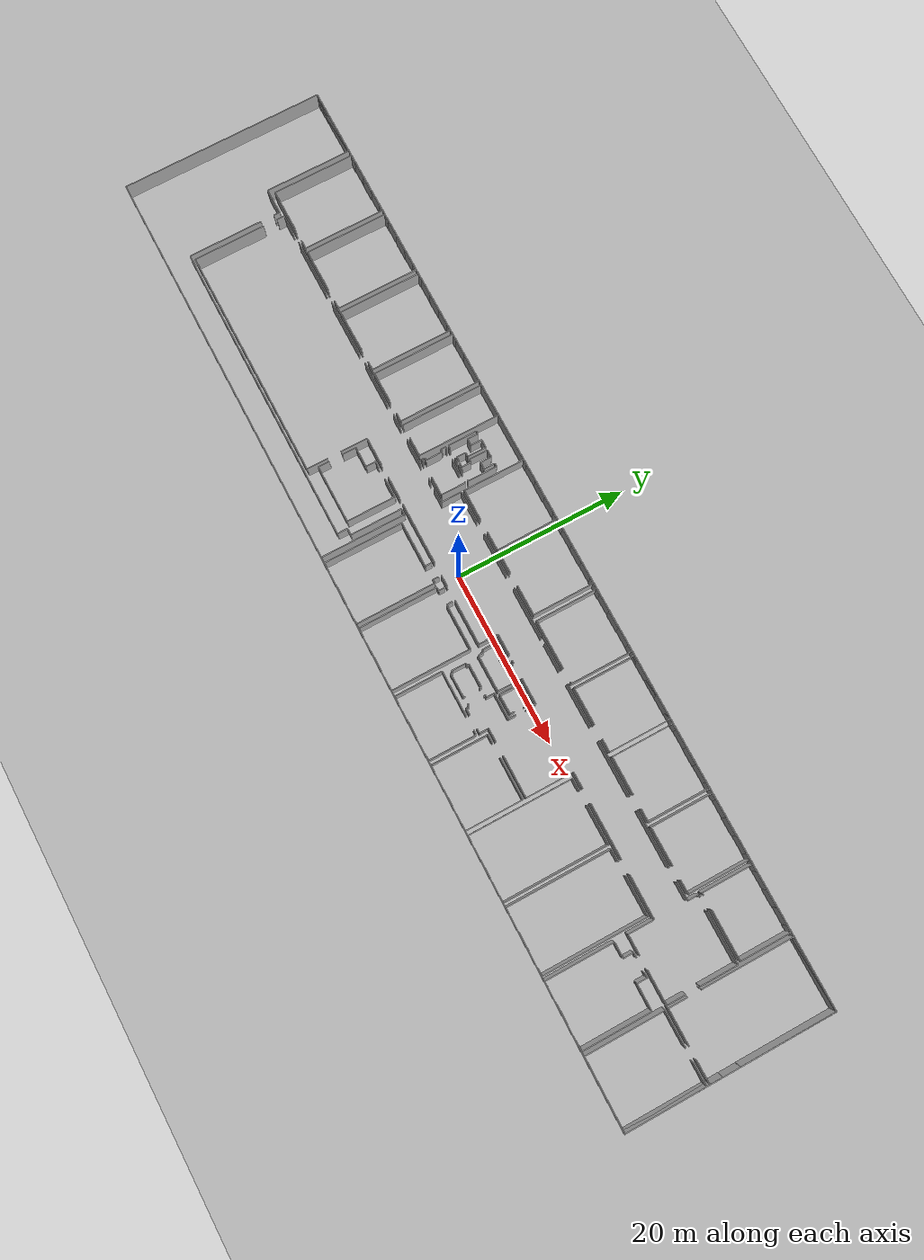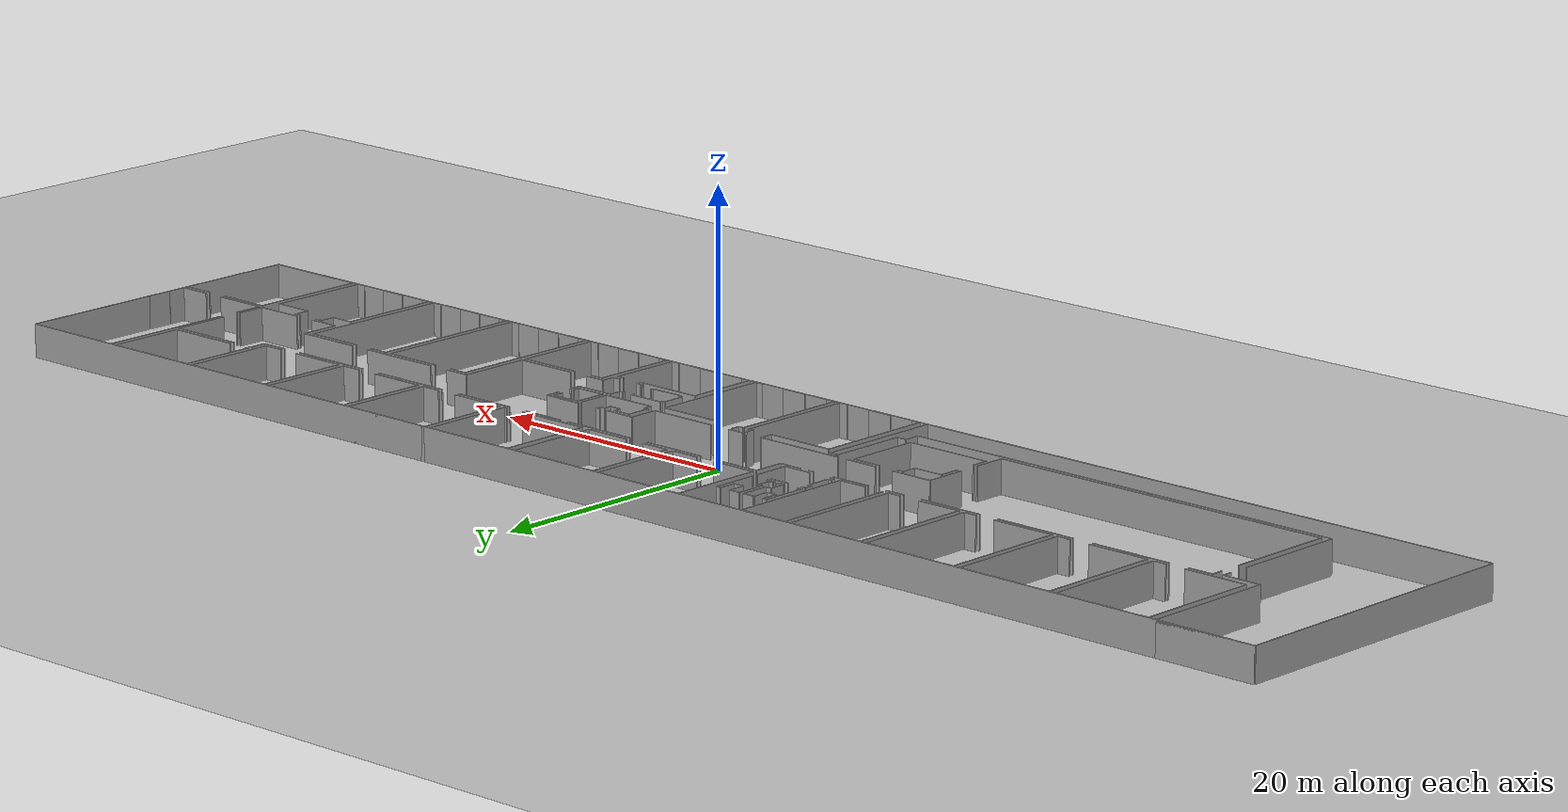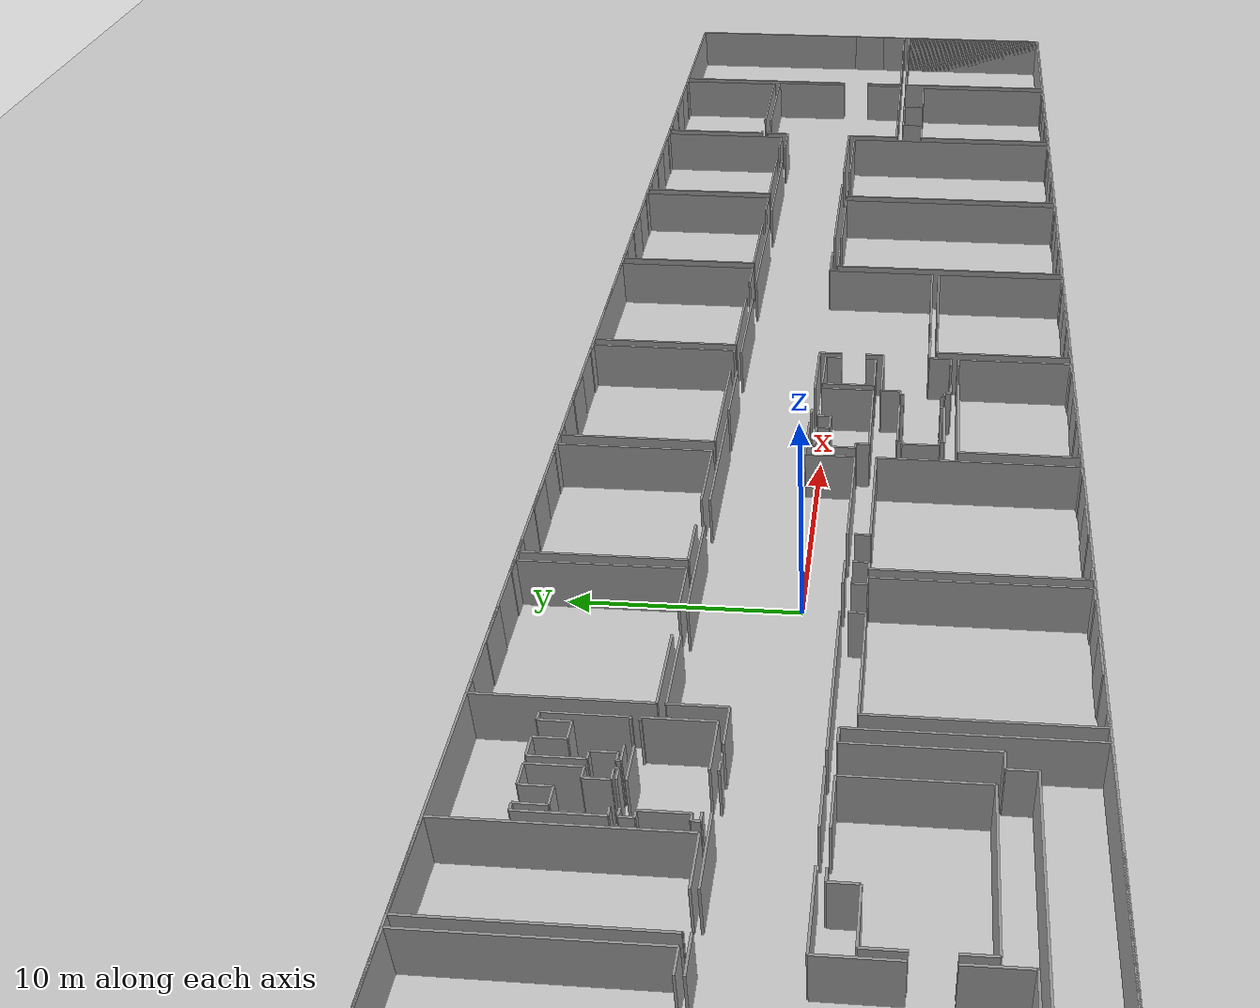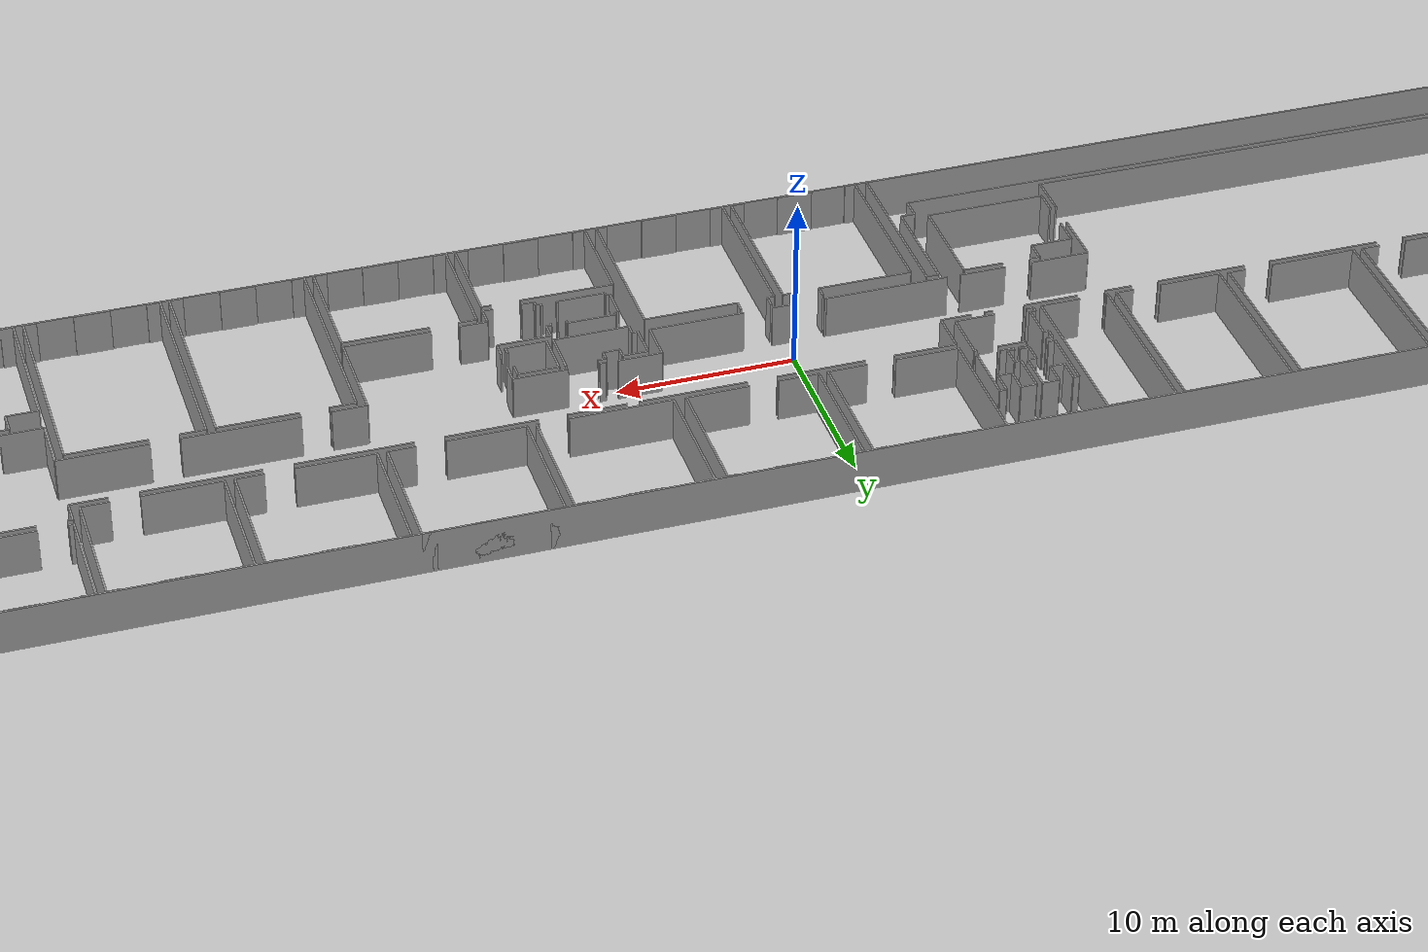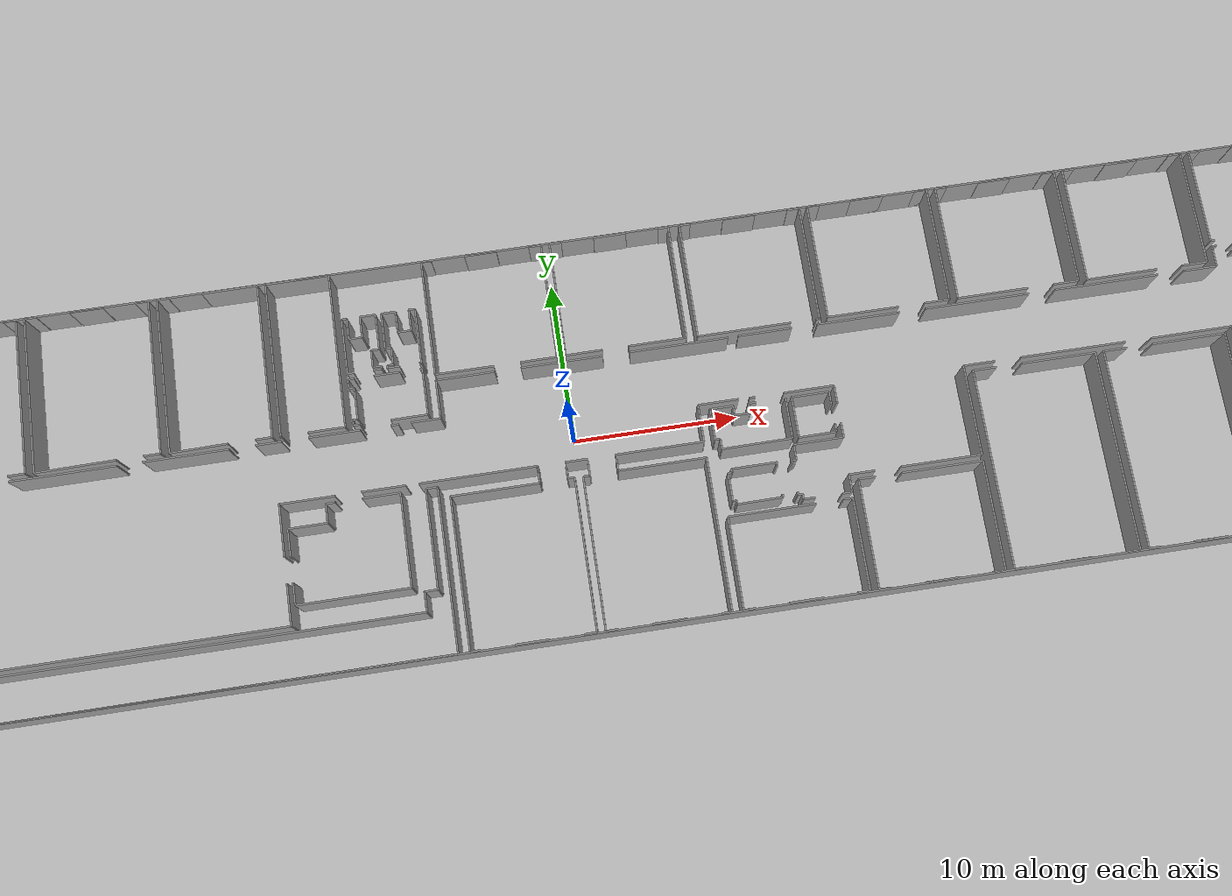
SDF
<sdf version="1.6">
  <world name="default">
    <light name="sun" type="directional">
      <cast_shadows>1</cast_shadows>
      <pose frame="">0 0 10 0 -0 0</pose>
      <diffuse>0.8 0.8 0.8 1</diffuse>
      <specular>0.1 0.1 0.1 1</specular>
      <attenuation>
        <range>1000</range>
        <constant>0.9</constant>
        <linear>0.01</linear>
        <quadratic>0.001</quadratic>
      </attenuation>
      <direction>-0.5 0.5 -1</direction>
    </light>
    <model name="ground_plane">
      <static>1</static>
      <link name="link">
        <collision name="collision">
          <geometry>
            <plane>
              <normal>0 0 1</normal>
              <size>100 100</size>
            </plane>
          </geometry>
          <surface>
            <friction>
              <ode>
                <mu>100</mu>
                <mu2>50</mu2>
              </ode>
              <torsional>
                <ode />
              </torsional>
            </friction>
            <contact>
              <ode />
            </contact>
            <bounce />
          </surface>
          <max_contacts>10</max_contacts>
        </collision>
        <visual name="visual">
          <cast_shadows>0</cast_shadows>
          <geometry>
            <plane>
              <normal>0 0 1</normal>
              <size>100 100</size>
            </plane>
          </geometry>
          <material>
            <script>
              <uri>file://media/materials/scripts/gazebo.material</uri>
              <name>Gazebo/Grey</name>
            </script>
          </material>
        </visual>
        <self_collide>0</self_collide>
        <kinematic>0</kinematic>
        <gravity>1</gravity>
      </link>
    </model>
    <gravity>0 0 -9.8</gravity>
    <magnetic_field>6e-06 2.3e-05 -4.2e-05</magnetic_field>
    <atmosphere type="adiabatic" />
    <physics default="0" name="default_physics" type="ode">
      <max_step_size>0.001</max_step_size>
      <real_time_factor>1</real_time_factor>
      <real_time_update_rate>1000</real_time_update_rate>
    </physics>
    <scene>
      <ambient>0.4 0.4 0.4 1</ambient>
      <background>0.7 0.7 0.7 1</background>
      <shadows>1</shadows>
    </scene>
    <spherical_coordinates>
      <surface_model>EARTH_WGS84</surface_model>
      <latitude_deg>0</latitude_deg>
      <longitude_deg>0</longitude_deg>
      <elevation>0</elevation>
      <heading_deg>0</heading_deg>
    </spherical_coordinates>
  <model name="0510034693_Layout1">
		<static>1</static>
		<link name="Wall_0">
			<collision name="Wall_0_Collision">
				<geometry>
					<box>
						<size>23.9682171457 0.1 2.5</size>
					</box>
				</geometry>
				<pose frame="">11.9841085728 0 1.25 0 0 0</pose>
			</collision>
			<visual name="Wall_0_Visual">
				<pose frame="">11.9841085728 0 1.25 0 0 0</pose>
				<geometry>
					<box>
						<size>23.9682171457 0.1 2.5</size>
					</box>
				</geometry>
				<material>
					<script>
						<uri>file://media/materials/scripts/gazebo.material</uri>
						<name>Gazebo/Grey</name>
					</script>
					<ambient>1 1 1 1</ambient>
				</material>
			</visual>
			<pose frame="">0.0 -23.9682171457 0 0 0 1.57079632679</pose>
		</link>
		<link name="Wall_1">
			<collision name="Wall_1_Collision">
				<geometry>
					<box>
						<size>7.87282294673 0.1 2.5</size>
					</box>
				</geometry>
				<pose frame="">3.93641147337 0 1.25 0 0 0</pose>
			</collision>
			<visual name="Wall_1_Visual">
				<pose frame="">3.93641147337 0 1.25 0 0 0</pose>
				<geometry>
					<box>
						<size>7.87282294673 0.1 2.5</size>
					</box>
				</geometry>
				<material>
					<script>
						<uri>file://media/materials/scripts/gazebo.material</uri>
						<name>Gazebo/Grey</name>
					</script>
					<ambient>1 1 1 1</ambient>
				</material>
			</visual>
			<pose frame="">0.0 -0.0 0 0 0 0.0</pose>
		</link>
		<link name="Wall_2">
			<collision name="Wall_2_Collision">
				<geometry>
					<box>
						<size>10.2181268246 0.1 2.5</size>
					</box>
				</geometry>
				<pose frame="">5.10906341232 0 1.25 0 0 0</pose>
			</collision>
			<visual name="Wall_2_Visual">
				<pose frame="">5.10906341232 0 1.25 0 0 0</pose>
				<geometry>
					<box>
						<size>10.2181268246 0.1 2.5</size>
					</box>
				</geometry>
				<material>
					<script>
						<uri>file://media/materials/scripts/gazebo.material</uri>
						<name>Gazebo/Grey</name>
					</script>
					<ambient>1 1 1 1</ambient>
				</material>
			</visual>
			<pose frame="">7.87282294673 -0.0 0 0 0 -1.57079632679</pose>
		</link>
		<link name="Wall_3">
			<collision name="Wall_3_Collision">
				<geometry>
					<box>
						<size>2.9954883863 0.1 2.5</size>
					</box>
				</geometry>
				<pose frame="">1.49774419315 0 1.25 0 0 0</pose>
			</collision>
			<visual name="Wall_3_Visual">
				<pose frame="">1.49774419315 0 1.25 0 0 0</pose>
				<geometry>
					<box>
						<size>2.9954883863 0.1 2.5</size>
					</box>
				</geometry>
				<material>
					<script>
						<uri>file://media/materials/scripts/gazebo.material</uri>
						<name>Gazebo/Grey</name>
					</script>
					<ambient>1 1 1 1</ambient>
				</material>
			</visual>
			<pose frame="">7.87282294673 -10.2181268246 0 0 0 0.0</pose>
		</link>
		<link name="Wall_4">
			<collision name="Wall_4_Collision">
				<geometry>
					<box>
						<size>0.747921349098 0.1 2.5</size>
					</box>
				</geometry>
				<pose frame="">0.373960674549 0 1.25 0 0 0</pose>
			</collision>
			<visual name="Wall_4_Visual">
				<pose frame="">0.373960674549 0 1.25 0 0 0</pose>
				<geometry>
					<box>
						<size>0.747921349098 0.1 2.5</size>
					</box>
				</geometry>
				<material>
					<script>
						<uri>file://media/materials/scripts/gazebo.material</uri>
						<name>Gazebo/Grey</name>
					</script>
					<ambient>1 1 1 1</ambient>
				</material>
			</visual>
			<pose frame="">10.868311333 -10.2181268246 0 0 0 -1.57079632679</pose>
		</link>
		<link name="Wall_5">
			<collision name="Wall_5_Collision">
				<geometry>
					<box>
						<size>8.76069432454 0.1 2.5</size>
					</box>
				</geometry>
				<pose frame="">4.38034716227 0 1.25 0 0 0</pose>
			</collision>
			<visual name="Wall_5_Visual">
				<pose frame="">4.38034716227 0 1.25 0 0 0</pose>
				<geometry>
					<box>
						<size>8.76069432454 0.1 2.5</size>
					</box>
				</geometry>
				<material>
					<script>
						<uri>file://media/materials/scripts/gazebo.material</uri>
						<name>Gazebo/Grey</name>
					</script>
					<ambient>1 1 1 1</ambient>
				</material>
			</visual>
			<pose frame="">10.868311333 -12.5241331401 0 0 0 -1.57079632679</pose>
		</link>
		<link name="Wall_6">
			<collision name="Wall_6_Collision">
				<geometry>
					<box>
						<size>35.6847219951 0.1 2.5</size>
					</box>
				</geometry>
				<pose frame="">17.8423609975 0 1.25 0 0 0</pose>
			</collision>
			<visual name="Wall_6_Visual">
				<pose frame="">17.8423609975 0 1.25 0 0 0</pose>
				<geometry>
					<box>
						<size>35.6847219951 0.1 2.5</size>
					</box>
				</geometry>
				<material>
					<script>
						<uri>file://media/materials/scripts/gazebo.material</uri>
						<name>Gazebo/Grey</name>
					</script>
					<ambient>1 1 1 1</ambient>
				</material>
			</visual>
			<pose frame="">10.868311333 -21.2848274647 0 0 0 0.0</pose>
		</link>
		<link name="Wall_7">
			<collision name="Wall_7_Collision">
				<geometry>
					<box>
						<size>1.19882918617 0.1 2.5</size>
					</box>
				</geometry>
				<pose frame="">0.599414593086 0 1.25 0 0 0</pose>
			</collision>
			<visual name="Wall_7_Visual">
				<pose frame="">0.599414593086 0 1.25 0 0 0</pose>
				<geometry>
					<box>
						<size>1.19882918617 0.1 2.5</size>
					</box>
				</geometry>
				<material>
					<script>
						<uri>file://media/materials/scripts/gazebo.material</uri>
						<name>Gazebo/Grey</name>
					</script>
					<ambient>1 1 1 1</ambient>
				</material>
			</visual>
			<pose frame="">46.5530333281 -21.2848274647 0 0 0 1.57079632679</pose>
		</link>
		<link name="Wall_8">
			<collision name="Wall_8_Collision">
				<geometry>
					<box>
						<size>0.790261303437 0.1 2.5</size>
					</box>
				</geometry>
				<pose frame="">0.395130651718 0 1.25 0 0 0</pose>
			</collision>
			<visual name="Wall_8_Visual">
				<pose frame="">0.395130651718 0 1.25 0 0 0</pose>
				<geometry>
					<box>
						<size>0.790261303437 0.1 2.5</size>
					</box>
				</geometry>
				<material>
					<script>
						<uri>file://media/materials/scripts/gazebo.material</uri>
						<name>Gazebo/Grey</name>
					</script>
					<ambient>1 1 1 1</ambient>
				</material>
			</visual>
			<pose frame="">46.5530333281 -20.0859982785 0 0 0 0.0</pose>
		</link>
		<link name="Wall_9">
			<collision name="Wall_9_Collision">
				<geometry>
					<box>
						<size>6.02964050336 0.1 2.5</size>
					</box>
				</geometry>
				<pose frame="">3.01482025168 0 1.25 0 0 0</pose>
			</collision>
			<visual name="Wall_9_Visual">
				<pose frame="">3.01482025168 0 1.25 0 0 0</pose>
				<geometry>
					<box>
						<size>6.02964050336 0.1 2.5</size>
					</box>
				</geometry>
				<material>
					<script>
						<uri>file://media/materials/scripts/gazebo.material</uri>
						<name>Gazebo/Grey</name>
					</script>
					<ambient>1 1 1 1</ambient>
				</material>
			</visual>
			<pose frame="">47.3432946316 -20.0859982785 0 0 0 1.57079632679</pose>
		</link>
		<link name="Wall_10">
			<collision name="Wall_10_Collision">
				<geometry>
					<box>
						<size>0.697848648608 0.1 2.5</size>
					</box>
				</geometry>
				<pose frame="">0.348924324304 0 1.25 0 0 0</pose>
			</collision>
			<visual name="Wall_10_Visual">
				<pose frame="">0.348924324304 0 1.25 0 0 0</pose>
				<geometry>
					<box>
						<size>0.697848648608 0.1 2.5</size>
					</box>
				</geometry>
				<material>
					<script>
						<uri>file://media/materials/scripts/gazebo.material</uri>
						<name>Gazebo/Grey</name>
					</script>
					<ambient>1 1 1 1</ambient>
				</material>
			</visual>
			<pose frame="">47.3432946316 -14.0563577751 0 0 0 0.0</pose>
		</link>
		<link name="Wall_11">
			<collision name="Wall_11_Collision">
				<geometry>
					<box>
						<size>9.88777376774 0.1 2.5</size>
					</box>
				</geometry>
				<pose frame="">4.94388688387 0 1.25 0 0 0</pose>
			</collision>
			<visual name="Wall_11_Visual">
				<pose frame="">4.94388688387 0 1.25 0 0 0</pose>
				<geometry>
					<box>
						<size>9.88777376774 0.1 2.5</size>
					</box>
				</geometry>
				<material>
					<script>
						<uri>file://media/materials/scripts/gazebo.material</uri>
						<name>Gazebo/Grey</name>
					</script>
					<ambient>1 1 1 1</ambient>
				</material>
			</visual>
			<pose frame="">48.0411432802 -14.0563577751 0 0 0 -1.57079632679</pose>
		</link>
		<link name="Wall_12">
			<collision name="Wall_12_Collision">
				<geometry>
					<box>
						<size>48.0411493179 0.1 2.5</size>
					</box>
				</geometry>
				<pose frame="">24.0205746589 0 1.25 0 0 0</pose>
			</collision>
			<visual name="Wall_12_Visual">
				<pose frame="">24.0205746589 0 1.25 0 0 0</pose>
				<geometry>
					<box>
						<size>48.0411493179 0.1 2.5</size>
					</box>
				</geometry>
				<material>
					<script>
						<uri>file://media/materials/scripts/gazebo.material</uri>
						<name>Gazebo/Grey</name>
					</script>
					<ambient>1 1 1 1</ambient>
				</material>
			</visual>
			<pose frame="">48.0411432802 -23.9441315429 0 0 0 -3.14109129998</pose>
		</link>
		<link name="Wall_13">
			<collision name="Wall_13_Collision">
				<geometry>
					<box>
						<size>8.40017088101 0.1 2.5</size>
					</box>
				</geometry>
				<pose frame="">4.20008544051 0 1.25 0 0 0</pose>
			</collision>
			<visual name="Wall_13_Visual">
				<pose frame="">4.20008544051 0 1.25 0 0 0</pose>
				<geometry>
					<box>
						<size>8.40017088101 0.1 2.5</size>
					</box>
				</geometry>
				<material>
					<script>
						<uri>file://media/materials/scripts/gazebo.material</uri>
						<name>Gazebo/Grey</name>
					</script>
					<ambient>1 1 1 1</ambient>
				</material>
			</visual>
			<pose frame="">11.4894663518 -20.9425583727 0 0 0 1.57079632679</pose>
		</link>
		<link name="Wall_14">
			<collision name="Wall_14_Collision">
				<geometry>
					<box>
						<size>0.926535108569 0.1 2.5</size>
					</box>
				</geometry>
				<pose frame="">0.463267554285 0 1.25 0 0 0</pose>
			</collision>
			<visual name="Wall_14_Visual">
				<pose frame="">0.463267554285 0 1.25 0 0 0</pose>
				<geometry>
					<box>
						<size>0.926535108569 0.1 2.5</size>
					</box>
				</geometry>
				<material>
					<script>
						<uri>file://media/materials/scripts/gazebo.material</uri>
						<name>Gazebo/Grey</name>
					</script>
					<ambient>1 1 1 1</ambient>
				</material>
			</visual>
			<pose frame="">11.4894663518 -10.8651421748 0 0 0 1.57079632679</pose>
		</link>
		<link name="Wall_15">
			<collision name="Wall_15_Collision">
				<geometry>
					<box>
						<size>1.95752567335 0.1 2.5</size>
					</box>
				</geometry>
				<pose frame="">0.978762836676 0 1.25 0 0 0</pose>
			</collision>
			<visual name="Wall_15_Visual">
				<pose frame="">0.978762836676 0 1.25 0 0 0</pose>
				<geometry>
					<box>
						<size>1.95752567335 0.1 2.5</size>
					</box>
				</geometry>
				<material>
					<script>
						<uri>file://media/materials/scripts/gazebo.material</uri>
						<name>Gazebo/Grey</name>
					</script>
					<ambient>1 1 1 1</ambient>
				</material>
			</visual>
			<pose frame="">11.4894663518 -9.93860706621 0 0 0 0.0</pose>
		</link>
		<link name="Wall_16">
			<collision name="Wall_16_Collision">
				<geometry>
					<box>
						<size>6.38534682634 0.1 2.5</size>
					</box>
				</geometry>
				<pose frame="">3.19267341317 0 1.25 0 0 0</pose>
			</collision>
			<visual name="Wall_16_Visual">
				<pose frame="">3.19267341317 0 1.25 0 0 0</pose>
				<geometry>
					<box>
						<size>6.38534682634 0.1 2.5</size>
					</box>
				</geometry>
				<material>
					<script>
						<uri>file://media/materials/scripts/gazebo.material</uri>
						<name>Gazebo/Grey</name>
					</script>
					<ambient>1 1 1 1</ambient>
				</material>
			</visual>
			<pose frame="">15.054389094 -9.93860706621 0 0 0 0.0</pose>
		</link>
		<link name="Wall_17">
			<collision name="Wall_17_Collision">
				<geometry>
					<box>
						<size>6.40753093415 0.1 2.5</size>
					</box>
				</geometry>
				<pose frame="">3.20376546708 0 1.25 0 0 0</pose>
			</collision>
			<visual name="Wall_17_Visual">
				<pose frame="">3.20376546708 0 1.25 0 0 0</pose>
				<geometry>
					<box>
						<size>6.40753093415 0.1 2.5</size>
					</box>
				</geometry>
				<material>
					<script>
						<uri>file://media/materials/scripts/gazebo.material</uri>
						<name>Gazebo/Grey</name>
					</script>
					<ambient>1 1 1 1</ambient>
				</material>
			</visual>
			<pose frame="">23.0582884264 -9.93860706621 0 0 0 0.0</pose>
		</link>
		<link name="Wall_18">
			<collision name="Wall_18_Collision">
				<geometry>
					<box>
						<size>5.09955593754 0.1 2.5</size>
					</box>
				</geometry>
				<pose frame="">2.54977796877 0 1.25 0 0 0</pose>
			</collision>
			<visual name="Wall_18_Visual">
				<pose frame="">2.54977796877 0 1.25 0 0 0</pose>
				<geometry>
					<box>
						<size>5.09955593754 0.1 2.5</size>
					</box>
				</geometry>
				<material>
					<script>
						<uri>file://media/materials/scripts/gazebo.material</uri>
						<name>Gazebo/Grey</name>
					</script>
					<ambient>1 1 1 1</ambient>
				</material>
			</visual>
			<pose frame="">30.9956354352 -9.93860706621 0 0 0 0.0</pose>
		</link>
		<link name="Wall_19">
			<collision name="Wall_19_Collision">
				<geometry>
					<box>
						<size>1.56036676035 0.1 2.5</size>
					</box>
				</geometry>
				<pose frame="">0.780183380173 0 1.25 0 0 0</pose>
			</collision>
			<visual name="Wall_19_Visual">
				<pose frame="">0.780183380173 0 1.25 0 0 0</pose>
				<geometry>
					<box>
						<size>1.56036676035 0.1 2.5</size>
					</box>
				</geometry>
				<material>
					<script>
						<uri>file://media/materials/scripts/gazebo.material</uri>
						<name>Gazebo/Grey</name>
					</script>
					<ambient>1 1 1 1</ambient>
				</material>
			</visual>
			<pose frame="">37.6693756631 -9.93860706621 0 0 0 0.0</pose>
		</link>
		<link name="Wall_20">
			<collision name="Wall_20_Collision">
				<geometry>
					<box>
						<size>3.10514126206 0.1 2.5</size>
					</box>
				</geometry>
				<pose frame="">1.55257063103 0 1.25 0 0 0</pose>
			</collision>
			<visual name="Wall_20_Visual">
				<pose frame="">1.55257063103 0 1.25 0 0 0</pose>
				<geometry>
					<box>
						<size>3.10514126206 0.1 2.5</size>
					</box>
				</geometry>
				<material>
					<script>
						<uri>file://media/materials/scripts/gazebo.material</uri>
						<name>Gazebo/Grey</name>
					</script>
					<ambient>1 1 1 1</ambient>
				</material>
			</visual>
			<pose frame="">40.8333365025 -9.93860706621 0 0 0 0.0</pose>
		</link>
		<link name="Wall_21">
			<collision name="Wall_21_Collision">
				<geometry>
					<box>
						<size>0.46003501286 0.1 2.5</size>
					</box>
				</geometry>
				<pose frame="">0.23001750643 0 1.25 0 0 0</pose>
			</collision>
			<visual name="Wall_21_Visual">
				<pose frame="">0.23001750643 0 1.25 0 0 0</pose>
				<geometry>
					<box>
						<size>0.46003501286 0.1 2.5</size>
					</box>
				</geometry>
				<material>
					<script>
						<uri>file://media/materials/scripts/gazebo.material</uri>
						<name>Gazebo/Grey</name>
					</script>
					<ambient>1 1 1 1</ambient>
				</material>
			</visual>
			<pose frame="">45.7426161782 -9.93860706621 0 0 0 0.0</pose>
		</link>
		<link name="Wall_22">
			<collision name="Wall_22_Collision">
				<geometry>
					<box>
						<size>2.6179782545 0.1 2.5</size>
					</box>
				</geometry>
				<pose frame="">1.30898912725 0 1.25 0 0 0</pose>
			</collision>
			<visual name="Wall_22_Visual">
				<pose frame="">1.30898912725 0 1.25 0 0 0</pose>
				<geometry>
					<box>
						<size>2.6179782545 0.1 2.5</size>
					</box>
				</geometry>
				<material>
					<script>
						<uri>file://media/materials/scripts/gazebo.material</uri>
						<name>Gazebo/Grey</name>
					</script>
					<ambient>1 1 1 1</ambient>
				</material>
			</visual>
			<pose frame="">46.202651191 -13.6842985956 0 0 0 3.14159265359</pose>
		</link>
		<link name="Wall_23">
			<collision name="Wall_23_Collision">
				<geometry>
					<box>
						<size>3.30061494347 0.1 2.5</size>
					</box>
				</geometry>
				<pose frame="">1.65030747173 0 1.25 0 0 0</pose>
			</collision>
			<visual name="Wall_23_Visual">
				<pose frame="">1.65030747173 0 1.25 0 0 0</pose>
				<geometry>
					<box>
						<size>3.30061494347 0.1 2.5</size>
					</box>
				</geometry>
				<material>
					<script>
						<uri>file://media/materials/scripts/gazebo.material</uri>
						<name>Gazebo/Grey</name>
					</script>
					<ambient>1 1 1 1</ambient>
				</material>
			</visual>
			<pose frame="">42.0175875607 -13.6842985956 0 0 0 3.14159265359</pose>
		</link>
		<link name="Wall_24">
			<collision name="Wall_24_Collision">
				<geometry>
					<box>
						<size>3.14215703052 0.1 2.5</size>
					</box>
				</geometry>
				<pose frame="">1.57107851526 0 1.25 0 0 0</pose>
			</collision>
			<visual name="Wall_24_Visual">
				<pose frame="">1.57107851526 0 1.25 0 0 0</pose>
				<geometry>
					<box>
						<size>3.14215703052 0.1 2.5</size>
					</box>
				</geometry>
				<material>
					<script>
						<uri>file://media/materials/scripts/gazebo.material</uri>
						<name>Gazebo/Grey</name>
					</script>
					<ambient>1 1 1 1</ambient>
				</material>
			</visual>
			<pose frame="">38.7169726172 -13.6842985956 0 0 0 -1.57079632679</pose>
		</link>
		<link name="Wall_25">
			<collision name="Wall_25_Collision">
				<geometry>
					<box>
						<size>2.47916912276 0.1 2.5</size>
					</box>
				</geometry>
				<pose frame="">1.23958456138 0 1.25 0 0 0</pose>
			</collision>
			<visual name="Wall_25_Visual">
				<pose frame="">1.23958456138 0 1.25 0 0 0</pose>
				<geometry>
					<box>
						<size>2.47916912276 0.1 2.5</size>
					</box>
				</geometry>
				<material>
					<script>
						<uri>file://media/materials/scripts/gazebo.material</uri>
						<name>Gazebo/Grey</name>
					</script>
					<ambient>1 1 1 1</ambient>
				</material>
			</visual>
			<pose frame="">38.7169726172 -18.4408248432 0 0 0 -1.57079632679</pose>
		</link>
		<link name="Wall_26">
			<collision name="Wall_26_Collision">
				<geometry>
					<box>
						<size>27.2275156154 0.1 2.5</size>
					</box>
				</geometry>
				<pose frame="">13.6137578077 0 1.25 0 0 0</pose>
			</collision>
			<visual name="Wall_26_Visual">
				<pose frame="">13.6137578077 0 1.25 0 0 0</pose>
				<geometry>
					<box>
						<size>27.2275156154 0.1 2.5</size>
					</box>
				</geometry>
				<material>
					<script>
						<uri>file://media/materials/scripts/gazebo.material</uri>
						<name>Gazebo/Grey</name>
					</script>
					<ambient>1 1 1 1</ambient>
				</material>
			</visual>
			<pose frame="">38.7169726172 -20.9199939659 0 0 0 -3.14076391807</pose>
		</link>
		<link name="Wall_27">
			<collision name="Wall_27_Collision">
				<geometry>
					<box>
						<size>9.55919543945 0.1 2.5</size>
					</box>
				</geometry>
				<pose frame="">4.77959771973 0 1.25 0 0 0</pose>
			</collision>
			<visual name="Wall_27_Visual">
				<pose frame="">4.77959771973 0 1.25 0 0 0</pose>
				<geometry>
					<box>
						<size>9.55919543945 0.1 2.5</size>
					</box>
				</geometry>
				<material>
					<script>
						<uri>file://media/materials/scripts/gazebo.material</uri>
						<name>Gazebo/Grey</name>
					</script>
					<ambient>1 1 1 1</ambient>
				</material>
			</visual>
			<pose frame="">8.49385119915 -9.60014096416 0 0 0 1.57079632679</pose>
		</link>
		<link name="Wall_28">
			<collision name="Wall_28_Collision">
				<geometry>
					<box>
						<size>0.832347725115 0.1 2.5</size>
					</box>
				</geometry>
				<pose frame="">0.416173862557 0 1.25 0 0 0</pose>
			</collision>
			<visual name="Wall_28_Visual">
				<pose frame="">0.416173862557 0 1.25 0 0 0</pose>
				<geometry>
					<box>
						<size>0.832347725115 0.1 2.5</size>
					</box>
				</geometry>
				<material>
					<script>
						<uri>file://media/materials/scripts/gazebo.material</uri>
						<name>Gazebo/Grey</name>
					</script>
					<ambient>1 1 1 1</ambient>
				</material>
			</visual>
			<pose frame="">8.49385119915 -0.0409455247049 0 0 0 0.0</pose>
		</link>
		<link name="Wall_29">
			<collision name="Wall_29_Collision">
				<geometry>
					<box>
						<size>1.98389307007 0.1 2.5</size>
					</box>
				</geometry>
				<pose frame="">0.991946535033 0 1.25 0 0 0</pose>
			</collision>
			<visual name="Wall_29_Visual">
				<pose frame="">0.991946535033 0 1.25 0 0 0</pose>
				<geometry>
					<box>
						<size>1.98389307007 0.1 2.5</size>
					</box>
				</geometry>
				<material>
					<script>
						<uri>file://media/materials/scripts/gazebo.material</uri>
						<name>Gazebo/Grey</name>
					</script>
					<ambient>1 1 1 1</ambient>
				</material>
			</visual>
			<pose frame="">11.3320225695 -0.0409455247049 0 0 0 0.0</pose>
		</link>
		<link name="Wall_30">
			<collision name="Wall_30_Collision">
				<geometry>
					<box>
						<size>0.745386022491 0.1 2.5</size>
					</box>
				</geometry>
				<pose frame="">0.372693011245 0 1.25 0 0 0</pose>
			</collision>
			<visual name="Wall_30_Visual">
				<pose frame="">0.372693011245 0 1.25 0 0 0</pose>
				<geometry>
					<box>
						<size>0.745386022491 0.1 2.5</size>
					</box>
				</geometry>
				<material>
					<script>
						<uri>file://media/materials/scripts/gazebo.material</uri>
						<name>Gazebo/Grey</name>
					</script>
					<ambient>1 1 1 1</ambient>
				</material>
			</visual>
			<pose frame="">15.3162883326 -0.0409455247049 0 0 0 0.0</pose>
		</link>
		<link name="Wall_31">
			<collision name="Wall_31_Collision">
				<geometry>
					<box>
						<size>9.55767424349 0.1 2.5</size>
					</box>
				</geometry>
				<pose frame="">4.77883712175 0 1.25 0 0 0</pose>
			</collision>
			<visual name="Wall_31_Visual">
				<pose frame="">4.77883712175 0 1.25 0 0 0</pose>
				<geometry>
					<box>
						<size>9.55767424349 0.1 2.5</size>
					</box>
				</geometry>
				<material>
					<script>
						<uri>file://media/materials/scripts/gazebo.material</uri>
						<name>Gazebo/Grey</name>
					</script>
					<ambient>1 1 1 1</ambient>
				</material>
			</visual>
			<pose frame="">16.061674355 -0.0409455247049 0 0 0 -1.57079632679</pose>
		</link>
		<link name="Wall_32">
			<collision name="Wall_32_Collision">
				<geometry>
					<box>
						<size>1.02870877084 0.1 2.5</size>
					</box>
				</geometry>
				<pose frame="">0.514354385418 0 1.25 0 0 0</pose>
			</collision>
			<visual name="Wall_32_Visual">
				<pose frame="">0.514354385418 0 1.25 0 0 0</pose>
				<geometry>
					<box>
						<size>1.02870877084 0.1 2.5</size>
					</box>
				</geometry>
				<material>
					<script>
						<uri>file://media/materials/scripts/gazebo.material</uri>
						<name>Gazebo/Grey</name>
					</script>
					<ambient>1 1 1 1</ambient>
				</material>
			</visual>
			<pose frame="">16.061674355 -9.5986197682 0 0 0 3.14159265359</pose>
		</link>
		<link name="Wall_33">
			<collision name="Wall_33_Collision">
				<geometry>
					<box>
						<size>4.97481810105 0.1 2.5</size>
					</box>
				</geometry>
				<pose frame="">2.48740905052 0 1.25 0 0 0</pose>
			</collision>
			<visual name="Wall_33_Visual">
				<pose frame="">2.48740905052 0 1.25 0 0 0</pose>
				<geometry>
					<box>
						<size>4.97481810105 0.1 2.5</size>
					</box>
				</geometry>
				<material>
					<script>
						<uri>file://media/materials/scripts/gazebo.material</uri>
						<name>Gazebo/Grey</name>
					</script>
					<ambient>1 1 1 1</ambient>
				</material>
			</visual>
			<pose frame="">13.4686690676 -9.5986197682 0 0 0 -3.14128687437</pose>
		</link>
		<link name="Wall_34">
			<collision name="Wall_34_Collision">
				<geometry>
					<box>
						<size>9.60863430829 0.1 2.5</size>
					</box>
				</geometry>
				<pose frame="">4.80431715415 0 1.25 0 0 0</pose>
			</collision>
			<visual name="Wall_34_Visual">
				<pose frame="">4.80431715415 0 1.25 0 0 0</pose>
				<geometry>
					<box>
						<size>9.60863430829 0.1 2.5</size>
					</box>
				</geometry>
				<material>
					<script>
						<uri>file://media/materials/scripts/gazebo.material</uri>
						<name>Gazebo/Grey</name>
					</script>
					<ambient>1 1 1 1</ambient>
				</material>
			</visual>
			<pose frame="">16.5913040833 -9.64210061951 0 0 0 1.57079632679</pose>
		</link>
		<link name="Wall_35">
			<collision name="Wall_35_Collision">
				<geometry>
					<box>
						<size>0.721173653393 0.1 2.5</size>
					</box>
				</geometry>
				<pose frame="">0.360586826696 0 1.25 0 0 0</pose>
			</collision>
			<visual name="Wall_35_Visual">
				<pose frame="">0.360586826696 0 1.25 0 0 0</pose>
				<geometry>
					<box>
						<size>0.721173653393 0.1 2.5</size>
					</box>
				</geometry>
				<material>
					<script>
						<uri>file://media/materials/scripts/gazebo.material</uri>
						<name>Gazebo/Grey</name>
					</script>
					<ambient>1 1 1 1</ambient>
				</material>
			</visual>
			<pose frame="">16.5913040833 -0.0334663112139 0 0 0 0.0</pose>
		</link>
		<link name="Wall_36">
			<collision name="Wall_36_Collision">
				<geometry>
					<box>
						<size>1.97451236162 0.1 2.5</size>
					</box>
				</geometry>
				<pose frame="">0.987256180809 0 1.25 0 0 0</pose>
			</collision>
			<visual name="Wall_36_Visual">
				<pose frame="">0.987256180809 0 1.25 0 0 0</pose>
				<geometry>
					<box>
						<size>1.97451236162 0.1 2.5</size>
					</box>
				</geometry>
				<material>
					<script>
						<uri>file://media/materials/scripts/gazebo.material</uri>
						<name>Gazebo/Grey</name>
					</script>
					<ambient>1 1 1 1</ambient>
				</material>
			</visual>
			<pose frame="">19.3445420123 -0.0334663112139 0 0 0 0.0</pose>
		</link>
		<link name="Wall_37">
			<collision name="Wall_37_Collision">
				<geometry>
					<box>
						<size>0.747667816437 0.1 2.5</size>
					</box>
				</geometry>
				<pose frame="">0.373833908219 0 1.25 0 0 0</pose>
			</collision>
			<visual name="Wall_37_Visual">
				<pose frame="">0.373833908219 0 1.25 0 0 0</pose>
				<geometry>
					<box>
						<size>0.747667816437 0.1 2.5</size>
					</box>
				</geometry>
				<material>
					<script>
						<uri>file://media/materials/scripts/gazebo.material</uri>
						<name>Gazebo/Grey</name>
					</script>
					<ambient>1 1 1 1</ambient>
				</material>
			</visual>
			<pose frame="">23.3319769336 -0.0334663112139 0 0 0 0.0</pose>
		</link>
		<link name="Wall_38">
			<collision name="Wall_38_Collision">
				<geometry>
					<box>
						<size>9.56616758762 0.1 2.5</size>
					</box>
				</geometry>
				<pose frame="">4.78308379381 0 1.25 0 0 0</pose>
			</collision>
			<visual name="Wall_38_Visual">
				<pose frame="">4.78308379381 0 1.25 0 0 0</pose>
				<geometry>
					<box>
						<size>9.56616758762 0.1 2.5</size>
					</box>
				</geometry>
				<material>
					<script>
						<uri>file://media/materials/scripts/gazebo.material</uri>
						<name>Gazebo/Grey</name>
					</script>
					<ambient>1 1 1 1</ambient>
				</material>
			</visual>
			<pose frame="">24.07964475 -0.0334663112139 0 0 0 -1.57079632679</pose>
		</link>
		<link name="Wall_39">
			<collision name="Wall_39_Collision">
				<geometry>
					<box>
						<size>1.04480809479 0.1 2.5</size>
					</box>
				</geometry>
				<pose frame="">0.522404047395 0 1.25 0 0 0</pose>
			</collision>
			<visual name="Wall_39_Visual">
				<pose frame="">0.522404047395 0 1.25 0 0 0</pose>
				<geometry>
					<box>
						<size>1.04480809479 0.1 2.5</size>
					</box>
				</geometry>
				<material>
					<script>
						<uri>file://media/materials/scripts/gazebo.material</uri>
						<name>Gazebo/Grey</name>
					</script>
					<ambient>1 1 1 1</ambient>
				</material>
			</visual>
			<pose frame="">24.07964475 -9.59963389884 0 0 0 3.14159265359</pose>
		</link>
		<link name="Wall_40">
			<collision name="Wall_40_Collision">
				<geometry>
					<box>
						<size>4.84722343738 0.1 2.5</size>
					</box>
				</geometry>
				<pose frame="">2.42361171869 0 1.25 0 0 0</pose>
			</collision>
			<visual name="Wall_40_Visual">
				<pose frame="">2.42361171869 0 1.25 0 0 0</pose>
				<geometry>
					<box>
						<size>4.84722343738 0.1 2.5</size>
					</box>
				</geometry>
				<material>
					<script>
						<uri>file://media/materials/scripts/gazebo.material</uri>
						<name>Gazebo/Grey</name>
					</script>
					<ambient>1 1 1 1</ambient>
				</material>
			</visual>
			<pose frame="">21.4383414907 -9.59963389884 0 0 0 -3.13283150105</pose>
		</link>
		<link name="Wall_41">
			<collision name="Wall_41_Collision">
				<geometry>
					<box>
						<size>9.6240998006 0.1 2.5</size>
					</box>
				</geometry>
				<pose frame="">4.8120499003 0 1.25 0 0 0</pose>
			</collision>
			<visual name="Wall_41_Visual">
				<pose frame="">4.8120499003 0 1.25 0 0 0</pose>
				<geometry>
					<box>
						<size>9.6240998006 0.1 2.5</size>
					</box>
				</geometry>
				<material>
					<script>
						<uri>file://media/materials/scripts/gazebo.material</uri>
						<name>Gazebo/Grey</name>
					</script>
					<ambient>1 1 1 1</ambient>
				</material>
			</visual>
			<pose frame="">24.5949498829 -9.64717127272 0 0 0 1.57079632679</pose>
		</link>
		<link name="Wall_42">
			<collision name="Wall_42_Collision">
				<geometry>
					<box>
						<size>0.735878547714 0.1 2.5</size>
					</box>
				</geometry>
				<pose frame="">0.367939273857 0 1.25 0 0 0</pose>
			</collision>
			<visual name="Wall_42_Visual">
				<pose frame="">0.367939273857 0 1.25 0 0 0</pose>
				<geometry>
					<box>
						<size>0.735878547714 0.1 2.5</size>
					</box>
				</geometry>
				<material>
					<script>
						<uri>file://media/materials/scripts/gazebo.material</uri>
						<name>Gazebo/Grey</name>
					</script>
					<ambient>1 1 1 1</ambient>
				</material>
			</visual>
			<pose frame="">24.5949498829 -0.0230714721247 0 0 0 0.0</pose>
		</link>
		<link name="Wall_43">
			<collision name="Wall_43_Collision">
				<geometry>
					<box>
						<size>2.02547242642 0.1 2.5</size>
					</box>
				</geometry>
				<pose frame="">1.01273621321 0 1.25 0 0 0</pose>
			</collision>
			<visual name="Wall_43_Visual">
				<pose frame="">1.01273621321 0 1.25 0 0 0</pose>
				<geometry>
					<box>
						<size>2.02547242642 0.1 2.5</size>
					</box>
				</geometry>
				<material>
					<script>
						<uri>file://media/materials/scripts/gazebo.material</uri>
						<name>Gazebo/Grey</name>
					</script>
					<ambient>1 1 1 1</ambient>
				</material>
			</visual>
			<pose frame="">27.3228345459 -0.0230714721247 0 0 0 0.0</pose>
		</link>
		<link name="Wall_44">
			<collision name="Wall_44_Collision">
				<geometry>
					<box>
						<size>0.758442954518 0.1 2.5</size>
					</box>
				</geometry>
				<pose frame="">0.379221477259 0 1.25 0 0 0</pose>
			</collision>
			<visual name="Wall_44_Visual">
				<pose frame="">0.379221477259 0 1.25 0 0 0</pose>
				<geometry>
					<box>
						<size>0.758442954518 0.1 2.5</size>
					</box>
				</geometry>
				<material>
					<script>
						<uri>file://media/materials/scripts/gazebo.material</uri>
						<name>Gazebo/Grey</name>
					</script>
					<ambient>1 1 1 1</ambient>
				</material>
			</visual>
			<pose frame="">31.3237066982 -0.0230714721247 0 0 0 0.0</pose>
		</link>
		<link name="Wall_45">
			<collision name="Wall_45_Collision">
				<geometry>
					<box>
						<size>9.5685761479 0.1 2.5</size>
					</box>
				</geometry>
				<pose frame="">4.78428807395 0 1.25 0 0 0</pose>
			</collision>
			<visual name="Wall_45_Visual">
				<pose frame="">4.78428807395 0 1.25 0 0 0</pose>
				<geometry>
					<box>
						<size>9.5685761479 0.1 2.5</size>
					</box>
				</geometry>
				<material>
					<script>
						<uri>file://media/materials/scripts/gazebo.material</uri>
						<name>Gazebo/Grey</name>
					</script>
					<ambient>1 1 1 1</ambient>
				</material>
			</visual>
			<pose frame="">32.0821496527 -0.0230714721247 0 0 0 -1.57079632679</pose>
		</link>
		<link name="Wall_46">
			<collision name="Wall_46_Collision">
				<geometry>
					<box>
						<size>1.01679273578 0.1 2.5</size>
					</box>
				</geometry>
				<pose frame="">0.508396367891 0 1.25 0 0 0</pose>
			</collision>
			<visual name="Wall_46_Visual">
				<pose frame="">0.508396367891 0 1.25 0 0 0</pose>
				<geometry>
					<box>
						<size>1.01679273578 0.1 2.5</size>
					</box>
				</geometry>
				<material>
					<script>
						<uri>file://media/materials/scripts/gazebo.material</uri>
						<name>Gazebo/Grey</name>
					</script>
					<ambient>1 1 1 1</ambient>
				</material>
			</visual>
			<pose frame="">32.0821496527 -9.59164762003 0 0 0 3.14159265359</pose>
		</link>
		<link name="Wall_47">
			<collision name="Wall_47_Collision">
				<geometry>
					<box>
						<size>4.87765059126 0.1 2.5</size>
					</box>
				</geometry>
				<pose frame="">2.43882529563 0 1.25 0 0 0</pose>
			</collision>
			<visual name="Wall_47_Visual">
				<pose frame="">2.43882529563 0 1.25 0 0 0</pose>
				<geometry>
					<box>
						<size>4.87765059126 0.1 2.5</size>
					</box>
				</geometry>
				<material>
					<script>
						<uri>file://media/materials/scripts/gazebo.material</uri>
						<name>Gazebo/Grey</name>
					</script>
					<ambient>1 1 1 1</ambient>
				</material>
			</visual>
			<pose frame="">29.4722844434 -9.59164762003 0 0 0 -3.13020912973</pose>
		</link>
		<link name="Wall_48">
			<collision name="Wall_48_Collision">
				<geometry>
					<box>
						<size>9.62524069757 0.1 2.5</size>
					</box>
				</geometry>
				<pose frame="">4.81262034878 0 1.25 0 0 0</pose>
			</collision>
			<visual name="Wall_48_Visual">
				<pose frame="">4.81262034878 0 1.25 0 0 0</pose>
				<geometry>
					<box>
						<size>9.62524069757 0.1 2.5</size>
					</box>
				</geometry>
				<material>
					<script>
						<uri>file://media/materials/scripts/gazebo.material</uri>
						<name>Gazebo/Grey</name>
					</script>
					<ambient>1 1 1 1</ambient>
				</material>
			</visual>
			<pose frame="">32.6018916072 -9.64210061951 0 0 0 1.57079632679</pose>
		</link>
		<link name="Wall_49">
			<collision name="Wall_49_Collision">
				<geometry>
					<box>
						<size>0.732075557804 0.1 2.5</size>
					</box>
				</geometry>
				<pose frame="">0.366037778902 0 1.25 0 0 0</pose>
			</collision>
			<visual name="Wall_49_Visual">
				<pose frame="">0.366037778902 0 1.25 0 0 0</pose>
				<geometry>
					<box>
						<size>0.732075557804 0.1 2.5</size>
					</box>
				</geometry>
				<material>
					<script>
						<uri>file://media/materials/scripts/gazebo.material</uri>
						<name>Gazebo/Grey</name>
					</script>
					<ambient>1 1 1 1</ambient>
				</material>
			</visual>
			<pose frame="">32.6018916072 -0.0168599219373 0 0 0 0.0</pose>
		</link>
		<link name="Wall_50">
			<collision name="Wall_50_Collision">
				<geometry>
					<box>
						<size>3.37033642516 0.1 2.5</size>
					</box>
				</geometry>
				<pose frame="">1.68516821258 0 1.25 0 0 0</pose>
			</collision>
			<visual name="Wall_50_Visual">
				<pose frame="">1.68516821258 0 1.25 0 0 0</pose>
				<geometry>
					<box>
						<size>3.37033642516 0.1 2.5</size>
					</box>
				</geometry>
				<material>
					<script>
						<uri>file://media/materials/scripts/gazebo.material</uri>
						<name>Gazebo/Grey</name>
					</script>
					<ambient>1 1 1 1</ambient>
				</material>
			</visual>
			<pose frame="">35.3415655388 -0.0168599219373 0 0 0 0.0</pose>
		</link>
		<link name="Wall_51">
			<collision name="Wall_51_Collision">
				<geometry>
					<box>
						<size>9.57326650212 0.1 2.5</size>
					</box>
				</geometry>
				<pose frame="">4.78663325106 0 1.25 0 0 0</pose>
			</collision>
			<visual name="Wall_51_Visual">
				<pose frame="">4.78663325106 0 1.25 0 0 0</pose>
				<geometry>
					<box>
						<size>9.57326650212 0.1 2.5</size>
					</box>
				</geometry>
				<material>
					<script>
						<uri>file://media/materials/scripts/gazebo.material</uri>
						<name>Gazebo/Grey</name>
					</script>
					<ambient>1 1 1 1</ambient>
				</material>
			</visual>
			<pose frame="">38.711901964 -0.0168599219373 0 0 0 -1.57079632679</pose>
		</link>
		<link name="Wall_52">
			<collision name="Wall_52_Collision">
				<geometry>
					<box>
						<size>1.01337004486 0.1 2.5</size>
					</box>
				</geometry>
				<pose frame="">0.506685022431 0 1.25 0 0 0</pose>
			</collision>
			<visual name="Wall_52_Visual">
				<pose frame="">0.506685022431 0 1.25 0 0 0</pose>
				<geometry>
					<box>
						<size>1.01337004486 0.1 2.5</size>
					</box>
				</geometry>
				<material>
					<script>
						<uri>file://media/materials/scripts/gazebo.material</uri>
						<name>Gazebo/Grey</name>
					</script>
					<ambient>1 1 1 1</ambient>
				</material>
			</visual>
			<pose frame="">38.711901964 -9.59012642406 0 0 0 3.14159265359</pose>
		</link>
		<link name="Wall_53">
			<collision name="Wall_53_Collision">
				<geometry>
					<box>
						<size>3.47936338321 0.1 2.5</size>
					</box>
				</geometry>
				<pose frame="">1.7396816916 0 1.25 0 0 0</pose>
			</collision>
			<visual name="Wall_53_Visual">
				<pose frame="">1.7396816916 0 1.25 0 0 0</pose>
				<geometry>
					<box>
						<size>3.47936338321 0.1 2.5</size>
					</box>
				</geometry>
				<material>
					<script>
						<uri>file://media/materials/scripts/gazebo.material</uri>
						<name>Gazebo/Grey</name>
					</script>
					<ambient>1 1 1 1</ambient>
				</material>
			</visual>
			<pose frame="">36.0808667775 -9.59012642406 0 0 0 -3.1266542517</pose>
		</link>
		<link name="Wall_54">
			<collision name="Wall_54_Collision">
				<geometry>
					<box>
						<size>1.31532744377 0.1 2.5</size>
					</box>
				</geometry>
				<pose frame="">0.657663721885 0 1.25 0 0 0</pose>
			</collision>
			<visual name="Wall_54_Visual">
				<pose frame="">0.657663721885 0 1.25 0 0 0</pose>
				<geometry>
					<box>
						<size>1.31532744377 0.1 2.5</size>
					</box>
				</geometry>
				<material>
					<script>
						<uri>file://media/materials/scripts/gazebo.material</uri>
						<name>Gazebo/Grey</name>
					</script>
					<ambient>1 1 1 1</ambient>
				</material>
			</visual>
			<pose frame="">39.0715380432 -19.7570396512 0 0 0 1.57079632679</pose>
		</link>
		<link name="Wall_55">
			<collision name="Wall_55_Collision">
				<geometry>
					<box>
						<size>1.63363769929 0.1 2.5</size>
					</box>
				</geometry>
				<pose frame="">0.816818849646 0 1.25 0 0 0</pose>
			</collision>
			<visual name="Wall_55_Visual">
				<pose frame="">0.816818849646 0 1.25 0 0 0</pose>
				<geometry>
					<box>
						<size>1.63363769929 0.1 2.5</size>
					</box>
				</geometry>
				<material>
					<script>
						<uri>file://media/materials/scripts/gazebo.material</uri>
						<name>Gazebo/Grey</name>
					</script>
					<ambient>1 1 1 1</ambient>
				</material>
			</visual>
			<pose frame="">39.0715380432 -16.8599219373 0 0 0 1.57079632679</pose>
		</link>
		<link name="Wall_56">
			<collision name="Wall_56_Collision">
				<geometry>
					<box>
						<size>2.35430428736 0.1 2.5</size>
					</box>
				</geometry>
				<pose frame="">1.17715214368 0 1.25 0 0 0</pose>
			</collision>
			<visual name="Wall_56_Visual">
				<pose frame="">1.17715214368 0 1.25 0 0 0</pose>
				<geometry>
					<box>
						<size>2.35430428736 0.1 2.5</size>
					</box>
				</geometry>
				<material>
					<script>
						<uri>file://media/materials/scripts/gazebo.material</uri>
						<name>Gazebo/Grey</name>
					</script>
					<ambient>1 1 1 1</ambient>
				</material>
			</visual>
			<pose frame="">39.0715380432 -15.226284238 0 0 0 0.0</pose>
		</link>
		<link name="Wall_57">
			<collision name="Wall_57_Collision">
				<geometry>
					<box>
						<size>1.15851749312 0.1 2.5</size>
					</box>
				</geometry>
				<pose frame="">0.57925874656 0 1.25 0 0 0</pose>
			</collision>
			<visual name="Wall_57_Visual">
				<pose frame="">0.57925874656 0 1.25 0 0 0</pose>
				<geometry>
					<box>
						<size>1.15851749312 0.1 2.5</size>
					</box>
				</geometry>
				<material>
					<script>
						<uri>file://media/materials/scripts/gazebo.material</uri>
						<name>Gazebo/Grey</name>
					</script>
					<ambient>1 1 1 1</ambient>
				</material>
			</visual>
			<pose frame="">41.4258423306 -15.226284238 0 0 0 1.57079632679</pose>
		</link>
		<link name="Wall_58">
			<collision name="Wall_58_Collision">
				<geometry>
					<box>
						<size>0.56677226302 0.1 2.5</size>
					</box>
				</geometry>
				<pose frame="">0.28338613151 0 1.25 0 0 0</pose>
			</collision>
			<visual name="Wall_58_Visual">
				<pose frame="">0.28338613151 0 1.25 0 0 0</pose>
				<geometry>
					<box>
						<size>0.56677226302 0.1 2.5</size>
					</box>
				</geometry>
				<material>
					<script>
						<uri>file://media/materials/scripts/gazebo.material</uri>
						<name>Gazebo/Grey</name>
					</script>
					<ambient>1 1 1 1</ambient>
				</material>
			</visual>
			<pose frame="">41.4258423306 -14.0677667449 0 0 0 0.0</pose>
		</link>
		<link name="Wall_59">
			<collision name="Wall_59_Collision">
				<geometry>
					<box>
						<size>2.2717794063 0.1 2.5</size>
					</box>
				</geometry>
				<pose frame="">1.13588970315 0 1.25 0 0 0</pose>
			</collision>
			<visual name="Wall_59_Visual">
				<pose frame="">1.13588970315 0 1.25 0 0 0</pose>
				<geometry>
					<box>
						<size>2.2717794063 0.1 2.5</size>
					</box>
				</geometry>
				<material>
					<script>
						<uri>file://media/materials/scripts/gazebo.material</uri>
						<name>Gazebo/Grey</name>
					</script>
					<ambient>1 1 1 1</ambient>
				</material>
			</visual>
			<pose frame="">43.5763063587 -14.0677667449 0 0 0 0.0</pose>
		</link>
		<link name="Wall_60">
			<collision name="Wall_60_Collision">
				<geometry>
					<box>
						<size>5.68280782351 0.1 2.5</size>
					</box>
				</geometry>
				<pose frame="">2.84140391176 0 1.25 0 0 0</pose>
			</collision>
			<visual name="Wall_60_Visual">
				<pose frame="">2.84140391176 0 1.25 0 0 0</pose>
				<geometry>
					<box>
						<size>5.68280782351 0.1 2.5</size>
					</box>
				</geometry>
				<material>
					<script>
						<uri>file://media/materials/scripts/gazebo.material</uri>
						<name>Gazebo/Grey</name>
					</script>
					<ambient>1 1 1 1</ambient>
				</material>
			</visual>
			<pose frame="">45.848085765 -14.0677667449 0 0 0 -1.57079632679</pose>
		</link>
		<link name="Wall_61">
			<collision name="Wall_61_Collision">
				<geometry>
					<box>
						<size>6.77655080578 0.1 2.5</size>
					</box>
				</geometry>
				<pose frame="">3.38827540289 0 1.25 0 0 0</pose>
			</collision>
			<visual name="Wall_61_Visual">
				<pose frame="">3.38827540289 0 1.25 0 0 0</pose>
				<geometry>
					<box>
						<size>6.77655080578 0.1 2.5</size>
					</box>
				</geometry>
				<material>
					<script>
						<uri>file://media/materials/scripts/gazebo.material</uri>
						<name>Gazebo/Grey</name>
					</script>
					<ambient>1 1 1 1</ambient>
				</material>
			</visual>
			<pose frame="">45.848085765 -19.7505745684 0 0 0 -3.14063861605</pose>
		</link>
		<link name="Wall_62">
			<collision name="Wall_62_Collision">
				<geometry>
					<box>
						<size>0.341762026639 0.1 2.5</size>
					</box>
				</geometry>
				<pose frame="">0.170881013319 0 1.25 0 0 0</pose>
			</collision>
			<visual name="Wall_62_Visual">
				<pose frame="">0.170881013319 0 1.25 0 0 0</pose>
				<geometry>
					<box>
						<size>0.341762026639 0.1 2.5</size>
					</box>
				</geometry>
				<material>
					<script>
						<uri>file://media/materials/scripts/gazebo.material</uri>
						<name>Gazebo/Grey</name>
					</script>
					<ambient>1 1 1 1</ambient>
				</material>
			</visual>
			<pose frame="">43.5429668138 -9.60014096416 0 0 0 1.57079632679</pose>
		</link>
		<link name="Wall_63">
			<collision name="Wall_63_Collision">
				<geometry>
					<box>
						<size>0.300055903952 0.1 2.5</size>
					</box>
				</geometry>
				<pose frame="">0.150027951976 0 1.25 0 0 0</pose>
			</collision>
			<visual name="Wall_63_Visual">
				<pose frame="">0.150027951976 0 1.25 0 0 0</pose>
				<geometry>
					<box>
						<size>0.300055903952 0.1 2.5</size>
					</box>
				</geometry>
				<material>
					<script>
						<uri>file://media/materials/scripts/gazebo.material</uri>
						<name>Gazebo/Grey</name>
					</script>
					<ambient>1 1 1 1</ambient>
				</material>
			</visual>
			<pose frame="">43.5429668138 -9.25837893752 0 0 0 0.0</pose>
		</link>
		<link name="Wall_64">
			<collision name="Wall_64_Collision">
				<geometry>
					<box>
						<size>1.95042675885 0.1 2.5</size>
					</box>
				</geometry>
				<pose frame="">0.975213379426 0 1.25 0 0 0</pose>
			</collision>
			<visual name="Wall_64_Visual">
				<pose frame="">0.975213379426 0 1.25 0 0 0</pose>
				<geometry>
					<box>
						<size>1.95042675885 0.1 2.5</size>
					</box>
				</geometry>
				<material>
					<script>
						<uri>file://media/materials/scripts/gazebo.material</uri>
						<name>Gazebo/Grey</name>
					</script>
					<ambient>1 1 1 1</ambient>
				</material>
			</visual>
			<pose frame="">43.8430227178 -9.25837893752 0 0 0 1.57079632679</pose>
		</link>
		<link name="Wall_65">
			<collision name="Wall_65_Collision">
				<geometry>
					<box>
						<size>0.308422481755 0.1 2.5</size>
					</box>
				</geometry>
				<pose frame="">0.154211240878 0 1.25 0 0 0</pose>
			</collision>
			<visual name="Wall_65_Visual">
				<pose frame="">0.154211240878 0 1.25 0 0 0</pose>
				<geometry>
					<box>
						<size>0.308422481755 0.1 2.5</size>
					</box>
				</geometry>
				<material>
					<script>
						<uri>file://media/materials/scripts/gazebo.material</uri>
						<name>Gazebo/Grey</name>
					</script>
					<ambient>1 1 1 1</ambient>
				</material>
			</visual>
			<pose frame="">43.8430227178 -7.30795217867 0 0 0 3.14159265359</pose>
		</link>
		<link name="Wall_66">
			<collision name="Wall_66_Collision">
				<geometry>
					<box>
						<size>0.575138840823 0.1 2.5</size>
					</box>
				</geometry>
				<pose frame="">0.287569420412 0 1.25 0 0 0</pose>
			</collision>
			<visual name="Wall_66_Visual">
				<pose frame="">0.287569420412 0 1.25 0 0 0</pose>
				<geometry>
					<box>
						<size>0.575138840823 0.1 2.5</size>
					</box>
				</geometry>
				<material>
					<script>
						<uri>file://media/materials/scripts/gazebo.material</uri>
						<name>Gazebo/Grey</name>
					</script>
					<ambient>1 1 1 1</ambient>
				</material>
			</visual>
			<pose frame="">43.534600236 -7.30795217867 0 0 0 1.57079632679</pose>
		</link>
		<link name="Wall_67">
			<collision name="Wall_67_Collision">
				<geometry>
					<box>
						<size>0.366734993719 0.1 2.5</size>
					</box>
				</geometry>
				<pose frame="">0.183367496859 0 1.25 0 0 0</pose>
			</collision>
			<visual name="Wall_67_Visual">
				<pose frame="">0.183367496859 0 1.25 0 0 0</pose>
				<geometry>
					<box>
						<size>0.366734993719 0.1 2.5</size>
					</box>
				</geometry>
				<material>
					<script>
						<uri>file://media/materials/scripts/gazebo.material</uri>
						<name>Gazebo/Grey</name>
					</script>
					<ambient>1 1 1 1</ambient>
				</material>
			</visual>
			<pose frame="">43.534600236 -6.73281333785 0 0 0 0.0</pose>
		</link>
		<link name="Wall_68">
			<collision name="Wall_68_Collision">
				<geometry>
					<box>
						<size>1.57887464458 0.1 2.5</size>
					</box>
				</geometry>
				<pose frame="">0.789437322289 0 1.25 0 0 0</pose>
			</collision>
			<visual name="Wall_68_Visual">
				<pose frame="">0.789437322289 0 1.25 0 0 0</pose>
				<geometry>
					<box>
						<size>1.57887464458 0.1 2.5</size>
					</box>
				</geometry>
				<material>
					<script>
						<uri>file://media/materials/scripts/gazebo.material</uri>
						<name>Gazebo/Grey</name>
					</script>
					<ambient>1 1 1 1</ambient>
				</material>
			</visual>
			<pose frame="">45.0871074839 -6.73281333785 0 0 0 0.0</pose>
		</link>
		<link name="Wall_69">
			<collision name="Wall_69_Collision">
				<geometry>
					<box>
						<size>0.144513616605 0.1 2.5</size>
					</box>
				</geometry>
				<pose frame="">0.0722568083027 0 1.25 0 0 0</pose>
			</collision>
			<visual name="Wall_69_Visual">
				<pose frame="">0.0722568083027 0 1.25 0 0 0</pose>
				<geometry>
					<box>
						<size>0.144513616605 0.1 2.5</size>
					</box>
				</geometry>
				<material>
					<script>
						<uri>file://media/materials/scripts/gazebo.material</uri>
						<name>Gazebo/Grey</name>
					</script>
					<ambient>1 1 1 1</ambient>
				</material>
			</visual>
			<pose frame="">47.8679804729 -6.73281333785 0 0 0 0.0</pose>
		</link>
		<link name="Wall_70">
			<collision name="Wall_70_Collision">
				<geometry>
					<box>
						<size>2.86732762631 0.1 2.5</size>
					</box>
				</geometry>
				<pose frame="">1.43366381316 0 1.25 0 0 0</pose>
			</collision>
			<visual name="Wall_70_Visual">
				<pose frame="">1.43366381316 0 1.25 0 0 0</pose>
				<geometry>
					<box>
						<size>2.86732762631 0.1 2.5</size>
					</box>
				</geometry>
				<material>
					<script>
						<uri>file://media/materials/scripts/gazebo.material</uri>
						<name>Gazebo/Grey</name>
					</script>
					<ambient>1 1 1 1</ambient>
				</material>
			</visual>
			<pose frame="">48.0124940895 -6.73281333785 0 0 0 -1.57079632679</pose>
		</link>
		<link name="Wall_71">
			<collision name="Wall_71_Collision">
				<geometry>
					<box>
						<size>2.24401757995 0.1 2.5</size>
					</box>
				</geometry>
				<pose frame="">1.12200878998 0 1.25 0 0 0</pose>
			</collision>
			<visual name="Wall_71_Visual">
				<pose frame="">1.12200878998 0 1.25 0 0 0</pose>
				<geometry>
					<box>
						<size>2.24401757995 0.1 2.5</size>
					</box>
				</geometry>
				<material>
					<script>
						<uri>file://media/materials/scripts/gazebo.material</uri>
						<name>Gazebo/Grey</name>
					</script>
					<ambient>1 1 1 1</ambient>
				</material>
			</visual>
			<pose frame="">48.0124940895 -9.60014096416 0 0 0 3.14159265359</pose>
		</link>
		<link name="Wall_72">
			<collision name="Wall_72_Collision">
				<geometry>
					<box>
						<size>0.389299400522 0.1 2.5</size>
					</box>
				</geometry>
				<pose frame="">0.194649700261 0 1.25 0 0 0</pose>
			</collision>
			<visual name="Wall_72_Visual">
				<pose frame="">0.194649700261 0 1.25 0 0 0</pose>
				<geometry>
					<box>
						<size>0.389299400522 0.1 2.5</size>
					</box>
				</geometry>
				<material>
					<script>
						<uri>file://media/materials/scripts/gazebo.material</uri>
						<name>Gazebo/Grey</name>
					</script>
					<ambient>1 1 1 1</ambient>
				</material>
			</visual>
			<pose frame="">43.9322662144 -9.60014096416 0 0 0 3.14159265359</pose>
		</link>
		<link name="Wall_73">
			<collision name="Wall_73_Collision">
				<geometry>
					<box>
						<size>3.44360736411 0.1 2.5</size>
					</box>
				</geometry>
				<pose frame="">1.72180368205 0 1.25 0 0 0</pose>
			</collision>
			<visual name="Wall_73_Visual">
				<pose frame="">1.72180368205 0 1.25 0 0 0</pose>
				<geometry>
					<box>
						<size>3.44360736411 0.1 2.5</size>
					</box>
				</geometry>
				<material>
					<script>
						<uri>file://media/materials/scripts/gazebo.material</uri>
						<name>Gazebo/Grey</name>
					</script>
					<ambient>1 1 1 1</ambient>
				</material>
			</visual>
			<pose frame="">43.5386567586 -6.3801494068 0 0 0 1.57079632679</pose>
		</link>
		<link name="Wall_74">
			<collision name="Wall_74_Collision">
				<geometry>
					<box>
						<size>0.317929956532 0.1 2.5</size>
					</box>
				</geometry>
				<pose frame="">0.158964978266 0 1.25 0 0 0</pose>
			</collision>
			<visual name="Wall_74_Visual">
				<pose frame="">0.158964978266 0 1.25 0 0 0</pose>
				<geometry>
					<box>
						<size>0.317929956532 0.1 2.5</size>
					</box>
				</geometry>
				<material>
					<script>
						<uri>file://media/materials/scripts/gazebo.material</uri>
						<name>Gazebo/Grey</name>
					</script>
					<ambient>1 1 1 1</ambient>
				</material>
			</visual>
			<pose frame="">43.5386567586 -2.93654204269 0 0 0 0.0</pose>
		</link>
		<link name="Wall_75">
			<collision name="Wall_75_Collision">
				<geometry>
					<box>
						<size>1.2983407555 0.1 2.5</size>
					</box>
				</geometry>
				<pose frame="">0.649170377751 0 1.25 0 0 0</pose>
			</collision>
			<visual name="Wall_75_Visual">
				<pose frame="">0.649170377751 0 1.25 0 0 0</pose>
				<geometry>
					<box>
						<size>1.2983407555 0.1 2.5</size>
					</box>
				</geometry>
				<material>
					<script>
						<uri>file://media/materials/scripts/gazebo.material</uri>
						<name>Gazebo/Grey</name>
					</script>
					<ambient>1 1 1 1</ambient>
				</material>
			</visual>
			<pose frame="">43.8565867151 -2.93654204269 0 0 0 -1.57079632679</pose>
		</link>
		<link name="Wall_76">
			<collision name="Wall_76_Collision">
				<geometry>
					<box>
						<size>0.800402609865 0.1 2.5</size>
					</box>
				</geometry>
				<pose frame="">0.400201304933 0 1.25 0 0 0</pose>
			</collision>
			<visual name="Wall_76_Visual">
				<pose frame="">0.400201304933 0 1.25 0 0 0</pose>
				<geometry>
					<box>
						<size>0.800402609865 0.1 2.5</size>
					</box>
				</geometry>
				<material>
					<script>
						<uri>file://media/materials/scripts/gazebo.material</uri>
						<name>Gazebo/Grey</name>
					</script>
					<ambient>1 1 1 1</ambient>
				</material>
			</visual>
			<pose frame="">43.8565867151 -4.23488279819 0 0 0 0.0</pose>
		</link>
		<link name="Wall_77">
			<collision name="Wall_77_Collision">
				<geometry>
					<box>
						<size>1.2983407555 0.1 2.5</size>
					</box>
				</geometry>
				<pose frame="">0.649170377751 0 1.25 0 0 0</pose>
			</collision>
			<visual name="Wall_77_Visual">
				<pose frame="">0.649170377751 0 1.25 0 0 0</pose>
				<geometry>
					<box>
						<size>1.2983407555 0.1 2.5</size>
					</box>
				</geometry>
				<material>
					<script>
						<uri>file://media/materials/scripts/gazebo.material</uri>
						<name>Gazebo/Grey</name>
					</script>
					<ambient>1 1 1 1</ambient>
				</material>
			</visual>
			<pose frame="">44.656989325 -4.23488279819 0 0 0 1.57079632679</pose>
		</link>
		<link name="Wall_78">
			<collision name="Wall_78_Collision">
				<geometry>
					<box>
						<size>0.939084975274 0.1 2.5</size>
					</box>
				</geometry>
				<pose frame="">0.469542487637 0 1.25 0 0 0</pose>
			</collision>
			<visual name="Wall_78_Visual">
				<pose frame="">0.469542487637 0 1.25 0 0 0</pose>
				<geometry>
					<box>
						<size>0.939084975274 0.1 2.5</size>
					</box>
				</geometry>
				<material>
					<script>
						<uri>file://media/materials/scripts/gazebo.material</uri>
						<name>Gazebo/Grey</name>
					</script>
					<ambient>1 1 1 1</ambient>
				</material>
			</visual>
			<pose frame="">44.656989325 -2.93654204269 0 0 0 0.0</pose>
		</link>
		<link name="Wall_79">
			<collision name="Wall_79_Collision">
				<geometry>
					<box>
						<size>2.19483224378 0.1 2.5</size>
					</box>
				</geometry>
				<pose frame="">1.09741612189 0 1.25 0 0 0</pose>
			</collision>
			<visual name="Wall_79_Visual">
				<pose frame="">1.09741612189 0 1.25 0 0 0</pose>
				<geometry>
					<box>
						<size>2.19483224378 0.1 2.5</size>
					</box>
				</geometry>
				<material>
					<script>
						<uri>file://media/materials/scripts/gazebo.material</uri>
						<name>Gazebo/Grey</name>
					</script>
					<ambient>1 1 1 1</ambient>
				</material>
			</visual>
			<pose frame="">45.5960743003 -2.93654204269 0 0 0 -1.57079632679</pose>
		</link>
		<link name="Wall_80">
			<collision name="Wall_80_Collision">
				<geometry>
					<box>
						<size>0.496036650681 0.1 2.5</size>
					</box>
				</geometry>
				<pose frame="">0.248018325341 0 1.25 0 0 0</pose>
			</collision>
			<visual name="Wall_80_Visual">
				<pose frame="">0.248018325341 0 1.25 0 0 0</pose>
				<geometry>
					<box>
						<size>0.496036650681 0.1 2.5</size>
					</box>
				</geometry>
				<material>
					<script>
						<uri>file://media/materials/scripts/gazebo.material</uri>
						<name>Gazebo/Grey</name>
					</script>
					<ambient>1 1 1 1</ambient>
				</material>
			</visual>
			<pose frame="">45.5960743003 -5.13137428646 0 0 0 3.14159265359</pose>
		</link>
		<link name="Wall_81">
			<collision name="Wall_81_Collision">
				<geometry>
					<box>
						<size>1.06268214737 0.1 2.5</size>
					</box>
				</geometry>
				<pose frame="">0.531341073685 0 1.25 0 0 0</pose>
			</collision>
			<visual name="Wall_81_Visual">
				<pose frame="">0.531341073685 0 1.25 0 0 0</pose>
				<geometry>
					<box>
						<size>1.06268214737 0.1 2.5</size>
					</box>
				</geometry>
				<material>
					<script>
						<uri>file://media/materials/scripts/gazebo.material</uri>
						<name>Gazebo/Grey</name>
					</script>
					<ambient>1 1 1 1</ambient>
				</material>
			</visual>
			<pose frame="">45.1000376496 -5.13137428646 0 0 0 -1.57079632679</pose>
		</link>
		<link name="Wall_82">
			<collision name="Wall_82_Collision">
				<geometry>
					<box>
						<size>0.500346705914 0.1 2.5</size>
					</box>
				</geometry>
				<pose frame="">0.250173352957 0 1.25 0 0 0</pose>
			</collision>
			<visual name="Wall_82_Visual">
				<pose frame="">0.250173352957 0 1.25 0 0 0</pose>
				<geometry>
					<box>
						<size>0.500346705914 0.1 2.5</size>
					</box>
				</geometry>
				<material>
					<script>
						<uri>file://media/materials/scripts/gazebo.material</uri>
						<name>Gazebo/Grey</name>
					</script>
					<ambient>1 1 1 1</ambient>
				</material>
			</visual>
			<pose frame="">45.1000376496 -6.19405643383 0 0 0 0.0</pose>
		</link>
		<link name="Wall_83">
			<collision name="Wall_83_Collision">
				<geometry>
					<box>
						<size>0.171641611301 0.1 2.5</size>
					</box>
				</geometry>
				<pose frame="">0.0858208056507 0 1.25 0 0 0</pose>
			</collision>
			<visual name="Wall_83_Visual">
				<pose frame="">0.0858208056507 0 1.25 0 0 0</pose>
				<geometry>
					<box>
						<size>0.171641611301 0.1 2.5</size>
					</box>
				</geometry>
				<material>
					<script>
						<uri>file://media/materials/scripts/gazebo.material</uri>
						<name>Gazebo/Grey</name>
					</script>
					<ambient>1 1 1 1</ambient>
				</material>
			</visual>
			<pose frame="">45.6003843555 -6.19405643383 0 0 0 -1.57079632679</pose>
		</link>
		<link name="Wall_84">
			<collision name="Wall_84_Collision">
				<geometry>
					<box>
						<size>0.500346705914 0.1 2.5</size>
					</box>
				</geometry>
				<pose frame="">0.250173352957 0 1.25 0 0 0</pose>
			</collision>
			<visual name="Wall_84_Visual">
				<pose frame="">0.250173352957 0 1.25 0 0 0</pose>
				<geometry>
					<box>
						<size>0.500346705914 0.1 2.5</size>
					</box>
				</geometry>
				<material>
					<script>
						<uri>file://media/materials/scripts/gazebo.material</uri>
						<name>Gazebo/Grey</name>
					</script>
					<ambient>1 1 1 1</ambient>
				</material>
			</visual>
			<pose frame="">45.6003843555 -6.36569804514 0 0 0 3.14159265359</pose>
		</link>
		<link name="Wall_85">
			<collision name="Wall_85_Collision">
				<geometry>
					<box>
						<size>0.384247065463 0.1 2.5</size>
					</box>
				</geometry>
				<pose frame="">0.192123532732 0 1.25 0 0 0</pose>
			</collision>
			<visual name="Wall_85_Visual">
				<pose frame="">0.192123532732 0 1.25 0 0 0</pose>
				<geometry>
					<box>
						<size>0.384247065463 0.1 2.5</size>
					</box>
				</geometry>
				<material>
					<script>
						<uri>file://media/materials/scripts/gazebo.material</uri>
						<name>Gazebo/Grey</name>
					</script>
					<ambient>1 1 1 1</ambient>
				</material>
			</visual>
			<pose frame="">43.9226319733 -6.36569804514 0 0 0 -3.10397422527</pose>
		</link>
		<link name="Wall_86">
			<collision name="Wall_86_Collision">
				<geometry>
					<box>
						<size>0.157570548632 0.1 2.5</size>
					</box>
				</geometry>
				<pose frame="">0.078785274316 0 1.25 0 0 0</pose>
			</collision>
			<visual name="Wall_86_Visual">
				<pose frame="">0.078785274316 0 1.25 0 0 0</pose>
				<geometry>
					<box>
						<size>0.157570548632 0.1 2.5</size>
					</box>
				</geometry>
				<material>
					<script>
						<uri>file://media/materials/scripts/gazebo.material</uri>
						<name>Gazebo/Grey</name>
					</script>
					<ambient>1 1 1 1</ambient>
				</material>
			</visual>
			<pose frame="">45.948991764 -6.37533228624 0 0 0 1.57079632679</pose>
		</link>
		<link name="Wall_87">
			<collision name="Wall_87_Collision">
				<geometry>
					<box>
						<size>0.365467330415 0.1 2.5</size>
					</box>
				</geometry>
				<pose frame="">0.182733665208 0 1.25 0 0 0</pose>
			</collision>
			<visual name="Wall_87_Visual">
				<pose frame="">0.182733665208 0 1.25 0 0 0</pose>
				<geometry>
					<box>
						<size>0.365467330415 0.1 2.5</size>
					</box>
				</geometry>
				<material>
					<script>
						<uri>file://media/materials/scripts/gazebo.material</uri>
						<name>Gazebo/Grey</name>
					</script>
					<ambient>1 1 1 1</ambient>
				</material>
			</visual>
			<pose frame="">45.948991764 -6.21776173761 0 0 0 0.0</pose>
		</link>
		<link name="Wall_88">
			<collision name="Wall_88_Collision">
				<geometry>
					<box>
						<size>1.06242861471 0.1 2.5</size>
					</box>
				</geometry>
				<pose frame="">0.531214307355 0 1.25 0 0 0</pose>
			</collision>
			<visual name="Wall_88_Visual">
				<pose frame="">0.531214307355 0 1.25 0 0 0</pose>
				<geometry>
					<box>
						<size>1.06242861471 0.1 2.5</size>
					</box>
				</geometry>
				<material>
					<script>
						<uri>file://media/materials/scripts/gazebo.material</uri>
						<name>Gazebo/Grey</name>
					</script>
					<ambient>1 1 1 1</ambient>
				</material>
			</visual>
			<pose frame="">46.3144590944 -6.21776173761 0 0 0 1.57079632679</pose>
		</link>
		<link name="Wall_89">
			<collision name="Wall_89_Collision">
				<geometry>
					<box>
						<size>0.361917873165 0.1 2.5</size>
					</box>
				</geometry>
				<pose frame="">0.180958936583 0 1.25 0 0 0</pose>
			</collision>
			<visual name="Wall_89_Visual">
				<pose frame="">0.180958936583 0 1.25 0 0 0</pose>
				<geometry>
					<box>
						<size>0.361917873165 0.1 2.5</size>
					</box>
				</geometry>
				<material>
					<script>
						<uri>file://media/materials/scripts/gazebo.material</uri>
						<name>Gazebo/Grey</name>
					</script>
					<ambient>1 1 1 1</ambient>
				</material>
			</visual>
			<pose frame="">46.3144590944 -5.1553331229 0 0 0 3.14159265359</pose>
		</link>
		<link name="Wall_90">
			<collision name="Wall_90_Collision">
				<geometry>
					<box>
						<size>2.22512939673 0.1 2.5</size>
					</box>
				</geometry>
				<pose frame="">1.11256469837 0 1.25 0 0 0</pose>
			</collision>
			<visual name="Wall_90_Visual">
				<pose frame="">1.11256469837 0 1.25 0 0 0</pose>
				<geometry>
					<box>
						<size>2.22512939673 0.1 2.5</size>
					</box>
				</geometry>
				<material>
					<script>
						<uri>file://media/materials/scripts/gazebo.material</uri>
						<name>Gazebo/Grey</name>
					</script>
					<ambient>1 1 1 1</ambient>
				</material>
			</visual>
			<pose frame="">45.9525412212 -5.1553331229 0 0 0 1.57079632679</pose>
		</link>
		<link name="Wall_91">
			<collision name="Wall_91_Collision">
				<geometry>
					<box>
						<size>0.866828166972 0.1 2.5</size>
					</box>
				</geometry>
				<pose frame="">0.433414083486 0 1.25 0 0 0</pose>
			</collision>
			<visual name="Wall_91_Visual">
				<pose frame="">0.433414083486 0 1.25 0 0 0</pose>
				<geometry>
					<box>
						<size>0.866828166972 0.1 2.5</size>
					</box>
				</geometry>
				<material>
					<script>
						<uri>file://media/materials/scripts/gazebo.material</uri>
						<name>Gazebo/Grey</name>
					</script>
					<ambient>1 1 1 1</ambient>
				</material>
			</visual>
			<pose frame="">45.9525412212 -2.93020372617 0 0 0 0.0</pose>
		</link>
		<link name="Wall_92">
			<collision name="Wall_92_Collision">
				<geometry>
					<box>
						<size>1.31608804175 0.1 2.5</size>
					</box>
				</geometry>
				<pose frame="">0.658044020876 0 1.25 0 0 0</pose>
			</collision>
			<visual name="Wall_92_Visual">
				<pose frame="">0.658044020876 0 1.25 0 0 0</pose>
				<geometry>
					<box>
						<size>1.31608804175 0.1 2.5</size>
					</box>
				</geometry>
				<material>
					<script>
						<uri>file://media/materials/scripts/gazebo.material</uri>
						<name>Gazebo/Grey</name>
					</script>
					<ambient>1 1 1 1</ambient>
				</material>
			</visual>
			<pose frame="">46.8193693882 -2.93020372617 0 0 0 -1.57079632679</pose>
		</link>
		<link name="Wall_93">
			<collision name="Wall_93_Collision">
				<geometry>
					<box>
						<size>0.811558046936 0.1 2.5</size>
					</box>
				</geometry>
				<pose frame="">0.405779023468 0 1.25 0 0 0</pose>
			</collision>
			<visual name="Wall_93_Visual">
				<pose frame="">0.405779023468 0 1.25 0 0 0</pose>
				<geometry>
					<box>
						<size>0.811558046936 0.1 2.5</size>
					</box>
				</geometry>
				<material>
					<script>
						<uri>file://media/materials/scripts/gazebo.material</uri>
						<name>Gazebo/Grey</name>
					</script>
					<ambient>1 1 1 1</ambient>
				</material>
			</visual>
			<pose frame="">46.8193693882 -4.24629176792 0 0 0 0.0</pose>
		</link>
		<link name="Wall_94">
			<collision name="Wall_94_Collision">
				<geometry>
					<box>
						<size>1.31291888349 0.1 2.5</size>
					</box>
				</geometry>
				<pose frame="">0.656459441746 0 1.25 0 0 0</pose>
			</collision>
			<visual name="Wall_94_Visual">
				<pose frame="">0.656459441746 0 1.25 0 0 0</pose>
				<geometry>
					<box>
						<size>1.31291888349 0.1 2.5</size>
					</box>
				</geometry>
				<material>
					<script>
						<uri>file://media/materials/scripts/gazebo.material</uri>
						<name>Gazebo/Grey</name>
					</script>
					<ambient>1 1 1 1</ambient>
				</material>
			</visual>
			<pose frame="">47.6309274351 -4.24629176792 0 0 0 1.57079632679</pose>
		</link>
		<link name="Wall_95">
			<collision name="Wall_95_Collision">
				<geometry>
					<box>
						<size>0.379158094094 0.1 2.5</size>
					</box>
				</geometry>
				<pose frame="">0.189579047047 0 1.25 0 0 0</pose>
			</collision>
			<visual name="Wall_95_Visual">
				<pose frame="">0.189579047047 0 1.25 0 0 0</pose>
				<geometry>
					<box>
						<size>0.379158094094 0.1 2.5</size>
					</box>
				</geometry>
				<material>
					<script>
						<uri>file://media/materials/scripts/gazebo.material</uri>
						<name>Gazebo/Grey</name>
					</script>
					<ambient>1 1 1 1</ambient>
				</material>
			</visual>
			<pose frame="">47.6309274351 -2.93337288443 0 0 0 0.0</pose>
		</link>
		<link name="Wall_96">
			<collision name="Wall_96_Collision">
				<geometry>
					<box>
						<size>3.42966306777 0.1 2.5</size>
					</box>
				</geometry>
				<pose frame="">1.71483153389 0 1.25 0 0 0</pose>
			</collision>
			<visual name="Wall_96_Visual">
				<pose frame="">1.71483153389 0 1.25 0 0 0</pose>
				<geometry>
					<box>
						<size>3.42966306777 0.1 2.5</size>
					</box>
				</geometry>
				<material>
					<script>
						<uri>file://media/materials/scripts/gazebo.material</uri>
						<name>Gazebo/Grey</name>
					</script>
					<ambient>1 1 1 1</ambient>
				</material>
			</visual>
			<pose frame="">48.0100855292 -2.93337288443 0 0 0 -1.57079632679</pose>
		</link>
		<link name="Wall_97">
			<collision name="Wall_97_Collision">
				<geometry>
					<box>
						<size>0.133231413204 0.1 2.5</size>
					</box>
				</geometry>
				<pose frame="">0.0666157066019 0 1.25 0 0 0</pose>
			</collision>
			<visual name="Wall_97_Visual">
				<pose frame="">0.0666157066019 0 1.25 0 0 0</pose>
				<geometry>
					<box>
						<size>0.133231413204 0.1 2.5</size>
					</box>
				</geometry>
				<material>
					<script>
						<uri>file://media/materials/scripts/gazebo.material</uri>
						<name>Gazebo/Grey</name>
					</script>
					<ambient>1 1 1 1</ambient>
				</material>
			</visual>
			<pose frame="">48.0100855292 -6.3630359522 0 0 0 3.14159265359</pose>
		</link>
		<link name="Wall_98">
			<collision name="Wall_98_Collision">
				<geometry>
					<box>
						<size>0.741938467367 0.1 2.5</size>
					</box>
				</geometry>
				<pose frame="">0.370969233684 0 1.25 0 0 0</pose>
			</collision>
			<visual name="Wall_98_Visual">
				<pose frame="">0.370969233684 0 1.25 0 0 0</pose>
				<geometry>
					<box>
						<size>0.741938467367 0.1 2.5</size>
					</box>
				</geometry>
				<material>
					<script>
						<uri>file://media/materials/scripts/gazebo.material</uri>
						<name>Gazebo/Grey</name>
					</script>
					<ambient>1 1 1 1</ambient>
				</material>
			</visual>
			<pose frame="">46.6908283292 -6.3630359522 0 0 0 -3.12501864164</pose>
		</link>
		<link name="Wall_99">
			<collision name="Wall_99_Collision">
				<geometry>
					<box>
						<size>9.59900006719 0.1 2.5</size>
					</box>
				</geometry>
				<pose frame="">4.79950003359 0 1.25 0 0 0</pose>
			</collision>
			<visual name="Wall_99_Visual">
				<pose frame="">4.79950003359 0 1.25 0 0 0</pose>
				<geometry>
					<box>
						<size>9.59900006719 0.1 2.5</size>
					</box>
				</geometry>
				<material>
					<script>
						<uri>file://media/materials/scripts/gazebo.material</uri>
						<name>Gazebo/Grey</name>
					</script>
					<ambient>1 1 1 1</ambient>
				</material>
			</visual>
			<pose frame="">39.2003326349 -9.62511393124 0 0 0 1.57079632679</pose>
		</link>
		<link name="Wall_100">
			<collision name="Wall_100_Collision">
				<geometry>
					<box>
						<size>3.86662660851 0.1 2.5</size>
					</box>
				</geometry>
				<pose frame="">1.93331330425 0 1.25 0 0 0</pose>
			</collision>
			<visual name="Wall_100_Visual">
				<pose frame="">1.93331330425 0 1.25 0 0 0</pose>
				<geometry>
					<box>
						<size>3.86662660851 0.1 2.5</size>
					</box>
				</geometry>
				<material>
					<script>
						<uri>file://media/materials/scripts/gazebo.material</uri>
						<name>Gazebo/Grey</name>
					</script>
					<ambient>1 1 1 1</ambient>
				</material>
			</visual>
			<pose frame="">39.2003326349 -0.0261138640533 0 0 0 0.0</pose>
		</link>
		<link name="Wall_101">
			<collision name="Wall_101_Collision">
				<geometry>
					<box>
						<size>9.59900006719 0.1 2.5</size>
					</box>
				</geometry>
				<pose frame="">4.79950003359 0 1.25 0 0 0</pose>
			</collision>
			<visual name="Wall_101_Visual">
				<pose frame="">4.79950003359 0 1.25 0 0 0</pose>
				<geometry>
					<box>
						<size>9.59900006719 0.1 2.5</size>
					</box>
				</geometry>
				<material>
					<script>
						<uri>file://media/materials/scripts/gazebo.material</uri>
						<name>Gazebo/Grey</name>
					</script>
					<ambient>1 1 1 1</ambient>
				</material>
			</visual>
			<pose frame="">43.0669592434 -0.0261138640533 0 0 0 -1.57079632679</pose>
		</link>
		<link name="Wall_102">
			<collision name="Wall_102_Collision">
				<geometry>
					<box>
						<size>2.24122872069 0.1 2.5</size>
					</box>
				</geometry>
				<pose frame="">1.12061436034 0 1.25 0 0 0</pose>
			</collision>
			<visual name="Wall_102_Visual">
				<pose frame="">1.12061436034 0 1.25 0 0 0</pose>
				<geometry>
					<box>
						<size>2.24122872069 0.1 2.5</size>
					</box>
				</geometry>
				<material>
					<script>
						<uri>file://media/materials/scripts/gazebo.material</uri>
						<name>Gazebo/Grey</name>
					</script>
					<ambient>1 1 1 1</ambient>
				</material>
			</visual>
			<pose frame="">43.0669592434 -9.62511393124 0 0 0 3.14159265359</pose>
		</link>
		<link name="Wall_103">
			<collision name="Wall_103_Collision">
				<geometry>
					<box>
						<size>0.0546362883833 0.1 2.5</size>
					</box>
				</geometry>
				<pose frame="">0.0273181441916 0 1.25 0 0 0</pose>
			</collision>
			<visual name="Wall_103_Visual">
				<pose frame="">0.0273181441916 0 1.25 0 0 0</pose>
				<geometry>
					<box>
						<size>0.0546362883833 0.1 2.5</size>
					</box>
				</geometry>
				<material>
					<script>
						<uri>file://media/materials/scripts/gazebo.material</uri>
						<name>Gazebo/Grey</name>
					</script>
					<ambient>1 1 1 1</ambient>
				</material>
			</visual>
			<pose frame="">39.2549689232 -9.62511393124 0 0 0 3.14159265359</pose>
		</link>
		<link name="Wall_104">
			<collision name="Wall_104_Collision">
				<geometry>
					<box>
						<size>7.17725609207 0.1 2.5</size>
					</box>
				</geometry>
				<pose frame="">3.58862804604 0 1.25 0 0 0</pose>
			</collision>
			<visual name="Wall_104_Visual">
				<pose frame="">3.58862804604 0 1.25 0 0 0</pose>
				<geometry>
					<box>
						<size>7.17725609207 0.1 2.5</size>
					</box>
				</geometry>
				<material>
					<script>
						<uri>file://media/materials/scripts/gazebo.material</uri>
						<name>Gazebo/Grey</name>
					</script>
					<ambient>1 1 1 1</ambient>
				</material>
			</visual>
			<pose frame="">48.7284703234 -7.20970827264 0 0 0 1.57079632679</pose>
		</link>
		<link name="Wall_105">
			<collision name="Wall_105_Collision">
				<geometry>
					<box>
						<size>0.618492925805 0.1 2.5</size>
					</box>
				</geometry>
				<pose frame="">0.309246462902 0 1.25 0 0 0</pose>
			</collision>
			<visual name="Wall_105_Visual">
				<pose frame="">0.309246462902 0 1.25 0 0 0</pose>
				<geometry>
					<box>
						<size>0.618492925805 0.1 2.5</size>
					</box>
				</geometry>
				<material>
					<script>
						<uri>file://media/materials/scripts/gazebo.material</uri>
						<name>Gazebo/Grey</name>
					</script>
					<ambient>1 1 1 1</ambient>
				</material>
			</visual>
			<pose frame="">48.7284703234 -0.032452180571 0 0 0 0.0</pose>
		</link>
		<link name="Wall_106">
			<collision name="Wall_106_Collision">
				<geometry>
					<box>
						<size>1.96804727877 0.1 2.5</size>
					</box>
				</geometry>
				<pose frame="">0.984023639385 0 1.25 0 0 0</pose>
			</collision>
			<visual name="Wall_106_Visual">
				<pose frame="">0.984023639385 0 1.25 0 0 0</pose>
				<geometry>
					<box>
						<size>1.96804727877 0.1 2.5</size>
					</box>
				</geometry>
				<material>
					<script>
						<uri>file://media/materials/scripts/gazebo.material</uri>
						<name>Gazebo/Grey</name>
					</script>
					<ambient>1 1 1 1</ambient>
				</material>
			</visual>
			<pose frame="">51.3879011679 -0.032452180571 0 0 0 0.0</pose>
		</link>
		<link name="Wall_107">
			<collision name="Wall_107_Collision">
				<geometry>
					<box>
						<size>0.758062655526 0.1 2.5</size>
					</box>
				</geometry>
				<pose frame="">0.379031327763 0 1.25 0 0 0</pose>
			</collision>
			<visual name="Wall_107_Visual">
				<pose frame="">0.379031327763 0 1.25 0 0 0</pose>
				<geometry>
					<box>
						<size>0.758062655526 0.1 2.5</size>
					</box>
				</geometry>
				<material>
					<script>
						<uri>file://media/materials/scripts/gazebo.material</uri>
						<name>Gazebo/Grey</name>
					</script>
					<ambient>1 1 1 1</ambient>
				</material>
			</visual>
			<pose frame="">55.3385738534 -0.032452180571 0 0 0 0.0</pose>
		</link>
		<link name="Wall_108">
			<collision name="Wall_108_Collision">
				<geometry>
					<box>
						<size>7.18701709951 0.1 2.5</size>
					</box>
				</geometry>
				<pose frame="">3.59350854976 0 1.25 0 0 0</pose>
			</collision>
			<visual name="Wall_108_Visual">
				<pose frame="">3.59350854976 0 1.25 0 0 0</pose>
				<geometry>
					<box>
						<size>7.18701709951 0.1 2.5</size>
					</box>
				</geometry>
				<material>
					<script>
						<uri>file://media/materials/scripts/gazebo.material</uri>
						<name>Gazebo/Grey</name>
					</script>
					<ambient>1 1 1 1</ambient>
				</material>
			</visual>
			<pose frame="">56.096636509 -0.032452180571 0 0 0 -1.57079632679</pose>
		</link>
		<link name="Wall_109">
			<collision name="Wall_109_Collision">
				<geometry>
					<box>
						<size>2.21587545462 0.1 2.5</size>
					</box>
				</geometry>
				<pose frame="">1.10793772731 0 1.25 0 0 0</pose>
			</collision>
			<visual name="Wall_109_Visual">
				<pose frame="">1.10793772731 0 1.25 0 0 0</pose>
				<geometry>
					<box>
						<size>2.21587545462 0.1 2.5</size>
					</box>
				</geometry>
				<material>
					<script>
						<uri>file://media/materials/scripts/gazebo.material</uri>
						<name>Gazebo/Grey</name>
					</script>
					<ambient>1 1 1 1</ambient>
				</material>
			</visual>
			<pose frame="">56.096636509 -7.21946928008 0 0 0 3.14159265359</pose>
		</link>
		<link name="Wall_110">
			<collision name="Wall_110_Collision">
				<geometry>
					<box>
						<size>3.54427327145 0.1 2.5</size>
					</box>
				</geometry>
				<pose frame="">1.77213663573 0 1.25 0 0 0</pose>
			</collision>
			<visual name="Wall_110_Visual">
				<pose frame="">1.77213663573 0 1.25 0 0 0</pose>
				<geometry>
					<box>
						<size>3.54427327145 0.1 2.5</size>
					</box>
				</geometry>
				<material>
					<script>
						<uri>file://media/materials/scripts/gazebo.material</uri>
						<name>Gazebo/Grey</name>
					</script>
					<ambient>1 1 1 1</ambient>
				</material>
			</visual>
			<pose frame="">52.2727301538 -7.21946928008 0 0 0 3.13883862786</pose>
		</link>
		<link name="Wall_111">
			<collision name="Wall_111_Collision">
				<geometry>
					<box>
						<size>7.16648095399 0.1 2.5</size>
					</box>
				</geometry>
				<pose frame="">3.583240477 0 1.25 0 0 0</pose>
			</collision>
			<visual name="Wall_111_Visual">
				<pose frame="">3.583240477 0 1.25 0 0 0</pose>
				<geometry>
					<box>
						<size>7.16648095399 0.1 2.5</size>
					</box>
				</geometry>
				<material>
					<script>
						<uri>file://media/materials/scripts/gazebo.material</uri>
						<name>Gazebo/Grey</name>
					</script>
					<ambient>1 1 1 1</ambient>
				</material>
			</visual>
			<pose frame="">56.6171390614 -7.19994726521 0 0 0 1.57079632679</pose>
		</link>
		<link name="Wall_112">
			<collision name="Wall_112_Collision">
				<geometry>
					<box>
						<size>0.733343221107 0.1 2.5</size>
					</box>
				</geometry>
				<pose frame="">0.366671610554 0 1.25 0 0 0</pose>
			</collision>
			<visual name="Wall_112_Visual">
				<pose frame="">0.366671610554 0 1.25 0 0 0</pose>
				<geometry>
					<box>
						<size>0.733343221107 0.1 2.5</size>
					</box>
				</geometry>
				<material>
					<script>
						<uri>file://media/materials/scripts/gazebo.material</uri>
						<name>Gazebo/Grey</name>
					</script>
					<ambient>1 1 1 1</ambient>
				</material>
			</visual>
			<pose frame="">56.6171390614 -0.0334663112139 0 0 0 0.0</pose>
		</link>
		<link name="Wall_113">
			<collision name="Wall_113_Collision">
				<geometry>
					<box>
						<size>2.00328831861 0.1 2.5</size>
					</box>
				</geometry>
				<pose frame="">1.0016441593 0 1.25 0 0 0</pose>
			</collision>
			<visual name="Wall_113_Visual">
				<pose frame="">1.0016441593 0 1.25 0 0 0</pose>
				<geometry>
					<box>
						<size>2.00328831861 0.1 2.5</size>
					</box>
				</geometry>
				<material>
					<script>
						<uri>file://media/materials/scripts/gazebo.material</uri>
						<name>Gazebo/Grey</name>
					</script>
					<ambient>1 1 1 1</ambient>
				</material>
			</visual>
			<pose frame="">59.3442631263 -0.0334663112139 0 0 0 0.0</pose>
		</link>
		<link name="Wall_114">
			<collision name="Wall_114_Collision">
				<geometry>
					<box>
						<size>0.613422272591 0.1 2.5</size>
					</box>
				</geometry>
				<pose frame="">0.306711136295 0 1.25 0 0 0</pose>
			</collision>
			<visual name="Wall_114_Visual">
				<pose frame="">0.306711136295 0 1.25 0 0 0</pose>
				<geometry>
					<box>
						<size>0.613422272591 0.1 2.5</size>
					</box>
				</geometry>
				<material>
					<script>
						<uri>file://media/materials/scripts/gazebo.material</uri>
						<name>Gazebo/Grey</name>
					</script>
					<ambient>1 1 1 1</ambient>
				</material>
			</visual>
			<pose frame="">63.3604740047 -0.0334663112139 0 0 0 0.0</pose>
		</link>
		<link name="Wall_115">
			<collision name="Wall_115_Collision">
				<geometry>
					<box>
						<size>7.16026940381 0.1 2.5</size>
					</box>
				</geometry>
				<pose frame="">3.5801347019 0 1.25 0 0 0</pose>
			</collision>
			<visual name="Wall_115_Visual">
				<pose frame="">3.5801347019 0 1.25 0 0 0</pose>
				<geometry>
					<box>
						<size>7.16026940381 0.1 2.5</size>
					</box>
				</geometry>
				<material>
					<script>
						<uri>file://media/materials/scripts/gazebo.material</uri>
						<name>Gazebo/Grey</name>
					</script>
					<ambient>1 1 1 1</ambient>
				</material>
			</visual>
			<pose frame="">63.9738962773 -0.0334663112139 0 0 0 -1.57079632679</pose>
		</link>
		<link name="Wall_116">
			<collision name="Wall_116_Collision">
				<geometry>
					<box>
						<size>3.52739990847 0.1 2.5</size>
					</box>
				</geometry>
				<pose frame="">1.76369995424 0 1.25 0 0 0</pose>
			</collision>
			<visual name="Wall_116_Visual">
				<pose frame="">1.76369995424 0 1.25 0 0 0</pose>
				<geometry>
					<box>
						<size>3.52739990847 0.1 2.5</size>
					</box>
				</geometry>
				<material>
					<script>
						<uri>file://media/materials/scripts/gazebo.material</uri>
						<name>Gazebo/Grey</name>
					</script>
					<ambient>1 1 1 1</ambient>
				</material>
			</visual>
			<pose frame="">63.9738962773 -7.19373571502 0 0 0 3.14159265359</pose>
		</link>
		<link name="Wall_117">
			<collision name="Wall_117_Collision">
				<geometry>
					<box>
						<size>2.23819494808 0.1 2.5</size>
					</box>
				</geometry>
				<pose frame="">1.11909747404 0 1.25 0 0 0</pose>
			</collision>
			<visual name="Wall_117_Visual">
				<pose frame="">1.11909747404 0 1.25 0 0 0</pose>
				<geometry>
					<box>
						<size>2.23819494808 0.1 2.5</size>
					</box>
				</geometry>
				<material>
					<script>
						<uri>file://media/materials/scripts/gazebo.material</uri>
						<name>Gazebo/Grey</name>
					</script>
					<ambient>1 1 1 1</ambient>
				</material>
			</visual>
			<pose frame="">58.8553253902 -7.19373571502 0 0 0 -3.13881740018</pose>
		</link>
		<link name="Wall_118">
			<collision name="Wall_118_Collision">
				<geometry>
					<box>
						<size>7.17827022272 0.1 2.5</size>
					</box>
				</geometry>
				<pose frame="">3.58913511136 0 1.25 0 0 0</pose>
			</collision>
			<visual name="Wall_118_Visual">
				<pose frame="">3.58913511136 0 1.25 0 0 0</pose>
				<geometry>
					<box>
						<size>7.17827022272 0.1 2.5</size>
					</box>
				</geometry>
				<material>
					<script>
						<uri>file://media/materials/scripts/gazebo.material</uri>
						<name>Gazebo/Grey</name>
					</script>
					<ambient>1 1 1 1</ambient>
				</material>
			</visual>
			<pose frame="">64.6593218255 -7.22137077504 0 0 0 1.57079632679</pose>
		</link>
		<link name="Wall_119">
			<collision name="Wall_119_Collision">
				<geometry>
					<box>
						<size>0.675791307126 0.1 2.5</size>
					</box>
				</geometry>
				<pose frame="">0.337895653563 0 1.25 0 0 0</pose>
			</collision>
			<visual name="Wall_119_Visual">
				<pose frame="">0.337895653563 0 1.25 0 0 0</pose>
				<geometry>
					<box>
						<size>0.675791307126 0.1 2.5</size>
					</box>
				</geometry>
				<material>
					<script>
						<uri>file://media/materials/scripts/gazebo.material</uri>
						<name>Gazebo/Grey</name>
					</script>
					<ambient>1 1 1 1</ambient>
				</material>
			</visual>
			<pose frame="">64.6593218255 -0.0431005523209 0 0 0 0.0</pose>
		</link>
		<link name="Wall_120">
			<collision name="Wall_120_Collision">
				<geometry>
					<box>
						<size>1.99378084383 0.1 2.5</size>
					</box>
				</geometry>
				<pose frame="">0.996890421916 0 1.25 0 0 0</pose>
			</collision>
			<visual name="Wall_120_Visual">
				<pose frame="">0.996890421916 0 1.25 0 0 0</pose>
				<geometry>
					<box>
						<size>1.99378084383 0.1 2.5</size>
					</box>
				</geometry>
				<material>
					<script>
						<uri>file://media/materials/scripts/gazebo.material</uri>
						<name>Gazebo/Grey</name>
					</script>
					<ambient>1 1 1 1</ambient>
				</material>
			</visual>
			<pose frame="">67.3671774082 -0.0431005523209 0 0 0 0.0</pose>
		</link>
		<link name="Wall_121">
			<collision name="Wall_121_Collision">
				<geometry>
					<box>
						<size>0.747667816437 0.1 2.5</size>
					</box>
				</geometry>
				<pose frame="">0.373833908219 0 1.25 0 0 0</pose>
			</collision>
			<visual name="Wall_121_Visual">
				<pose frame="">0.373833908219 0 1.25 0 0 0</pose>
				<geometry>
					<box>
						<size>0.747667816437 0.1 2.5</size>
					</box>
				</geometry>
				<material>
					<script>
						<uri>file://media/materials/scripts/gazebo.material</uri>
						<name>Gazebo/Grey</name>
					</script>
					<ambient>1 1 1 1</ambient>
				</material>
			</visual>
			<pose frame="">71.3738808118 -0.0431005523209 0 0 0 0.0</pose>
		</link>
		<link name="Wall_122">
			<collision name="Wall_122_Collision">
				<geometry>
					<box>
						<size>7.16977687858 0.1 2.5</size>
					</box>
				</geometry>
				<pose frame="">3.58488843929 0 1.25 0 0 0</pose>
			</collision>
			<visual name="Wall_122_Visual">
				<pose frame="">3.58488843929 0 1.25 0 0 0</pose>
				<geometry>
					<box>
						<size>7.16977687858 0.1 2.5</size>
					</box>
				</geometry>
				<material>
					<script>
						<uri>file://media/materials/scripts/gazebo.material</uri>
						<name>Gazebo/Grey</name>
					</script>
					<ambient>1 1 1 1</ambient>
				</material>
			</visual>
			<pose frame="">72.1215486282 -0.0431005523209 0 0 0 -1.57079632679</pose>
		</link>
		<link name="Wall_123">
			<collision name="Wall_123_Collision">
				<geometry>
					<box>
						<size>0.191797457828 0.1 2.5</size>
					</box>
				</geometry>
				<pose frame="">0.095898728914 0 1.25 0 0 0</pose>
			</collision>
			<visual name="Wall_123_Visual">
				<pose frame="">0.095898728914 0 1.25 0 0 0</pose>
				<geometry>
					<box>
						<size>0.191797457828 0.1 2.5</size>
					</box>
				</geometry>
				<material>
					<script>
						<uri>file://media/materials/scripts/gazebo.material</uri>
						<name>Gazebo/Grey</name>
					</script>
					<ambient>1 1 1 1</ambient>
				</material>
			</visual>
			<pose frame="">72.1215486282 -7.2128774309 0 0 0 3.14159265359</pose>
		</link>
		<link name="Wall_124">
			<collision name="Wall_124_Collision">
				<geometry>
					<box>
						<size>5.68927924608 0.1 2.5</size>
					</box>
				</geometry>
				<pose frame="">2.84463962304 0 1.25 0 0 0</pose>
			</collision>
			<visual name="Wall_124_Visual">
				<pose frame="">2.84463962304 0 1.25 0 0 0</pose>
				<geometry>
					<box>
						<size>5.68927924608 0.1 2.5</size>
					</box>
				</geometry>
				<material>
					<script>
						<uri>file://media/materials/scripts/gazebo.material</uri>
						<name>Gazebo/Grey</name>
					</script>
					<ambient>1 1 1 1</ambient>
				</material>
			</visual>
			<pose frame="">70.3485947318 -7.2128774309 0 0 0 -3.14009978482</pose>
		</link>
		<link name="Wall_125">
			<collision name="Wall_125_Collision">
				<geometry>
					<box>
						<size>7.20336995613 0.1 2.5</size>
					</box>
				</geometry>
				<pose frame="">3.60168497806 0 1.25 0 0 0</pose>
			</collision>
			<visual name="Wall_125_Visual">
				<pose frame="">3.60168497806 0 1.25 0 0 0</pose>
				<geometry>
					<box>
						<size>7.20336995613 0.1 2.5</size>
					</box>
				</geometry>
				<material>
					<script>
						<uri>file://media/materials/scripts/gazebo.material</uri>
						<name>Gazebo/Grey</name>
					</script>
					<ambient>1 1 1 1</ambient>
				</material>
			</visual>
			<pose frame="">72.6213882688 -7.20336995613 0 0 0 1.57079632679</pose>
		</link>
		<link name="Wall_126">
			<collision name="Wall_126_Collision">
				<geometry>
					<box>
						<size>0.788359808481 0.1 2.5</size>
					</box>
				</geometry>
				<pose frame="">0.394179904241 0 1.25 0 0 0</pose>
			</collision>
			<visual name="Wall_126_Visual">
				<pose frame="">0.394179904241 0 1.25 0 0 0</pose>
				<geometry>
					<box>
						<size>0.788359808481 0.1 2.5</size>
					</box>
				</geometry>
				<material>
					<script>
						<uri>file://media/materials/scripts/gazebo.material</uri>
						<name>Gazebo/Grey</name>
					</script>
					<ambient>1 1 1 1</ambient>
				</material>
			</visual>
			<pose frame="">72.6213882688 -0.0 0 0 0 0.0</pose>
		</link>
		<link name="Wall_127">
			<collision name="Wall_127_Collision">
				<geometry>
					<box>
						<size>2.02826128569 0.1 2.5</size>
					</box>
				</geometry>
				<pose frame="">1.01413064284 0 1.25 0 0 0</pose>
			</collision>
			<visual name="Wall_127_Visual">
				<pose frame="">1.01413064284 0 1.25 0 0 0</pose>
				<geometry>
					<box>
						<size>2.02826128569 0.1 2.5</size>
					</box>
				</geometry>
				<material>
					<script>
						<uri>file://media/materials/scripts/gazebo.material</uri>
						<name>Gazebo/Grey</name>
					</script>
					<ambient>1 1 1 1</ambient>
				</material>
			</visual>
			<pose frame="">75.3543435849 -0.0 0 0 0 0.0</pose>
		</link>
		<link name="Wall_128">
			<collision name="Wall_128_Collision">
				<geometry>
					<box>
						<size>0.760597982134 0.1 2.5</size>
					</box>
				</geometry>
				<pose frame="">0.380298991067 0 1.25 0 0 0</pose>
			</collision>
			<visual name="Wall_128_Visual">
				<pose frame="">0.380298991067 0 1.25 0 0 0</pose>
				<geometry>
					<box>
						<size>0.760597982134 0.1 2.5</size>
					</box>
				</geometry>
				<material>
					<script>
						<uri>file://media/materials/scripts/gazebo.material</uri>
						<name>Gazebo/Grey</name>
					</script>
					<ambient>1 1 1 1</ambient>
				</material>
			</visual>
			<pose frame="">79.3474829911 -0.0 0 0 0 0.0</pose>
		</link>
		<link name="Wall_129">
			<collision name="Wall_129_Collision">
				<geometry>
					<box>
						<size>7.20108816218 0.1 2.5</size>
					</box>
				</geometry>
				<pose frame="">3.60054408109 0 1.25 0 0 0</pose>
			</collision>
			<visual name="Wall_129_Visual">
				<pose frame="">3.60054408109 0 1.25 0 0 0</pose>
				<geometry>
					<box>
						<size>7.20108816218 0.1 2.5</size>
					</box>
				</geometry>
				<material>
					<script>
						<uri>file://media/materials/scripts/gazebo.material</uri>
						<name>Gazebo/Grey</name>
					</script>
					<ambient>1 1 1 1</ambient>
				</material>
			</visual>
			<pose frame="">80.1080809733 -0.0 0 0 0 -1.57079632679</pose>
		</link>
		<link name="Wall_130">
			<collision name="Wall_130_Collision">
				<geometry>
					<box>
						<size>1.52119596427 0.1 2.5</size>
					</box>
				</geometry>
				<pose frame="">0.760597982134 0 1.25 0 0 0</pose>
			</collision>
			<visual name="Wall_130_Visual">
				<pose frame="">0.760597982134 0 1.25 0 0 0</pose>
				<geometry>
					<box>
						<size>1.52119596427 0.1 2.5</size>
					</box>
				</geometry>
				<material>
					<script>
						<uri>file://media/materials/scripts/gazebo.material</uri>
						<name>Gazebo/Grey</name>
					</script>
					<ambient>1 1 1 1</ambient>
				</material>
			</visual>
			<pose frame="">80.1080809733 -7.20108816218 0 0 0 3.14159265359</pose>
		</link>
		<link name="Wall_131">
			<collision name="Wall_131_Collision">
				<geometry>
					<box>
						<size>4.35556494238 0.1 2.5</size>
					</box>
				</geometry>
				<pose frame="">2.17778247119 0 1.25 0 0 0</pose>
			</collision>
			<visual name="Wall_131_Visual">
				<pose frame="">2.17778247119 0 1.25 0 0 0</pose>
				<geometry>
					<box>
						<size>4.35556494238 0.1 2.5</size>
					</box>
				</geometry>
				<material>
					<script>
						<uri>file://media/materials/scripts/gazebo.material</uri>
						<name>Gazebo/Grey</name>
					</script>
					<ambient>1 1 1 1</ambient>
				</material>
			</visual>
			<pose frame="">76.9769526135 -7.20108816218 0 0 0 -3.14106877343</pose>
		</link>
		<link name="Wall_132">
			<collision name="Wall_132_Collision">
				<geometry>
					<box>
						<size>7.16495975803 0.1 2.5</size>
					</box>
				</geometry>
				<pose frame="">3.58247987901 0 1.25 0 0 0</pose>
			</collision>
			<visual name="Wall_132_Visual">
				<pose frame="">3.58247987901 0 1.25 0 0 0</pose>
				<geometry>
					<box>
						<size>7.16495975803 0.1 2.5</size>
					</box>
				</geometry>
				<material>
					<script>
						<uri>file://media/materials/scripts/gazebo.material</uri>
						<name>Gazebo/Grey</name>
					</script>
					<ambient>1 1 1 1</ambient>
				</material>
			</visual>
			<pose frame="">80.6366965708 -7.19994726521 0 0 0 1.57079632679</pose>
		</link>
		<link name="Wall_133">
			<collision name="Wall_133_Collision">
				<geometry>
					<box>
						<size>0.729666997527 0.1 2.5</size>
					</box>
				</geometry>
				<pose frame="">0.364833498763 0 1.25 0 0 0</pose>
			</collision>
			<visual name="Wall_133_Visual">
				<pose frame="">0.364833498763 0 1.25 0 0 0</pose>
				<geometry>
					<box>
						<size>0.729666997527 0.1 2.5</size>
					</box>
				</geometry>
				<material>
					<script>
						<uri>file://media/materials/scripts/gazebo.material</uri>
						<name>Gazebo/Grey</name>
					</script>
					<ambient>1 1 1 1</ambient>
				</material>
			</visual>
			<pose frame="">80.6366965708 -0.0349875071781 0 0 0 0.0</pose>
		</link>
		<link name="Wall_134">
			<collision name="Wall_134_Collision">
				<geometry>
					<box>
						<size>1.98731576098 0.1 2.5</size>
					</box>
				</geometry>
				<pose frame="">0.993657880492 0 1.25 0 0 0</pose>
			</collision>
			<visual name="Wall_134_Visual">
				<pose frame="">0.993657880492 0 1.25 0 0 0</pose>
				<geometry>
					<box>
						<size>1.98731576098 0.1 2.5</size>
					</box>
				</geometry>
				<material>
					<script>
						<uri>file://media/materials/scripts/gazebo.material</uri>
						<name>Gazebo/Grey</name>
					</script>
					<ambient>1 1 1 1</ambient>
				</material>
			</visual>
			<pose frame="">83.3773846331 -0.0349875071781 0 0 0 0.0</pose>
		</link>
		<link name="Wall_135">
			<collision name="Wall_135_Collision">
				<geometry>
					<box>
						<size>0.743484527536 0.1 2.5</size>
					</box>
				</geometry>
				<pose frame="">0.371742263768 0 1.25 0 0 0</pose>
			</collision>
			<visual name="Wall_135_Visual">
				<pose frame="">0.371742263768 0 1.25 0 0 0</pose>
				<geometry>
					<box>
						<size>0.743484527536 0.1 2.5</size>
					</box>
				</geometry>
				<material>
					<script>
						<uri>file://media/materials/scripts/gazebo.material</uri>
						<name>Gazebo/Grey</name>
					</script>
					<ambient>1 1 1 1</ambient>
				</material>
			</visual>
			<pose frame="">87.3757214589 -0.0349875071781 0 0 0 0.0</pose>
		</link>
		<link name="Wall_136">
			<collision name="Wall_136_Collision">
				<geometry>
					<box>
						<size>7.17180513987 0.1 2.5</size>
					</box>
				</geometry>
				<pose frame="">3.58590256993 0 1.25 0 0 0</pose>
			</collision>
			<visual name="Wall_136_Visual">
				<pose frame="">3.58590256993 0 1.25 0 0 0</pose>
				<geometry>
					<box>
						<size>7.17180513987 0.1 2.5</size>
					</box>
				</geometry>
				<material>
					<script>
						<uri>file://media/materials/scripts/gazebo.material</uri>
						<name>Gazebo/Grey</name>
					</script>
					<ambient>1 1 1 1</ambient>
				</material>
			</visual>
			<pose frame="">88.1192059864 -0.0349875071781 0 0 0 -1.57079632679</pose>
		</link>
		<link name="Wall_137">
			<collision name="Wall_137_Collision">
				<geometry>
					<box>
						<size>1.53488672795 0.1 2.5</size>
					</box>
				</geometry>
				<pose frame="">0.767443363973 0 1.25 0 0 0</pose>
			</collision>
			<visual name="Wall_137_Visual">
				<pose frame="">0.767443363973 0 1.25 0 0 0</pose>
				<geometry>
					<box>
						<size>1.53488672795 0.1 2.5</size>
					</box>
				</geometry>
				<material>
					<script>
						<uri>file://media/materials/scripts/gazebo.material</uri>
						<name>Gazebo/Grey</name>
					</script>
					<ambient>1 1 1 1</ambient>
				</material>
			</visual>
			<pose frame="">88.1192059864 -7.20679264705 0 0 0 3.14159265359</pose>
		</link>
		<link name="Wall_138">
			<collision name="Wall_138_Collision">
				<geometry>
					<box>
						<size>4.34720315647 0.1 2.5</size>
					</box>
				</geometry>
				<pose frame="">2.17360157824 0 1.25 0 0 0</pose>
			</collision>
			<visual name="Wall_138_Visual">
				<pose frame="">2.17360157824 0 1.25 0 0 0</pose>
				<geometry>
					<box>
						<size>4.34720315647 0.1 2.5</size>
					</box>
				</geometry>
				<material>
					<script>
						<uri>file://media/materials/scripts/gazebo.material</uri>
						<name>Gazebo/Grey</name>
					</script>
					<ambient>1 1 1 1</ambient>
				</material>
			</visual>
			<pose frame="">84.9838943377 -7.20679264705 0 0 0 3.14001798951</pose>
		</link>
		<link name="Wall_139">
			<collision name="Wall_139_Collision">
				<geometry>
					<box>
						<size>7.17763639106 0.1 2.5</size>
					</box>
				</geometry>
				<pose frame="">3.58881819553 0 1.25 0 0 0</pose>
			</collision>
			<visual name="Wall_139_Visual">
				<pose frame="">3.58881819553 0 1.25 0 0 0</pose>
				<geometry>
					<box>
						<size>7.17763639106 0.1 2.5</size>
					</box>
				</geometry>
				<material>
					<script>
						<uri>file://media/materials/scripts/gazebo.material</uri>
						<name>Gazebo/Grey</name>
					</script>
					<ambient>1 1 1 1</ambient>
				</material>
			</visual>
			<pose frame="">88.6427509308 -7.22137077504 0 0 0 1.57079632679</pose>
		</link>
		<link name="Wall_140">
			<collision name="Wall_140_Collision">
				<geometry>
					<box>
						<size>0.73068112817 0.1 2.5</size>
					</box>
				</geometry>
				<pose frame="">0.365340564085 0 1.25 0 0 0</pose>
			</collision>
			<visual name="Wall_140_Visual">
				<pose frame="">0.365340564085 0 1.25 0 0 0</pose>
				<geometry>
					<box>
						<size>0.73068112817 0.1 2.5</size>
					</box>
				</geometry>
				<material>
					<script>
						<uri>file://media/materials/scripts/gazebo.material</uri>
						<name>Gazebo/Grey</name>
					</script>
					<ambient>1 1 1 1</ambient>
				</material>
			</visual>
			<pose frame="">88.6427509308 -0.0437343839727 0 0 0 0.0</pose>
		</link>
		<link name="Wall_141">
			<collision name="Wall_141_Collision">
				<geometry>
					<box>
						<size>2.02306386614 0.1 2.5</size>
					</box>
				</geometry>
				<pose frame="">1.01153193307 0 1.25 0 0 0</pose>
			</collision>
			<visual name="Wall_141_Visual">
				<pose frame="">1.01153193307 0 1.25 0 0 0</pose>
				<geometry>
					<box>
						<size>2.02306386614 0.1 2.5</size>
					</box>
				</geometry>
				<material>
					<script>
						<uri>file://media/materials/scripts/gazebo.material</uri>
						<name>Gazebo/Grey</name>
					</script>
					<ambient>1 1 1 1</ambient>
				</material>
			</visual>
			<pose frame="">91.3650578752 -0.0437343839727 0 0 0 0.0</pose>
		</link>
		<link name="Wall_142">
			<collision name="Wall_142_Collision">
				<geometry>
					<box>
						<size>0.724723110643 0.1 2.5</size>
					</box>
				</geometry>
				<pose frame="">0.362361555321 0 1.25 0 0 0</pose>
			</collision>
			<visual name="Wall_142_Visual">
				<pose frame="">0.362361555321 0 1.25 0 0 0</pose>
				<geometry>
					<box>
						<size>0.724723110643 0.1 2.5</size>
					</box>
				</geometry>
				<material>
					<script>
						<uri>file://media/materials/scripts/gazebo.material</uri>
						<name>Gazebo/Grey</name>
					</script>
					<ambient>1 1 1 1</ambient>
				</material>
			</visual>
			<pose frame="">95.3924241906 -0.0437343839727 0 0 0 0.0</pose>
		</link>
		<link name="Wall_143">
			<collision name="Wall_143_Collision">
				<geometry>
					<box>
						<size>7.15963557215 0.1 2.5</size>
					</box>
				</geometry>
				<pose frame="">3.57981778608 0 1.25 0 0 0</pose>
			</collision>
			<visual name="Wall_143_Visual">
				<pose frame="">3.57981778608 0 1.25 0 0 0</pose>
				<geometry>
					<box>
						<size>7.15963557215 0.1 2.5</size>
					</box>
				</geometry>
				<material>
					<script>
						<uri>file://media/materials/scripts/gazebo.material</uri>
						<name>Gazebo/Grey</name>
					</script>
					<ambient>1 1 1 1</ambient>
				</material>
			</visual>
			<pose frame="">96.1171473012 -0.0437343839727 0 0 0 -1.57079632679</pose>
		</link>
		<link name="Wall_144">
			<collision name="Wall_144_Collision">
				<geometry>
					<box>
						<size>1.5309569717 0.1 2.5</size>
					</box>
				</geometry>
				<pose frame="">0.765478485852 0 1.25 0 0 0</pose>
			</collision>
			<visual name="Wall_144_Visual">
				<pose frame="">0.765478485852 0 1.25 0 0 0</pose>
				<geometry>
					<box>
						<size>1.5309569717 0.1 2.5</size>
					</box>
				</geometry>
				<material>
					<script>
						<uri>file://media/materials/scripts/gazebo.material</uri>
						<name>Gazebo/Grey</name>
					</script>
					<ambient>1 1 1 1</ambient>
				</material>
			</visual>
			<pose frame="">96.1171473012 -7.20336995613 0 0 0 3.14159265359</pose>
		</link>
		<link name="Wall_145">
			<collision name="Wall_145_Collision">
				<geometry>
					<box>
						<size>4.36434834396 0.1 2.5</size>
					</box>
				</geometry>
				<pose frame="">2.18217417198 0 1.25 0 0 0</pose>
			</collision>
			<visual name="Wall_145_Visual">
				<pose frame="">2.18217417198 0 1.25 0 0 0</pose>
				<geometry>
					<box>
						<size>4.36434834396 0.1 2.5</size>
					</box>
				</geometry>
				<material>
					<script>
						<uri>file://media/materials/scripts/gazebo.material</uri>
						<name>Gazebo/Grey</name>
					</script>
					<ambient>1 1 1 1</ambient>
				</material>
			</visual>
			<pose frame="">93.0070621523 -7.20336995613 0 0 0 -3.13746812719</pose>
		</link>
		<link name="Wall_146">
			<collision name="Wall_146_Collision">
				<geometry>
					<box>
						<size>5.88107036419 0.1 2.5</size>
					</box>
				</geometry>
				<pose frame="">2.94053518209 0 1.25 0 0 0</pose>
			</collision>
			<visual name="Wall_146_Visual">
				<pose frame="">2.94053518209 0 1.25 0 0 0</pose>
				<geometry>
					<box>
						<size>5.88107036419 0.1 2.5</size>
					</box>
				</geometry>
				<material>
					<script>
						<uri>file://media/materials/scripts/gazebo.material</uri>
						<name>Gazebo/Grey</name>
					</script>
					<ambient>1 1 1 1</ambient>
				</material>
			</visual>
			<pose frame="">96.6455093661 -5.91973409495 0 0 0 1.57079632679</pose>
		</link>
		<link name="Wall_147">
			<collision name="Wall_147_Collision">
				<geometry>
					<box>
						<size>0.73093466083 0.1 2.5</size>
					</box>
				</geometry>
				<pose frame="">0.365467330415 0 1.25 0 0 0</pose>
			</collision>
			<visual name="Wall_147_Visual">
				<pose frame="">0.365467330415 0 1.25 0 0 0</pose>
				<geometry>
					<box>
						<size>0.73093466083 0.1 2.5</size>
					</box>
				</geometry>
				<material>
					<script>
						<uri>file://media/materials/scripts/gazebo.material</uri>
						<name>Gazebo/Grey</name>
					</script>
					<ambient>1 1 1 1</ambient>
				</material>
			</visual>
			<pose frame="">96.6455093661 -0.0386637307585 0 0 0 0.0</pose>
		</link>
		<link name="Wall_148">
			<collision name="Wall_148_Collision">
				<geometry>
					<box>
						<size>1.97869565052 0.1 2.5</size>
					</box>
				</geometry>
				<pose frame="">0.98934782526 0 1.25 0 0 0</pose>
			</collision>
			<visual name="Wall_148_Visual">
				<pose frame="">0.98934782526 0 1.25 0 0 0</pose>
				<geometry>
					<box>
						<size>1.97869565052 0.1 2.5</size>
					</box>
				</geometry>
				<material>
					<script>
						<uri>file://media/materials/scripts/gazebo.material</uri>
						<name>Gazebo/Grey</name>
					</script>
					<ambient>1 1 1 1</ambient>
				</material>
			</visual>
			<pose frame="">99.3986205288 -0.0386637307585 0 0 0 0.0</pose>
		</link>
		<link name="Wall_149">
			<collision name="Wall_149_Collision">
				<geometry>
					<box>
						<size>0.775556409116 0.1 2.5</size>
					</box>
				</geometry>
				<pose frame="">0.387778204558 0 1.25 0 0 0</pose>
			</collision>
			<visual name="Wall_149_Visual">
				<pose frame="">0.387778204558 0 1.25 0 0 0</pose>
				<geometry>
					<box>
						<size>0.775556409116 0.1 2.5</size>
					</box>
				</geometry>
				<material>
					<script>
						<uri>file://media/materials/scripts/gazebo.material</uri>
						<name>Gazebo/Grey</name>
					</script>
					<ambient>1 1 1 1</ambient>
				</material>
			</visual>
			<pose frame="">103.355885064 -0.0386637307585 0 0 0 0.0</pose>
		</link>
		<link name="Wall_150">
			<collision name="Wall_150_Collision">
				<geometry>
					<box>
						<size>5.8706755251 0.1 2.5</size>
					</box>
				</geometry>
				<pose frame="">2.93533776255 0 1.25 0 0 0</pose>
			</collision>
			<visual name="Wall_150_Visual">
				<pose frame="">2.93533776255 0 1.25 0 0 0</pose>
				<geometry>
					<box>
						<size>5.8706755251 0.1 2.5</size>
					</box>
				</geometry>
				<material>
					<script>
						<uri>file://media/materials/scripts/gazebo.material</uri>
						<name>Gazebo/Grey</name>
					</script>
					<ambient>1 1 1 1</ambient>
				</material>
			</visual>
			<pose frame="">104.131441473 -0.0386637307585 0 0 0 -1.57079632679</pose>
		</link>
		<link name="Wall_151">
			<collision name="Wall_151_Collision">
				<geometry>
					<box>
						<size>5.63108716073 0.1 2.5</size>
					</box>
				</geometry>
				<pose frame="">2.81554358036 0 1.25 0 0 0</pose>
			</collision>
			<visual name="Wall_151_Visual">
				<pose frame="">2.81554358036 0 1.25 0 0 0</pose>
				<geometry>
					<box>
						<size>5.63108716073 0.1 2.5</size>
					</box>
				</geometry>
				<material>
					<script>
						<uri>file://media/materials/scripts/gazebo.material</uri>
						<name>Gazebo/Grey</name>
					</script>
					<ambient>1 1 1 1</ambient>
				</material>
			</visual>
			<pose frame="">104.131441473 -5.90933925586 0 0 0 3.14159265359</pose>
		</link>
		<link name="Wall_152">
			<collision name="Wall_152_Collision">
				<geometry>
					<box>
						<size>0.280473048389 0.1 2.5</size>
					</box>
				</geometry>
				<pose frame="">0.140236524194 0 1.25 0 0 0</pose>
			</collision>
			<visual name="Wall_152_Visual">
				<pose frame="">0.140236524194 0 1.25 0 0 0</pose>
				<geometry>
					<box>
						<size>0.280473048389 0.1 2.5</size>
					</box>
				</geometry>
				<material>
					<script>
						<uri>file://media/materials/scripts/gazebo.material</uri>
						<name>Gazebo/Grey</name>
					</script>
					<ambient>1 1 1 1</ambient>
				</material>
			</visual>
			<pose frame="">96.9257897225 -5.90933925586 0 0 0 -3.10452235287</pose>
		</link>
		<link name="Wall_153">
			<collision name="Wall_153_Collision">
				<geometry>
					<box>
						<size>2.21777694957 0.1 2.5</size>
					</box>
				</geometry>
				<pose frame="">1.10888847479 0 1.25 0 0 0</pose>
			</collision>
			<visual name="Wall_153_Visual">
				<pose frame="">1.10888847479 0 1.25 0 0 0</pose>
				<geometry>
					<box>
						<size>2.21777694957 0.1 2.5</size>
					</box>
				</geometry>
				<material>
					<script>
						<uri>file://media/materials/scripts/gazebo.material</uri>
						<name>Gazebo/Grey</name>
					</script>
					<ambient>1 1 1 1</ambient>
				</material>
			</visual>
			<pose frame="">104.624308965 -14.4402062235 0 0 0 1.57079632679</pose>
		</link>
		<link name="Wall_154">
			<collision name="Wall_154_Collision">
				<geometry>
					<box>
						<size>10.6637104758 0.1 2.5</size>
					</box>
				</geometry>
				<pose frame="">5.33185523792 0 1.25 0 0 0</pose>
			</collision>
			<visual name="Wall_154_Visual">
				<pose frame="">5.33185523792 0 1.25 0 0 0</pose>
				<geometry>
					<box>
						<size>10.6637104758 0.1 2.5</size>
					</box>
				</geometry>
				<material>
					<script>
						<uri>file://media/materials/scripts/gazebo.material</uri>
						<name>Gazebo/Grey</name>
					</script>
					<ambient>1 1 1 1</ambient>
				</material>
			</visual>
			<pose frame="">104.624308965 -10.6637104758 0 0 0 1.57079632679</pose>
		</link>
		<link name="Wall_155">
			<collision name="Wall_155_Collision">
				<geometry>
					<box>
						<size>8.07286021604 0.1 2.5</size>
					</box>
				</geometry>
				<pose frame="">4.03643010802 0 1.25 0 0 0</pose>
			</collision>
			<visual name="Wall_155_Visual">
				<pose frame="">4.03643010802 0 1.25 0 0 0</pose>
				<geometry>
					<box>
						<size>8.07286021604 0.1 2.5</size>
					</box>
				</geometry>
				<material>
					<script>
						<uri>file://media/materials/scripts/gazebo.material</uri>
						<name>Gazebo/Grey</name>
					</script>
					<ambient>1 1 1 1</ambient>
				</material>
			</visual>
			<pose frame="">104.624308965 -0.0 0 0 0 0.0</pose>
		</link>
		<link name="Wall_156">
			<collision name="Wall_156_Collision">
				<geometry>
					<box>
						<size>10.9586957266 0.1 2.5</size>
					</box>
				</geometry>
				<pose frame="">5.47934786329 0 1.25 0 0 0</pose>
			</collision>
			<visual name="Wall_156_Visual">
				<pose frame="">5.47934786329 0 1.25 0 0 0</pose>
				<geometry>
					<box>
						<size>10.9586957266 0.1 2.5</size>
					</box>
				</geometry>
				<material>
					<script>
						<uri>file://media/materials/scripts/gazebo.material</uri>
						<name>Gazebo/Grey</name>
					</script>
					<ambient>1 1 1 1</ambient>
				</material>
			</visual>
			<pose frame="">112.697169181 -0.0 0 0 0 -1.57079632679</pose>
		</link>
		<link name="Wall_157">
			<collision name="Wall_157_Collision">
				<geometry>
					<box>
						<size>1.4587001634 0.1 2.5</size>
					</box>
				</geometry>
				<pose frame="">0.729350081701 0 1.25 0 0 0</pose>
			</collision>
			<visual name="Wall_157_Visual">
				<pose frame="">0.729350081701 0 1.25 0 0 0</pose>
				<geometry>
					<box>
						<size>1.4587001634 0.1 2.5</size>
					</box>
				</geometry>
				<material>
					<script>
						<uri>file://media/materials/scripts/gazebo.material</uri>
						<name>Gazebo/Grey</name>
					</script>
					<ambient>1 1 1 1</ambient>
				</material>
			</visual>
			<pose frame="">112.697169181 -12.9674349974 0 0 0 -1.57079632679</pose>
		</link>
		<link name="Wall_158">
			<collision name="Wall_158_Collision">
				<geometry>
					<box>
						<size>2.41489859327 0.1 2.5</size>
					</box>
				</geometry>
				<pose frame="">1.20744929664 0 1.25 0 0 0</pose>
			</collision>
			<visual name="Wall_158_Visual">
				<pose frame="">1.20744929664 0 1.25 0 0 0</pose>
				<geometry>
					<box>
						<size>2.41489859327 0.1 2.5</size>
					</box>
				</geometry>
				<material>
					<script>
						<uri>file://media/materials/scripts/gazebo.material</uri>
						<name>Gazebo/Grey</name>
					</script>
					<ambient>1 1 1 1</ambient>
				</material>
			</visual>
			<pose frame="">112.697169181 -14.4261351608 0 0 0 3.14159265359</pose>
		</link>
		<link name="Wall_159">
			<collision name="Wall_159_Collision">
				<geometry>
					<box>
						<size>4.05692727251 0.1 2.5</size>
					</box>
				</geometry>
				<pose frame="">2.02846363625 0 1.25 0 0 0</pose>
			</collision>
			<visual name="Wall_159_Visual">
				<pose frame="">2.02846363625 0 1.25 0 0 0</pose>
				<geometry>
					<box>
						<size>4.05692727251 0.1 2.5</size>
					</box>
				</geometry>
				<material>
					<script>
						<uri>file://media/materials/scripts/gazebo.material</uri>
						<name>Gazebo/Grey</name>
					</script>
					<ambient>1 1 1 1</ambient>
				</material>
			</visual>
			<pose frame="">108.681211835 -14.4261351608 0 0 0 -3.13812424266</pose>
		</link>
		<link name="Wall_160">
			<collision name="Wall_160_Collision">
				<geometry>
					<box>
						<size>9.11779507716 0.1 2.5</size>
					</box>
				</geometry>
				<pose frame="">4.55889753858 0 1.25 0 0 0</pose>
			</collision>
			<visual name="Wall_160_Visual">
				<pose frame="">4.55889753858 0 1.25 0 0 0</pose>
				<geometry>
					<box>
						<size>9.11779507716 0.1 2.5</size>
					</box>
				</geometry>
				<material>
					<script>
						<uri>file://media/materials/scripts/gazebo.material</uri>
						<name>Gazebo/Grey</name>
					</script>
					<ambient>1 1 1 1</ambient>
				</material>
			</visual>
			<pose frame="">104.644591578 -23.9106652317 0 0 0 1.57079632679</pose>
		</link>
		<link name="Wall_161">
			<collision name="Wall_161_Collision">
				<geometry>
					<box>
						<size>4.03662025751 0.1 2.5</size>
					</box>
				</geometry>
				<pose frame="">2.01831012876 0 1.25 0 0 0</pose>
			</collision>
			<visual name="Wall_161_Visual">
				<pose frame="">2.01831012876 0 1.25 0 0 0</pose>
				<geometry>
					<box>
						<size>4.03662025751 0.1 2.5</size>
					</box>
				</geometry>
				<material>
					<script>
						<uri>file://media/materials/scripts/gazebo.material</uri>
						<name>Gazebo/Grey</name>
					</script>
					<ambient>1 1 1 1</ambient>
				</material>
			</visual>
			<pose frame="">104.644591578 -14.7928701545 0 0 0 0.0</pose>
		</link>
		<link name="Wall_162">
			<collision name="Wall_162_Collision">
				<geometry>
					<box>
						<size>2.40856027676 0.1 2.5</size>
					</box>
				</geometry>
				<pose frame="">1.20428013838 0 1.25 0 0 0</pose>
			</collision>
			<visual name="Wall_162_Visual">
				<pose frame="">1.20428013838 0 1.25 0 0 0</pose>
				<geometry>
					<box>
						<size>2.40856027676 0.1 2.5</size>
					</box>
				</geometry>
				<material>
					<script>
						<uri>file://media/materials/scripts/gazebo.material</uri>
						<name>Gazebo/Grey</name>
					</script>
					<ambient>1 1 1 1</ambient>
				</material>
			</visual>
			<pose frame="">110.303820864 -14.7928701545 0 0 0 0.0</pose>
		</link>
		<link name="Wall_163">
			<collision name="Wall_163_Collision">
				<geometry>
					<box>
						<size>9.12869698157 0.1 2.5</size>
					</box>
				</geometry>
				<pose frame="">4.56434849078 0 1.25 0 0 0</pose>
			</collision>
			<visual name="Wall_163_Visual">
				<pose frame="">4.56434849078 0 1.25 0 0 0</pose>
				<geometry>
					<box>
						<size>9.12869698157 0.1 2.5</size>
					</box>
				</geometry>
				<material>
					<script>
						<uri>file://media/materials/scripts/gazebo.material</uri>
						<name>Gazebo/Grey</name>
					</script>
					<ambient>1 1 1 1</ambient>
				</material>
			</visual>
			<pose frame="">112.712381141 -14.7928701545 0 0 0 -1.57079632679</pose>
		</link>
		<link name="Wall_164">
			<collision name="Wall_164_Collision">
				<geometry>
					<box>
						<size>8.06779692862 0.1 2.5</size>
					</box>
				</geometry>
				<pose frame="">4.03389846431 0 1.25 0 0 0</pose>
			</collision>
			<visual name="Wall_164_Visual">
				<pose frame="">4.03389846431 0 1.25 0 0 0</pose>
				<geometry>
					<box>
						<size>8.06779692862 0.1 2.5</size>
					</box>
				</geometry>
				<material>
					<script>
						<uri>file://media/materials/scripts/gazebo.material</uri>
						<name>Gazebo/Grey</name>
					</script>
					<ambient>1 1 1 1</ambient>
				</material>
			</visual>
			<pose frame="">112.712381141 -23.9215671361 0 0 0 3.14024136676</pose>
		</link>
		<link name="Wall_165">
			<collision name="Wall_165_Collision">
				<geometry>
					<box>
						<size>7.95129130522 0.1 2.5</size>
					</box>
				</geometry>
				<pose frame="">3.97564565261 0 1.25 0 0 0</pose>
			</collision>
			<visual name="Wall_165_Visual">
				<pose frame="">3.97564565261 0 1.25 0 0 0</pose>
				<geometry>
					<box>
						<size>7.95129130522 0.1 2.5</size>
					</box>
				</geometry>
				<material>
					<script>
						<uri>file://media/materials/scripts/gazebo.material</uri>
						<name>Gazebo/Grey</name>
					</script>
					<ambient>1 1 1 1</ambient>
				</material>
			</visual>
			<pose frame="">96.6462699641 -23.9466668695 0 0 0 1.57079632679</pose>
		</link>
		<link name="Wall_166">
			<collision name="Wall_166_Collision">
				<geometry>
					<box>
						<size>1.77130593406 0.1 2.5</size>
					</box>
				</geometry>
				<pose frame="">0.885652967029 0 1.25 0 0 0</pose>
			</collision>
			<visual name="Wall_166_Visual">
				<pose frame="">0.885652967029 0 1.25 0 0 0</pose>
				<geometry>
					<box>
						<size>1.77130593406 0.1 2.5</size>
					</box>
				</geometry>
				<material>
					<script>
						<uri>file://media/materials/scripts/gazebo.material</uri>
						<name>Gazebo/Grey</name>
					</script>
					<ambient>1 1 1 1</ambient>
				</material>
			</visual>
			<pose frame="">96.6462699641 -15.9953755643 0 0 0 0.0</pose>
		</link>
		<link name="Wall_167">
			<collision name="Wall_167_Collision">
				<geometry>
					<box>
						<size>1.18488488983 0.1 2.5</size>
					</box>
				</geometry>
				<pose frame="">0.592442444917 0 1.25 0 0 0</pose>
			</collision>
			<visual name="Wall_167_Visual">
				<pose frame="">0.592442444917 0 1.25 0 0 0</pose>
				<geometry>
					<box>
						<size>1.18488488983 0.1 2.5</size>
					</box>
				</geometry>
				<material>
					<script>
						<uri>file://media/materials/scripts/gazebo.material</uri>
						<name>Gazebo/Grey</name>
					</script>
					<ambient>1 1 1 1</ambient>
				</material>
			</visual>
			<pose frame="">98.4175758982 -15.9953755643 0 0 0 1.57079632679</pose>
		</link>
		<link name="Wall_168">
			<collision name="Wall_168_Collision">
				<geometry>
					<box>
						<size>0.573490878529 0.1 2.5</size>
					</box>
				</geometry>
				<pose frame="">0.286745439264 0 1.25 0 0 0</pose>
			</collision>
			<visual name="Wall_168_Visual">
				<pose frame="">0.286745439264 0 1.25 0 0 0</pose>
				<geometry>
					<box>
						<size>0.573490878529 0.1 2.5</size>
					</box>
				</geometry>
				<material>
					<script>
						<uri>file://media/materials/scripts/gazebo.material</uri>
						<name>Gazebo/Grey</name>
					</script>
					<ambient>1 1 1 1</ambient>
				</material>
			</visual>
			<pose frame="">98.4175758982 -14.8104906744 0 0 0 0.0</pose>
		</link>
		<link name="Wall_169">
			<collision name="Wall_169_Collision">
				<geometry>
					<box>
						<size>0.469669253967 0.1 2.5</size>
					</box>
				</geometry>
				<pose frame="">0.234834626984 0 1.25 0 0 0</pose>
			</collision>
			<visual name="Wall_169_Visual">
				<pose frame="">0.234834626984 0 1.25 0 0 0</pose>
				<geometry>
					<box>
						<size>0.469669253967 0.1 2.5</size>
					</box>
				</geometry>
				<material>
					<script>
						<uri>file://media/materials/scripts/gazebo.material</uri>
						<name>Gazebo/Grey</name>
					</script>
					<ambient>1 1 1 1</ambient>
				</material>
			</visual>
			<pose frame="">100.676298372 -14.8104906744 0 0 0 0.0</pose>
		</link>
		<link name="Wall_170">
			<collision name="Wall_170_Collision">
				<geometry>
					<box>
						<size>1.18260309589 0.1 2.5</size>
					</box>
				</geometry>
				<pose frame="">0.591301547944 0 1.25 0 0 0</pose>
			</collision>
			<visual name="Wall_170_Visual">
				<pose frame="">0.591301547944 0 1.25 0 0 0</pose>
				<geometry>
					<box>
						<size>1.18260309589 0.1 2.5</size>
					</box>
				</geometry>
				<material>
					<script>
						<uri>file://media/materials/scripts/gazebo.material</uri>
						<name>Gazebo/Grey</name>
					</script>
					<ambient>1 1 1 1</ambient>
				</material>
			</visual>
			<pose frame="">101.145967626 -14.8104906744 0 0 0 -1.57079632679</pose>
		</link>
		<link name="Wall_171">
			<collision name="Wall_171_Collision">
				<geometry>
					<box>
						<size>2.98103702464 0.1 2.5</size>
					</box>
				</geometry>
				<pose frame="">1.49051851232 0 1.25 0 0 0</pose>
			</collision>
			<visual name="Wall_171_Visual">
				<pose frame="">1.49051851232 0 1.25 0 0 0</pose>
				<geometry>
					<box>
						<size>2.98103702464 0.1 2.5</size>
					</box>
				</geometry>
				<material>
					<script>
						<uri>file://media/materials/scripts/gazebo.material</uri>
						<name>Gazebo/Grey</name>
					</script>
					<ambient>1 1 1 1</ambient>
				</material>
			</visual>
			<pose frame="">101.145967626 -15.9930937703 0 0 0 0.0</pose>
		</link>
		<link name="Wall_172">
			<collision name="Wall_172_Collision">
				<geometry>
					<box>
						<size>7.91833205933 0.1 2.5</size>
					</box>
				</geometry>
				<pose frame="">3.95916602967 0 1.25 0 0 0</pose>
			</collision>
			<visual name="Wall_172_Visual">
				<pose frame="">3.95916602967 0 1.25 0 0 0</pose>
				<geometry>
					<box>
						<size>7.91833205933 0.1 2.5</size>
					</box>
				</geometry>
				<material>
					<script>
						<uri>file://media/materials/scripts/gazebo.material</uri>
						<name>Gazebo/Grey</name>
					</script>
					<ambient>1 1 1 1</ambient>
				</material>
			</visual>
			<pose frame="">104.127004651 -15.9930937703 0 0 0 -1.57079632679</pose>
		</link>
		<link name="Wall_173">
			<collision name="Wall_173_Collision">
				<geometry>
					<box>
						<size>0.717750962473 0.1 2.5</size>
					</box>
				</geometry>
				<pose frame="">0.358875481237 0 1.25 0 0 0</pose>
			</collision>
			<visual name="Wall_173_Visual">
				<pose frame="">0.358875481237 0 1.25 0 0 0</pose>
				<geometry>
					<box>
						<size>0.717750962473 0.1 2.5</size>
					</box>
				</geometry>
				<material>
					<script>
						<uri>file://media/materials/scripts/gazebo.material</uri>
						<name>Gazebo/Grey</name>
					</script>
					<ambient>1 1 1 1</ambient>
				</material>
			</visual>
			<pose frame="">104.127004651 -23.9114258297 0 0 0 3.14159265359</pose>
		</link>
		<link name="Wall_174">
			<collision name="Wall_174_Collision">
				<geometry>
					<box>
						<size>1.99796413273 0.1 2.5</size>
					</box>
				</geometry>
				<pose frame="">0.998982066367 0 1.25 0 0 0</pose>
			</collision>
			<visual name="Wall_174_Visual">
				<pose frame="">0.998982066367 0 1.25 0 0 0</pose>
				<geometry>
					<box>
						<size>1.99796413273 0.1 2.5</size>
					</box>
				</geometry>
				<material>
					<script>
						<uri>file://media/materials/scripts/gazebo.material</uri>
						<name>Gazebo/Grey</name>
					</script>
					<ambient>1 1 1 1</ambient>
				</material>
			</visual>
			<pose frame="">101.392401373 -23.9114258297 0 0 0 3.14159265359</pose>
		</link>
		<link name="Wall_175">
			<collision name="Wall_175_Collision">
				<geometry>
					<box>
						<size>0.738494608635 0.1 2.5</size>
					</box>
				</geometry>
				<pose frame="">0.369247304317 0 1.25 0 0 0</pose>
			</collision>
			<visual name="Wall_175_Visual">
				<pose frame="">0.369247304317 0 1.25 0 0 0</pose>
				<geometry>
					<box>
						<size>0.738494608635 0.1 2.5</size>
					</box>
				</geometry>
				<material>
					<script>
						<uri>file://media/materials/scripts/gazebo.material</uri>
						<name>Gazebo/Grey</name>
					</script>
					<ambient>1 1 1 1</ambient>
				</material>
			</visual>
			<pose frame="">97.3839232405 -23.9114258297 0 0 0 -3.09385441915</pose>
		</link>
		<link name="Wall_176">
			<collision name="Wall_176_Collision">
				<geometry>
					<box>
						<size>12.1292560211 0.1 2.5</size>
					</box>
				</geometry>
				<pose frame="">6.06462801054 0 1.25 0 0 0</pose>
			</collision>
			<visual name="Wall_176_Visual">
				<pose frame="">6.06462801054 0 1.25 0 0 0</pose>
				<geometry>
					<box>
						<size>12.1292560211 0.1 2.5</size>
					</box>
				</geometry>
				<material>
					<script>
						<uri>file://media/materials/scripts/gazebo.material</uri>
						<name>Gazebo/Grey</name>
					</script>
					<ambient>1 1 1 1</ambient>
				</material>
			</visual>
			<pose frame="">88.6370464459 -23.9298069476 0 0 0 1.57079632679</pose>
		</link>
		<link name="Wall_177">
			<collision name="Wall_177_Collision">
				<geometry>
					<box>
						<size>1.42650151549 0.1 2.5</size>
					</box>
				</geometry>
				<pose frame="">0.713250757746 0 1.25 0 0 0</pose>
			</collision>
			<visual name="Wall_177_Visual">
				<pose frame="">0.713250757746 0 1.25 0 0 0</pose>
				<geometry>
					<box>
						<size>1.42650151549 0.1 2.5</size>
					</box>
				</geometry>
				<material>
					<script>
						<uri>file://media/materials/scripts/gazebo.material</uri>
						<name>Gazebo/Grey</name>
					</script>
					<ambient>1 1 1 1</ambient>
				</material>
			</visual>
			<pose frame="">88.6370464459 -11.8005509265 0 0 0 0.0</pose>
		</link>
		<link name="Wall_178">
			<collision name="Wall_178_Collision">
				<geometry>
					<box>
						<size>4.4429063463 0.1 2.5</size>
					</box>
				</geometry>
				<pose frame="">2.22145317315 0 1.25 0 0 0</pose>
			</collision>
			<visual name="Wall_178_Visual">
				<pose frame="">2.22145317315 0 1.25 0 0 0</pose>
				<geometry>
					<box>
						<size>4.4429063463 0.1 2.5</size>
					</box>
				</geometry>
				<material>
					<script>
						<uri>file://media/materials/scripts/gazebo.material</uri>
						<name>Gazebo/Grey</name>
					</script>
					<ambient>1 1 1 1</ambient>
				</material>
			</visual>
			<pose frame="">91.67233946 -11.8005509265 0 0 0 0.0</pose>
		</link>
		<link name="Wall_179">
			<collision name="Wall_179_Collision">
				<geometry>
					<box>
						<size>12.11962178 0.1 2.5</size>
					</box>
				</geometry>
				<pose frame="">6.05981088999 0 1.25 0 0 0</pose>
			</collision>
			<visual name="Wall_179_Visual">
				<pose frame="">6.05981088999 0 1.25 0 0 0</pose>
				<geometry>
					<box>
						<size>12.11962178 0.1 2.5</size>
					</box>
				</geometry>
				<material>
					<script>
						<uri>file://media/materials/scripts/gazebo.material</uri>
						<name>Gazebo/Grey</name>
					</script>
					<ambient>1 1 1 1</ambient>
				</material>
			</visual>
			<pose frame="">96.1152458063 -11.8005509265 0 0 0 -1.57079632679</pose>
		</link>
		<link name="Wall_180">
			<collision name="Wall_180_Collision">
				<geometry>
					<box>
						<size>0.720539821741 0.1 2.5</size>
					</box>
				</geometry>
				<pose frame="">0.360269910871 0 1.25 0 0 0</pose>
			</collision>
			<visual name="Wall_180_Visual">
				<pose frame="">0.360269910871 0 1.25 0 0 0</pose>
				<geometry>
					<box>
						<size>0.720539821741 0.1 2.5</size>
					</box>
				</geometry>
				<material>
					<script>
						<uri>file://media/materials/scripts/gazebo.material</uri>
						<name>Gazebo/Grey</name>
					</script>
					<ambient>1 1 1 1</ambient>
				</material>
			</visual>
			<pose frame="">96.1152458063 -23.9201727064 0 0 0 3.14159265359</pose>
		</link>
		<link name="Wall_181">
			<collision name="Wall_181_Collision">
				<geometry>
					<box>
						<size>2.01292255972 0.1 2.5</size>
					</box>
				</geometry>
				<pose frame="">1.00646127986 0 1.25 0 0 0</pose>
			</collision>
			<visual name="Wall_181_Visual">
				<pose frame="">1.00646127986 0 1.25 0 0 0</pose>
				<geometry>
					<box>
						<size>2.01292255972 0.1 2.5</size>
					</box>
				</geometry>
				<material>
					<script>
						<uri>file://media/materials/scripts/gazebo.material</uri>
						<name>Gazebo/Grey</name>
					</script>
					<ambient>1 1 1 1</ambient>
				</material>
			</visual>
			<pose frame="">93.3914176659 -23.9201727064 0 0 0 3.14159265359</pose>
		</link>
		<link name="Wall_182">
			<collision name="Wall_182_Collision">
				<geometry>
					<box>
						<size>0.757363337482 0.1 2.5</size>
					</box>
				</geometry>
				<pose frame="">0.378681668741 0 1.25 0 0 0</pose>
			</collision>
			<visual name="Wall_182_Visual">
				<pose frame="">0.378681668741 0 1.25 0 0 0</pose>
				<geometry>
					<box>
						<size>0.757363337482 0.1 2.5</size>
					</box>
				</geometry>
				<material>
					<script>
						<uri>file://media/materials/scripts/gazebo.material</uri>
						<name>Gazebo/Grey</name>
					</script>
					<ambient>1 1 1 1</ambient>
				</material>
			</visual>
			<pose frame="">89.3943485035 -23.9201727064 0 0 0 -3.1288715454</pose>
		</link>
		<link name="Wall_183">
			<collision name="Wall_183_Collision">
				<geometry>
					<box>
						<size>12.1260868628 0.1 2.5</size>
					</box>
				</geometry>
				<pose frame="">6.06304343141 0 1.25 0 0 0</pose>
			</collision>
			<visual name="Wall_183_Visual">
				<pose frame="">6.06304343141 0 1.25 0 0 0</pose>
				<geometry>
					<box>
						<size>12.1260868628 0.1 2.5</size>
					</box>
				</geometry>
				<material>
					<script>
						<uri>file://media/materials/scripts/gazebo.material</uri>
						<name>Gazebo/Grey</name>
					</script>
					<ambient>1 1 1 1</ambient>
				</material>
			</visual>
			<pose frame="">80.6323865156 -23.9303140129 0 0 0 1.57079632679</pose>
		</link>
		<link name="Wall_184">
			<collision name="Wall_184_Collision">
				<geometry>
					<box>
						<size>1.44906592229 0.1 2.5</size>
					</box>
				</geometry>
				<pose frame="">0.724532961147 0 1.25 0 0 0</pose>
			</collision>
			<visual name="Wall_184_Visual">
				<pose frame="">0.724532961147 0 1.25 0 0 0</pose>
				<geometry>
					<box>
						<size>1.44906592229 0.1 2.5</size>
					</box>
				</geometry>
				<material>
					<script>
						<uri>file://media/materials/scripts/gazebo.material</uri>
						<name>Gazebo/Grey</name>
					</script>
					<ambient>1 1 1 1</ambient>
				</material>
			</visual>
			<pose frame="">80.6323865156 -11.8042271501 0 0 0 0.0</pose>
		</link>
		<link name="Wall_185">
			<collision name="Wall_185_Collision">
				<geometry>
					<box>
						<size>4.47637265752 0.1 2.5</size>
					</box>
				</geometry>
				<pose frame="">2.23818632876 0 1.25 0 0 0</pose>
			</collision>
			<visual name="Wall_185_Visual">
				<pose frame="">2.23818632876 0 1.25 0 0 0</pose>
				<geometry>
					<box>
						<size>4.47637265752 0.1 2.5</size>
					</box>
				</geometry>
				<material>
					<script>
						<uri>file://media/materials/scripts/gazebo.material</uri>
						<name>Gazebo/Grey</name>
					</script>
					<ambient>1 1 1 1</ambient>
				</material>
			</visual>
			<pose frame="">83.6527211027 -11.8042271501 0 0 0 0.0</pose>
		</link>
		<link name="Wall_186">
			<collision name="Wall_186_Collision">
				<geometry>
					<box>
						<size>12.1300166191 0.1 2.5</size>
					</box>
				</geometry>
				<pose frame="">6.06500830953 0 1.25 0 0 0</pose>
			</collision>
			<visual name="Wall_186_Visual">
				<pose frame="">6.06500830953 0 1.25 0 0 0</pose>
				<geometry>
					<box>
						<size>12.1300166191 0.1 2.5</size>
					</box>
				</geometry>
				<material>
					<script>
						<uri>file://media/materials/scripts/gazebo.material</uri>
						<name>Gazebo/Grey</name>
					</script>
					<ambient>1 1 1 1</ambient>
				</material>
			</visual>
			<pose frame="">88.1290937602 -11.8042271501 0 0 0 -1.57079632679</pose>
		</link>
		<link name="Wall_187">
			<collision name="Wall_187_Collision">
				<geometry>
					<box>
						<size>0.744625424509 0.1 2.5</size>
					</box>
				</geometry>
				<pose frame="">0.372312712254 0 1.25 0 0 0</pose>
			</collision>
			<visual name="Wall_187_Visual">
				<pose frame="">0.372312712254 0 1.25 0 0 0</pose>
				<geometry>
					<box>
						<size>0.744625424509 0.1 2.5</size>
					</box>
				</geometry>
				<material>
					<script>
						<uri>file://media/materials/scripts/gazebo.material</uri>
						<name>Gazebo/Grey</name>
					</script>
					<ambient>1 1 1 1</ambient>
				</material>
			</visual>
			<pose frame="">88.1290937602 -23.9342437691 0 0 0 3.14159265359</pose>
		</link>
		<link name="Wall_188">
			<collision name="Wall_188_Collision">
				<geometry>
					<box>
						<size>1.99023138658 0.1 2.5</size>
					</box>
				</geometry>
				<pose frame="">0.995115693291 0 1.25 0 0 0</pose>
			</collision>
			<visual name="Wall_188_Visual">
				<pose frame="">0.995115693291 0 1.25 0 0 0</pose>
				<geometry>
					<box>
						<size>1.99023138658 0.1 2.5</size>
					</box>
				</geometry>
				<material>
					<script>
						<uri>file://media/materials/scripts/gazebo.material</uri>
						<name>Gazebo/Grey</name>
					</script>
					<ambient>1 1 1 1</ambient>
				</material>
			</visual>
			<pose frame="">85.35620705 -23.9342437691 0 0 0 3.14159265359</pose>
		</link>
		<link name="Wall_189">
			<collision name="Wall_189_Collision">
				<geometry>
					<box>
						<size>0.718015249153 0.1 2.5</size>
					</box>
				</geometry>
				<pose frame="">0.359007624577 0 1.25 0 0 0</pose>
			</collision>
			<visual name="Wall_189_Visual">
				<pose frame="">0.359007624577 0 1.25 0 0 0</pose>
				<geometry>
					<box>
						<size>0.718015249153 0.1 2.5</size>
					</box>
				</geometry>
				<material>
					<script>
						<uri>file://media/materials/scripts/gazebo.material</uri>
						<name>Gazebo/Grey</name>
					</script>
					<ambient>1 1 1 1</ambient>
				</material>
			</visual>
			<pose frame="">81.3503910107 -23.9342437691 0 0 0 3.1361195444</pose>
		</link>
		<link name="Wall_190">
			<collision name="Wall_190_Collision">
				<geometry>
					<box>
						<size>6.60934293208 0.1 2.5</size>
					</box>
				</geometry>
				<pose frame="">3.30467146604 0 1.25 0 0 0</pose>
			</collision>
			<visual name="Wall_190_Visual">
				<pose frame="">3.30467146604 0 1.25 0 0 0</pose>
				<geometry>
					<box>
						<size>6.60934293208 0.1 2.5</size>
					</box>
				</geometry>
				<material>
					<script>
						<uri>file://media/materials/scripts/gazebo.material</uri>
						<name>Gazebo/Grey</name>
					</script>
					<ambient>1 1 1 1</ambient>
				</material>
			</visual>
			<pose frame="">72.6320366405 -23.9277786863 0 0 0 1.57079632679</pose>
		</link>
		<link name="Wall_191">
			<collision name="Wall_191_Collision">
				<geometry>
					<box>
						<size>1.02566637891 0.1 2.5</size>
					</box>
				</geometry>
				<pose frame="">0.512833189454 0 1.25 0 0 0</pose>
			</collision>
			<visual name="Wall_191_Visual">
				<pose frame="">0.512833189454 0 1.25 0 0 0</pose>
				<geometry>
					<box>
						<size>1.02566637891 0.1 2.5</size>
					</box>
				</geometry>
				<material>
					<script>
						<uri>file://media/materials/scripts/gazebo.material</uri>
						<name>Gazebo/Grey</name>
					</script>
					<ambient>1 1 1 1</ambient>
				</material>
			</visual>
			<pose frame="">72.6320366405 -17.3184357542 0 0 0 0.0</pose>
		</link>
		<link name="Wall_192">
			<collision name="Wall_192_Collision">
				<geometry>
					<box>
						<size>4.8571787139 0.1 2.5</size>
					</box>
				</geometry>
				<pose frame="">2.42858935695 0 1.25 0 0 0</pose>
			</collision>
			<visual name="Wall_192_Visual">
				<pose frame="">2.42858935695 0 1.25 0 0 0</pose>
				<geometry>
					<box>
						<size>4.8571787139 0.1 2.5</size>
					</box>
				</geometry>
				<material>
					<script>
						<uri>file://media/materials/scripts/gazebo.material</uri>
						<name>Gazebo/Grey</name>
					</script>
					<ambient>1 1 1 1</ambient>
				</material>
			</visual>
			<pose frame="">75.2558461462 -17.3184357542 0 0 0 0.0</pose>
		</link>
		<link name="Wall_193">
			<collision name="Wall_193_Collision">
				<geometry>
					<box>
						<size>6.61187825869 0.1 2.5</size>
					</box>
				</geometry>
				<pose frame="">3.30593912934 0 1.25 0 0 0</pose>
			</collision>
			<visual name="Wall_193_Visual">
				<pose frame="">3.30593912934 0 1.25 0 0 0</pose>
				<geometry>
					<box>
						<size>6.61187825869 0.1 2.5</size>
					</box>
				</geometry>
				<material>
					<script>
						<uri>file://media/materials/scripts/gazebo.material</uri>
						<name>Gazebo/Grey</name>
					</script>
					<ambient>1 1 1 1</ambient>
				</material>
			</visual>
			<pose frame="">80.1130248601 -17.3184357542 0 0 0 -1.57079632679</pose>
		</link>
		<link name="Wall_194">
			<collision name="Wall_194_Collision">
				<geometry>
					<box>
						<size>0.735371482393 0.1 2.5</size>
					</box>
				</geometry>
				<pose frame="">0.367685741196 0 1.25 0 0 0</pose>
			</collision>
			<visual name="Wall_194_Visual">
				<pose frame="">0.367685741196 0 1.25 0 0 0</pose>
				<geometry>
					<box>
						<size>0.735371482393 0.1 2.5</size>
					</box>
				</geometry>
				<material>
					<script>
						<uri>file://media/materials/scripts/gazebo.material</uri>
						<name>Gazebo/Grey</name>
					</script>
					<ambient>1 1 1 1</ambient>
				</material>
			</visual>
			<pose frame="">80.1130248601 -23.9303140129 0 0 0 3.14159265359</pose>
		</link>
		<link name="Wall_195">
			<collision name="Wall_195_Collision">
				<geometry>
					<box>
						<size>2.00468274824 0.1 2.5</size>
					</box>
				</geometry>
				<pose frame="">1.00234137412 0 1.25 0 0 0</pose>
			</collision>
			<visual name="Wall_195_Visual">
				<pose frame="">1.00234137412 0 1.25 0 0 0</pose>
				<geometry>
					<box>
						<size>2.00468274824 0.1 2.5</size>
					</box>
				</geometry>
				<material>
					<script>
						<uri>file://media/materials/scripts/gazebo.material</uri>
						<name>Gazebo/Grey</name>
					</script>
					<ambient>1 1 1 1</ambient>
				</material>
			</visual>
			<pose frame="">77.3798160113 -23.9303140129 0 0 0 3.14159265359</pose>
		</link>
		<link name="Wall_196">
			<collision name="Wall_196_Collision">
				<geometry>
					<box>
						<size>0.746784755841 0.1 2.5</size>
					</box>
				</geometry>
				<pose frame="">0.373392377921 0 1.25 0 0 0</pose>
			</collision>
			<visual name="Wall_196_Visual">
				<pose frame="">0.373392377921 0 1.25 0 0 0</pose>
				<geometry>
					<box>
						<size>0.746784755841 0.1 2.5</size>
					</box>
				</geometry>
				<material>
					<script>
						<uri>file://media/materials/scripts/gazebo.material</uri>
						<name>Gazebo/Grey</name>
					</script>
					<ambient>1 1 1 1</ambient>
				</material>
			</visual>
			<pose frame="">73.3788170927 -23.9303140129 0 0 0 3.1381976573</pose>
		</link>
		<link name="Wall_197">
			<collision name="Wall_197_Collision">
				<geometry>
					<box>
						<size>5.55806975444 0.1 2.5</size>
					</box>
				</geometry>
				<pose frame="">2.77903487722 0 1.25 0 0 0</pose>
			</collision>
			<visual name="Wall_197_Visual">
				<pose frame="">2.77903487722 0 1.25 0 0 0</pose>
				<geometry>
					<box>
						<size>5.55806975444 0.1 2.5</size>
					</box>
				</geometry>
				<material>
					<script>
						<uri>file://media/materials/scripts/gazebo.material</uri>
						<name>Gazebo/Grey</name>
					</script>
					<ambient>1 1 1 1</ambient>
				</material>
			</visual>
			<pose frame="">64.6623642174 -23.9357649651 0 0 0 1.57079632679</pose>
		</link>
		<link name="Wall_198">
			<collision name="Wall_198_Collision">
				<geometry>
					<box>
						<size>5.26815515692 0.1 2.5</size>
					</box>
				</geometry>
				<pose frame="">2.63407757846 0 1.25 0 0 0</pose>
			</collision>
			<visual name="Wall_198_Visual">
				<pose frame="">2.63407757846 0 1.25 0 0 0</pose>
				<geometry>
					<box>
						<size>5.26815515692 0.1 2.5</size>
					</box>
				</geometry>
				<material>
					<script>
						<uri>file://media/materials/scripts/gazebo.material</uri>
						<name>Gazebo/Grey</name>
					</script>
					<ambient>1 1 1 1</ambient>
				</material>
			</visual>
			<pose frame="">64.6623642174 -18.3776952106 0 0 0 0.0</pose>
		</link>
		<link name="Wall_199">
			<collision name="Wall_199_Collision">
				<geometry>
					<box>
						<size>0.553461798333 0.1 2.5</size>
					</box>
				</geometry>
				<pose frame="">0.276730899166 0 1.25 0 0 0</pose>
			</collision>
			<visual name="Wall_199_Visual">
				<pose frame="">0.276730899166 0 1.25 0 0 0</pose>
				<geometry>
					<box>
						<size>0.553461798333 0.1 2.5</size>
					</box>
				</geometry>
				<material>
					<script>
						<uri>file://media/materials/scripts/gazebo.material</uri>
						<name>Gazebo/Grey</name>
					</script>
					<ambient>1 1 1 1</ambient>
				</material>
			</visual>
			<pose frame="">71.5513536743 -18.3776952106 0 0 0 0.0</pose>
		</link>
		<link name="Wall_200">
			<collision name="Wall_200_Collision">
				<geometry>
					<box>
						<size>5.53297002103 0.1 2.5</size>
					</box>
				</geometry>
				<pose frame="">2.76648501052 0 1.25 0 0 0</pose>
			</collision>
			<visual name="Wall_200_Visual">
				<pose frame="">2.76648501052 0 1.25 0 0 0</pose>
				<geometry>
					<box>
						<size>5.53297002103 0.1 2.5</size>
					</box>
				</geometry>
				<material>
					<script>
						<uri>file://media/materials/scripts/gazebo.material</uri>
						<name>Gazebo/Grey</name>
					</script>
					<ambient>1 1 1 1</ambient>
				</material>
			</visual>
			<pose frame="">72.1048154726 -18.3776952106 0 0 0 -1.57079632679</pose>
		</link>
		<link name="Wall_201">
			<collision name="Wall_201_Collision">
				<geometry>
					<box>
						<size>0.707356123384 0.1 2.5</size>
					</box>
				</geometry>
				<pose frame="">0.353678061692 0 1.25 0 0 0</pose>
			</collision>
			<visual name="Wall_201_Visual">
				<pose frame="">0.353678061692 0 1.25 0 0 0</pose>
				<geometry>
					<box>
						<size>0.707356123384 0.1 2.5</size>
					</box>
				</geometry>
				<material>
					<script>
						<uri>file://media/materials/scripts/gazebo.material</uri>
						<name>Gazebo/Grey</name>
					</script>
					<ambient>1 1 1 1</ambient>
				</material>
			</visual>
			<pose frame="">72.1048154726 -23.9106652317 0 0 0 3.14159265359</pose>
		</link>
		<link name="Wall_202">
			<collision name="Wall_202_Collision">
				<geometry>
					<box>
						<size>1.98972432126 0.1 2.5</size>
					</box>
				</geometry>
				<pose frame="">0.994862160631 0 1.25 0 0 0</pose>
			</collision>
			<visual name="Wall_202_Visual">
				<pose frame="">0.994862160631 0 1.25 0 0 0</pose>
				<geometry>
					<box>
						<size>1.98972432126 0.1 2.5</size>
					</box>
				</geometry>
				<material>
					<script>
						<uri>file://media/materials/scripts/gazebo.material</uri>
						<name>Gazebo/Grey</name>
					</script>
					<ambient>1 1 1 1</ambient>
				</material>
			</visual>
			<pose frame="">69.3710995585 -23.9106652317 0 0 0 3.14159265359</pose>
		</link>
		<link name="Wall_203">
			<collision name="Wall_203_Collision">
				<geometry>
					<box>
						<size>0.71058841322 0.1 2.5</size>
					</box>
				</geometry>
				<pose frame="">0.35529420661 0 1.25 0 0 0</pose>
			</collision>
			<visual name="Wall_203_Visual">
				<pose frame="">0.35529420661 0 1.25 0 0 0</pose>
				<geometry>
					<box>
						<size>0.71058841322 0.1 2.5</size>
					</box>
				</geometry>
				<material>
					<script>
						<uri>file://media/materials/scripts/gazebo.material</uri>
						<name>Gazebo/Grey</name>
					</script>
					<ambient>1 1 1 1</ambient>
				</material>
			</visual>
			<pose frame="">65.3725092001 -23.9106652317 0 0 0 -3.10626284062</pose>
		</link>
		<link name="Wall_204">
			<collision name="Wall_204_Collision">
				<geometry>
					<box>
						<size>9.20323558382 0.1 2.5</size>
					</box>
				</geometry>
				<pose frame="">4.60161779191 0 1.25 0 0 0</pose>
			</collision>
			<visual name="Wall_204_Visual">
				<pose frame="">4.60161779191 0 1.25 0 0 0</pose>
				<geometry>
					<box>
						<size>9.20323558382 0.1 2.5</size>
					</box>
				</geometry>
				<material>
					<script>
						<uri>file://media/materials/scripts/gazebo.material</uri>
						<name>Gazebo/Grey</name>
					</script>
					<ambient>1 1 1 1</ambient>
				</material>
			</visual>
			<pose frame="">56.6056033253 -23.9215671361 0 0 0 1.57079632679</pose>
		</link>
		<link name="Wall_205">
			<collision name="Wall_205_Collision">
				<geometry>
					<box>
						<size>0.405652257138 0.1 2.5</size>
					</box>
				</geometry>
				<pose frame="">0.202826128569 0 1.25 0 0 0</pose>
			</collision>
			<visual name="Wall_205_Visual">
				<pose frame="">0.202826128569 0 1.25 0 0 0</pose>
				<geometry>
					<box>
						<size>0.405652257138 0.1 2.5</size>
					</box>
				</geometry>
				<material>
					<script>
						<uri>file://media/materials/scripts/gazebo.material</uri>
						<name>Gazebo/Grey</name>
					</script>
					<ambient>1 1 1 1</ambient>
				</material>
			</visual>
			<pose frame="">56.6056033253 -14.7183315523 0 0 0 0.0</pose>
		</link>
		<link name="Wall_206">
			<collision name="Wall_206_Collision">
				<geometry>
					<box>
						<size>0.709891449991 0.1 2.5</size>
					</box>
				</geometry>
				<pose frame="">0.354945724996 0 1.25 0 0 0</pose>
			</collision>
			<visual name="Wall_206_Visual">
				<pose frame="">0.354945724996 0 1.25 0 0 0</pose>
				<geometry>
					<box>
						<size>0.709891449991 0.1 2.5</size>
					</box>
				</geometry>
				<material>
					<script>
						<uri>file://media/materials/scripts/gazebo.material</uri>
						<name>Gazebo/Grey</name>
					</script>
					<ambient>1 1 1 1</ambient>
				</material>
			</visual>
			<pose frame="">57.0112555825 -14.7183315523 0 0 0 1.57079632679</pose>
		</link>
		<link name="Wall_207">
			<collision name="Wall_207_Collision">
				<geometry>
					<box>
						<size>0.672115083545 0.1 2.5</size>
					</box>
				</geometry>
				<pose frame="">0.336057541773 0 1.25 0 0 0</pose>
			</collision>
			<visual name="Wall_207_Visual">
				<pose frame="">0.336057541773 0 1.25 0 0 0</pose>
				<geometry>
					<box>
						<size>0.672115083545 0.1 2.5</size>
					</box>
				</geometry>
				<material>
					<script>
						<uri>file://media/materials/scripts/gazebo.material</uri>
						<name>Gazebo/Grey</name>
					</script>
					<ambient>1 1 1 1</ambient>
				</material>
			</visual>
			<pose frame="">58.7104314746 -14.0084401023 0 0 0 -1.57079632679</pose>
		</link>
		<link name="Wall_208">
			<collision name="Wall_208_Collision">
				<geometry>
					<box>
						<size>5.28095855628 0.1 2.5</size>
					</box>
				</geometry>
				<pose frame="">2.64047927814 0 1.25 0 0 0</pose>
			</collision>
			<visual name="Wall_208_Visual">
				<pose frame="">2.64047927814 0 1.25 0 0 0</pose>
				<geometry>
					<box>
						<size>5.28095855628 0.1 2.5</size>
					</box>
				</geometry>
				<material>
					<script>
						<uri>file://media/materials/scripts/gazebo.material</uri>
						<name>Gazebo/Grey</name>
					</script>
					<ambient>1 1 1 1</ambient>
				</material>
			</visual>
			<pose frame="">58.7104314746 -14.6805551858 0 0 0 0.0</pose>
		</link>
		<link name="Wall_209">
			<collision name="Wall_209_Collision">
				<geometry>
					<box>
						<size>9.23999781962 0.1 2.5</size>
					</box>
				</geometry>
				<pose frame="">4.61999890981 0 1.25 0 0 0</pose>
			</collision>
			<visual name="Wall_209_Visual">
				<pose frame="">4.61999890981 0 1.25 0 0 0</pose>
				<geometry>
					<box>
						<size>9.23999781962 0.1 2.5</size>
					</box>
				</geometry>
				<material>
					<script>
						<uri>file://media/materials/scripts/gazebo.material</uri>
						<name>Gazebo/Grey</name>
					</script>
					<ambient>1 1 1 1</ambient>
				</material>
			</visual>
			<pose frame="">63.9913900308 -14.6805551858 0 0 0 -1.57079632679</pose>
		</link>
		<link name="Wall_210">
			<collision name="Wall_210_Collision">
				<geometry>
					<box>
						<size>0.607591021394 0.1 2.5</size>
					</box>
				</geometry>
				<pose frame="">0.303795510697 0 1.25 0 0 0</pose>
			</collision>
			<visual name="Wall_210_Visual">
				<pose frame="">0.303795510697 0 1.25 0 0 0</pose>
				<geometry>
					<box>
						<size>0.607591021394 0.1 2.5</size>
					</box>
				</geometry>
				<material>
					<script>
						<uri>file://media/materials/scripts/gazebo.material</uri>
						<name>Gazebo/Grey</name>
					</script>
					<ambient>1 1 1 1</ambient>
				</material>
			</visual>
			<pose frame="">63.9913900308 -23.9205530054 0 0 0 3.14159265359</pose>
		</link>
		<link name="Wall_211">
			<collision name="Wall_211_Collision">
				<geometry>
					<box>
						<size>2.014950821 0.1 2.5</size>
					</box>
				</geometry>
				<pose frame="">1.0074754105 0 1.25 0 0 0</pose>
			</collision>
			<visual name="Wall_211_Visual">
				<pose frame="">1.0074754105 0 1.25 0 0 0</pose>
				<geometry>
					<box>
						<size>2.014950821 0.1 2.5</size>
					</box>
				</geometry>
				<material>
					<script>
						<uri>file://media/materials/scripts/gazebo.material</uri>
						<name>Gazebo/Grey</name>
					</script>
					<ambient>1 1 1 1</ambient>
				</material>
			</visual>
			<pose frame="">61.3688481884 -23.9205530054 0 0 0 3.14159265359</pose>
		</link>
		<link name="Wall_212">
			<collision name="Wall_212_Collision">
				<geometry>
					<box>
						<size>0.740569596309 0.1 2.5</size>
					</box>
				</geometry>
				<pose frame="">0.370284798155 0 1.25 0 0 0</pose>
			</collision>
			<visual name="Wall_212_Visual">
				<pose frame="">0.370284798155 0 1.25 0 0 0</pose>
				<geometry>
					<box>
						<size>0.740569596309 0.1 2.5</size>
					</box>
				</geometry>
				<material>
					<script>
						<uri>file://media/materials/scripts/gazebo.material</uri>
						<name>Gazebo/Grey</name>
					</script>
					<ambient>1 1 1 1</ambient>
				</material>
			</visual>
			<pose frame="">57.3461722273 -23.9205530054 0 0 0 -3.1402232604</pose>
		</link>
		<link name="Wall_213">
			<collision name="Wall_213_Collision">
				<geometry>
					<box>
						<size>9.20767240538 0.1 2.5</size>
					</box>
				</geometry>
				<pose frame="">4.60383620269 0 1.25 0 0 0</pose>
			</collision>
			<visual name="Wall_213_Visual">
				<pose frame="">4.60383620269 0 1.25 0 0 0</pose>
				<geometry>
					<box>
						<size>9.20767240538 0.1 2.5</size>
					</box>
				</geometry>
				<material>
					<script>
						<uri>file://media/materials/scripts/gazebo.material</uri>
						<name>Gazebo/Grey</name>
					</script>
					<ambient>1 1 1 1</ambient>
				</material>
			</visual>
			<pose frame="">48.7284703234 -23.9365255631 0 0 0 1.57079632679</pose>
		</link>
		<link name="Wall_214">
			<collision name="Wall_214_Collision">
				<geometry>
					<box>
						<size>5.30048057116 0.1 2.5</size>
					</box>
				</geometry>
				<pose frame="">2.65024028558 0 1.25 0 0 0</pose>
			</collision>
			<visual name="Wall_214_Visual">
				<pose frame="">2.65024028558 0 1.25 0 0 0</pose>
				<geometry>
					<box>
						<size>5.30048057116 0.1 2.5</size>
					</box>
				</geometry>
				<material>
					<script>
						<uri>file://media/materials/scripts/gazebo.material</uri>
						<name>Gazebo/Grey</name>
					</script>
					<ambient>1 1 1 1</ambient>
				</material>
			</visual>
			<pose frame="">48.7284703234 -14.7288531577 0 0 0 0.0</pose>
		</link>
		<link name="Wall_215">
			<collision name="Wall_215_Collision">
				<geometry>
					<box>
						<size>0.712426776598 0.1 2.5</size>
					</box>
				</geometry>
				<pose frame="">0.356213388299 0 1.25 0 0 0</pose>
			</collision>
			<visual name="Wall_215_Visual">
				<pose frame="">0.356213388299 0 1.25 0 0 0</pose>
				<geometry>
					<box>
						<size>0.712426776598 0.1 2.5</size>
					</box>
				</geometry>
				<material>
					<script>
						<uri>file://media/materials/scripts/gazebo.material</uri>
						<name>Gazebo/Grey</name>
					</script>
					<ambient>1 1 1 1</ambient>
				</material>
			</visual>
			<pose frame="">54.0289508945 -14.7288531577 0 0 0 1.57079632679</pose>
		</link>
		<link name="Wall_216">
			<collision name="Wall_216_Collision">
				<geometry>
					<box>
						<size>0.682636688965 0.1 2.5</size>
					</box>
				</geometry>
				<pose frame="">0.341318344482 0 1.25 0 0 0</pose>
			</collision>
			<visual name="Wall_216_Visual">
				<pose frame="">0.341318344482 0 1.25 0 0 0</pose>
				<geometry>
					<box>
						<size>0.682636688965 0.1 2.5</size>
					</box>
				</geometry>
				<material>
					<script>
						<uri>file://media/materials/scripts/gazebo.material</uri>
						<name>Gazebo/Grey</name>
					</script>
					<ambient>1 1 1 1</ambient>
				</material>
			</visual>
			<pose frame="">55.6928857468 -14.0164263811 0 0 0 -1.57079632679</pose>
		</link>
		<link name="Wall_217">
			<collision name="Wall_217_Collision">
				<geometry>
					<box>
						<size>0.407300219433 0.1 2.5</size>
					</box>
				</geometry>
				<pose frame="">0.203650109716 0 1.25 0 0 0</pose>
			</collision>
			<visual name="Wall_217_Visual">
				<pose frame="">0.203650109716 0 1.25 0 0 0</pose>
				<geometry>
					<box>
						<size>0.407300219433 0.1 2.5</size>
					</box>
				</geometry>
				<material>
					<script>
						<uri>file://media/materials/scripts/gazebo.material</uri>
						<name>Gazebo/Grey</name>
					</script>
					<ambient>1 1 1 1</ambient>
				</material>
			</visual>
			<pose frame="">55.6928857468 -14.6990630701 0 0 0 0.0</pose>
		</link>
		<link name="Wall_218">
			<collision name="Wall_218_Collision">
				<geometry>
					<box>
						<size>9.21413748823 0.1 2.5</size>
					</box>
				</geometry>
				<pose frame="">4.60706874411 0 1.25 0 0 0</pose>
			</collision>
			<visual name="Wall_218_Visual">
				<pose frame="">4.60706874411 0 1.25 0 0 0</pose>
				<geometry>
					<box>
						<size>9.21413748823 0.1 2.5</size>
					</box>
				</geometry>
				<material>
					<script>
						<uri>file://media/materials/scripts/gazebo.material</uri>
						<name>Gazebo/Grey</name>
					</script>
					<ambient>1 1 1 1</ambient>
				</material>
			</visual>
			<pose frame="">56.1001859662 -14.6990630701 0 0 0 -1.57079632679</pose>
		</link>
		<link name="Wall_219">
			<collision name="Wall_219_Collision">
				<geometry>
					<box>
						<size>0.732582623125 0.1 2.5</size>
					</box>
				</geometry>
				<pose frame="">0.366291311562 0 1.25 0 0 0</pose>
			</collision>
			<visual name="Wall_219_Visual">
				<pose frame="">0.366291311562 0 1.25 0 0 0</pose>
				<geometry>
					<box>
						<size>0.732582623125 0.1 2.5</size>
					</box>
				</geometry>
				<material>
					<script>
						<uri>file://media/materials/scripts/gazebo.material</uri>
						<name>Gazebo/Grey</name>
					</script>
					<ambient>1 1 1 1</ambient>
				</material>
			</visual>
			<pose frame="">56.1001859662 -23.9132005583 0 0 0 3.14159265359</pose>
		</link>
		<link name="Wall_220">
			<collision name="Wall_220_Collision">
				<geometry>
					<box>
						<size>2.02217650183 0.1 2.5</size>
					</box>
				</geometry>
				<pose frame="">1.01108825092 0 1.25 0 0 0</pose>
			</collision>
			<visual name="Wall_220_Visual">
				<pose frame="">1.01108825092 0 1.25 0 0 0</pose>
				<geometry>
					<box>
						<size>2.02217650183 0.1 2.5</size>
					</box>
				</geometry>
				<material>
					<script>
						<uri>file://media/materials/scripts/gazebo.material</uri>
						<name>Gazebo/Grey</name>
					</script>
					<ambient>1 1 1 1</ambient>
				</material>
			</visual>
			<pose frame="">53.3671038837 -23.9132005583 0 0 0 3.14159265359</pose>
		</link>
		<link name="Wall_221">
			<collision name="Wall_221_Collision">
				<geometry>
					<box>
						<size>0.630967003186 0.1 2.5</size>
					</box>
				</geometry>
				<pose frame="">0.315483501593 0 1.25 0 0 0</pose>
			</collision>
			<visual name="Wall_221_Visual">
				<pose frame="">0.315483501593 0 1.25 0 0 0</pose>
				<geometry>
					<box>
						<size>0.630967003186 0.1 2.5</size>
					</box>
				</geometry>
				<material>
					<script>
						<uri>file://media/materials/scripts/gazebo.material</uri>
						<name>Gazebo/Grey</name>
					</script>
					<ambient>1 1 1 1</ambient>
				</material>
			</visual>
			<pose frame="">49.3590060506 -23.9132005583 0 0 0 -3.10461715335</pose>
		</link>
		<link name="Wall_222">
			<collision name="Wall_222_Collision">
				<geometry>
					<box>
						<size>6.99458581003 0.1 2.5</size>
					</box>
				</geometry>
				<pose frame="">3.49729290502 0 1.25 0 0 0</pose>
			</collision>
			<visual name="Wall_222_Visual">
				<pose frame="">3.49729290502 0 1.25 0 0 0</pose>
				<geometry>
					<box>
						<size>6.99458581003 0.1 2.5</size>
					</box>
				</geometry>
				<material>
					<script>
						<uri>file://media/materials/scripts/gazebo.material</uri>
						<name>Gazebo/Grey</name>
					</script>
					<ambient>1 1 1 1</ambient>
				</material>
			</visual>
			<pose frame="">53.9617647394 -13.6926651734 0 0 0 3.14159265359</pose>
		</link>
		<link name="Wall_223">
			<collision name="Wall_223_Collision">
				<geometry>
					<box>
						<size>1.76015049699 0.1 2.5</size>
					</box>
				</geometry>
				<pose frame="">0.880075248494 0 1.25 0 0 0</pose>
			</collision>
			<visual name="Wall_223_Visual">
				<pose frame="">0.880075248494 0 1.25 0 0 0</pose>
				<geometry>
					<box>
						<size>1.76015049699 0.1 2.5</size>
					</box>
				</geometry>
				<material>
					<script>
						<uri>file://media/materials/scripts/gazebo.material</uri>
						<name>Gazebo/Grey</name>
					</script>
					<ambient>1 1 1 1</ambient>
				</material>
			</visual>
			<pose frame="">46.9671789294 -9.9360717396 0 0 0 0.0</pose>
		</link>
		<link name="Wall_224">
			<collision name="Wall_224_Collision">
				<geometry>
					<box>
						<size>2.36976977967 0.1 2.5</size>
					</box>
				</geometry>
				<pose frame="">1.18488488983 0 1.25 0 0 0</pose>
			</collision>
			<visual name="Wall_224_Visual">
				<pose frame="">1.18488488983 0 1.25 0 0 0</pose>
				<geometry>
					<box>
						<size>2.36976977967 0.1 2.5</size>
					</box>
				</geometry>
				<material>
					<script>
						<uri>file://media/materials/scripts/gazebo.material</uri>
						<name>Gazebo/Grey</name>
					</script>
					<ambient>1 1 1 1</ambient>
				</material>
			</visual>
			<pose frame="">48.7273294264 -9.9360717396 0 0 0 1.57079632679</pose>
		</link>
		<link name="Wall_225">
			<collision name="Wall_225_Collision">
				<geometry>
					<box>
						<size>3.53563971995 0.1 2.5</size>
					</box>
				</geometry>
				<pose frame="">1.76781985997 0 1.25 0 0 0</pose>
			</collision>
			<visual name="Wall_225_Visual">
				<pose frame="">1.76781985997 0 1.25 0 0 0</pose>
				<geometry>
					<box>
						<size>3.53563971995 0.1 2.5</size>
					</box>
				</geometry>
				<material>
					<script>
						<uri>file://media/materials/scripts/gazebo.material</uri>
						<name>Gazebo/Grey</name>
					</script>
					<ambient>1 1 1 1</ambient>
				</material>
			</visual>
			<pose frame="">48.7273294264 -7.56630195993 0 0 0 0.0</pose>
		</link>
		<link name="Wall_226">
			<collision name="Wall_226_Collision">
				<geometry>
					<box>
						<size>4.95567615259 0.1 2.5</size>
					</box>
				</geometry>
				<pose frame="">2.4778380763 0 1.25 0 0 0</pose>
			</collision>
			<visual name="Wall_226_Visual">
				<pose frame="">2.4778380763 0 1.25 0 0 0</pose>
				<geometry>
					<box>
						<size>4.95567615259 0.1 2.5</size>
					</box>
				</geometry>
				<material>
					<script>
						<uri>file://media/materials/scripts/gazebo.material</uri>
						<name>Gazebo/Grey</name>
					</script>
					<ambient>1 1 1 1</ambient>
				</material>
			</visual>
			<pose frame="">53.8613658058 -7.56630195993 0 0 0 0.0</pose>
		</link>
		<link name="Wall_227">
			<collision name="Wall_227_Collision">
				<geometry>
					<box>
						<size>5.96803206681 0.1 2.5</size>
					</box>
				</geometry>
				<pose frame="">2.98401603341 0 1.25 0 0 0</pose>
			</collision>
			<visual name="Wall_227_Visual">
				<pose frame="">2.98401603341 0 1.25 0 0 0</pose>
				<geometry>
					<box>
						<size>5.96803206681 0.1 2.5</size>
					</box>
				</geometry>
				<material>
					<script>
						<uri>file://media/materials/scripts/gazebo.material</uri>
						<name>Gazebo/Grey</name>
					</script>
					<ambient>1 1 1 1</ambient>
				</material>
			</visual>
			<pose frame="">60.4714693359 -7.56630195993 0 0 0 0.0</pose>
		</link>
		<link name="Wall_228">
			<collision name="Wall_228_Collision">
				<geometry>
					<box>
						<size>2.4463366432 0.1 2.5</size>
					</box>
				</geometry>
				<pose frame="">1.2231683216 0 1.25 0 0 0</pose>
			</collision>
			<visual name="Wall_228_Visual">
				<pose frame="">1.2231683216 0 1.25 0 0 0</pose>
				<geometry>
					<box>
						<size>2.4463366432 0.1 2.5</size>
					</box>
				</geometry>
				<material>
					<script>
						<uri>file://media/materials/scripts/gazebo.material</uri>
						<name>Gazebo/Grey</name>
					</script>
					<ambient>1 1 1 1</ambient>
				</material>
			</visual>
			<pose frame="">66.4395014027 -11.4400274829 0 0 0 3.14159265359</pose>
		</link>
		<link name="Wall_229">
			<collision name="Wall_229_Collision">
				<geometry>
					<box>
						<size>2.26417342648 0.1 2.5</size>
					</box>
				</geometry>
				<pose frame="">1.13208671324 0 1.25 0 0 0</pose>
			</collision>
			<visual name="Wall_229_Visual">
				<pose frame="">1.13208671324 0 1.25 0 0 0</pose>
				<geometry>
					<box>
						<size>2.26417342648 0.1 2.5</size>
					</box>
				</geometry>
				<material>
					<script>
						<uri>file://media/materials/scripts/gazebo.material</uri>
						<name>Gazebo/Grey</name>
					</script>
					<ambient>1 1 1 1</ambient>
				</material>
			</visual>
			<pose frame="">63.9931647595 -11.4400274829 0 0 0 -1.57079632679</pose>
		</link>
		<link name="Wall_230">
			<collision name="Wall_230_Collision">
				<geometry>
					<box>
						<size>5.32050965135 0.1 2.5</size>
					</box>
				</geometry>
				<pose frame="">2.66025482568 0 1.25 0 0 0</pose>
			</collision>
			<visual name="Wall_230_Visual">
				<pose frame="">2.66025482568 0 1.25 0 0 0</pose>
				<geometry>
					<box>
						<size>5.32050965135 0.1 2.5</size>
					</box>
				</geometry>
				<material>
					<script>
						<uri>file://media/materials/scripts/gazebo.material</uri>
						<name>Gazebo/Grey</name>
					</script>
					<ambient>1 1 1 1</ambient>
				</material>
			</visual>
			<pose frame="">63.9931647595 -13.7042009094 0 0 0 3.14159265359</pose>
		</link>
		<link name="Wall_231">
			<collision name="Wall_231_Collision">
				<geometry>
					<box>
						<size>1.35868152875 0.1 2.5</size>
					</box>
				</geometry>
				<pose frame="">0.679340764376 0 1.25 0 0 0</pose>
			</collision>
			<visual name="Wall_231_Visual">
				<pose frame="">0.679340764376 0 1.25 0 0 0</pose>
				<geometry>
					<box>
						<size>1.35868152875 0.1 2.5</size>
					</box>
				</geometry>
				<material>
					<script>
						<uri>file://media/materials/scripts/gazebo.material</uri>
						<name>Gazebo/Grey</name>
					</script>
					<ambient>1 1 1 1</ambient>
				</material>
			</visual>
			<pose frame="">57.0458627907 -13.7042009094 0 0 0 3.14159265359</pose>
		</link>
		<link name="Wall_232">
			<collision name="Wall_232_Collision">
				<geometry>
					<box>
						<size>0.110257999113 0.1 2.5</size>
					</box>
				</geometry>
				<pose frame="">0.0551289995565 0 1.25 0 0 0</pose>
			</collision>
			<visual name="Wall_232_Visual">
				<pose frame="">0.0551289995565 0 1.25 0 0 0</pose>
				<geometry>
					<box>
						<size>0.110257999113 0.1 2.5</size>
					</box>
				</geometry>
				<material>
					<script>
						<uri>file://media/materials/scripts/gazebo.material</uri>
						<name>Gazebo/Grey</name>
					</script>
					<ambient>1 1 1 1</ambient>
				</material>
			</visual>
			<pose frame="">54.0714176152 -13.7042009094 0 0 0 3.03677589419</pose>
		</link>
		<link name="Wall_233">
			<collision name="Wall_233_Collision">
				<geometry>
					<box>
						<size>3.26081031574 0.1 2.5</size>
					</box>
				</geometry>
				<pose frame="">1.63040515787 0 1.25 0 0 0</pose>
			</collision>
			<visual name="Wall_233_Visual">
				<pose frame="">1.63040515787 0 1.25 0 0 0</pose>
				<geometry>
					<box>
						<size>3.26081031574 0.1 2.5</size>
					</box>
				</geometry>
				<material>
					<script>
						<uri>file://media/materials/scripts/gazebo.material</uri>
						<name>Gazebo/Grey</name>
					</script>
					<ambient>1 1 1 1</ambient>
				</material>
			</visual>
			<pose frame="">67.0801784363 -7.55273796259 0 0 0 0.0</pose>
		</link>
		<link name="Wall_234">
			<collision name="Wall_234_Collision">
				<geometry>
					<box>
						<size>5.03642630503 0.1 2.5</size>
					</box>
				</geometry>
				<pose frame="">2.51821315251 0 1.25 0 0 0</pose>
			</collision>
			<visual name="Wall_234_Visual">
				<pose frame="">2.51821315251 0 1.25 0 0 0</pose>
				<geometry>
					<box>
						<size>5.03642630503 0.1 2.5</size>
					</box>
				</geometry>
				<material>
					<script>
						<uri>file://media/materials/scripts/gazebo.material</uri>
						<name>Gazebo/Grey</name>
					</script>
					<ambient>1 1 1 1</ambient>
				</material>
			</visual>
			<pose frame="">71.918468967 -7.55273796259 0 0 0 0.0</pose>
		</link>
		<link name="Wall_235">
			<collision name="Wall_235_Collision">
				<geometry>
					<box>
						<size>6.38712155497 0.1 2.5</size>
					</box>
				</geometry>
				<pose frame="">3.19356077748 0 1.25 0 0 0</pose>
			</collision>
			<visual name="Wall_235_Visual">
				<pose frame="">3.19356077748 0 1.25 0 0 0</pose>
				<geometry>
					<box>
						<size>6.38712155497 0.1 2.5</size>
					</box>
				</geometry>
				<material>
					<script>
						<uri>file://media/materials/scripts/gazebo.material</uri>
						<name>Gazebo/Grey</name>
					</script>
					<ambient>1 1 1 1</ambient>
				</material>
			</visual>
			<pose frame="">78.574208376 -7.55273796259 0 0 0 0.0</pose>
		</link>
		<link name="Wall_236">
			<collision name="Wall_236_Collision">
				<geometry>
					<box>
						<size>6.38762862029 0.1 2.5</size>
					</box>
				</geometry>
				<pose frame="">3.19381431014 0 1.25 0 0 0</pose>
			</collision>
			<visual name="Wall_236_Visual">
				<pose frame="">3.19381431014 0 1.25 0 0 0</pose>
				<geometry>
					<box>
						<size>6.38762862029 0.1 2.5</size>
					</box>
				</geometry>
				<material>
					<script>
						<uri>file://media/materials/scripts/gazebo.material</uri>
						<name>Gazebo/Grey</name>
					</script>
					<ambient>1 1 1 1</ambient>
				</material>
			</visual>
			<pose frame="">86.5915449393 -7.55273796259 0 0 0 0.0</pose>
		</link>
		<link name="Wall_237">
			<collision name="Wall_237_Collision">
				<geometry>
					<box>
						<size>2.04398031065 0.1 2.5</size>
					</box>
				</geometry>
				<pose frame="">1.02199015533 0 1.25 0 0 0</pose>
			</collision>
			<visual name="Wall_237_Visual">
				<pose frame="">1.02199015533 0 1.25 0 0 0</pose>
				<geometry>
					<box>
						<size>2.04398031065 0.1 2.5</size>
					</box>
				</geometry>
				<material>
					<script>
						<uri>file://media/materials/scripts/gazebo.material</uri>
						<name>Gazebo/Grey</name>
					</script>
					<ambient>1 1 1 1</ambient>
				</material>
			</visual>
			<pose frame="">94.5931624777 -7.55273796259 0 0 0 0.0</pose>
		</link>
		<link name="Wall_238">
			<collision name="Wall_238_Collision">
				<geometry>
					<box>
						<size>1.28084700191 0.1 2.5</size>
					</box>
				</geometry>
				<pose frame="">0.640423500956 0 1.25 0 0 0</pose>
			</collision>
			<visual name="Wall_238_Visual">
				<pose frame="">0.640423500956 0 1.25 0 0 0</pose>
				<geometry>
					<box>
						<size>1.28084700191 0.1 2.5</size>
					</box>
				</geometry>
				<material>
					<script>
						<uri>file://media/materials/scripts/gazebo.material</uri>
						<name>Gazebo/Grey</name>
					</script>
					<ambient>1 1 1 1</ambient>
				</material>
			</visual>
			<pose frame="">96.6371427883 -7.55273796259 0 0 0 1.57079632679</pose>
		</link>
		<link name="Wall_239">
			<collision name="Wall_239_Collision">
				<geometry>
					<box>
						<size>0.289914597523 0.1 2.5</size>
					</box>
				</geometry>
				<pose frame="">0.144957298762 0 1.25 0 0 0</pose>
			</collision>
			<visual name="Wall_239_Visual">
				<pose frame="">0.144957298762 0 1.25 0 0 0</pose>
				<geometry>
					<box>
						<size>0.289914597523 0.1 2.5</size>
					</box>
				</geometry>
				<material>
					<script>
						<uri>file://media/materials/scripts/gazebo.material</uri>
						<name>Gazebo/Grey</name>
					</script>
					<ambient>1 1 1 1</ambient>
				</material>
			</visual>
			<pose frame="">96.6371427883 -6.27189096067 0 0 0 0.0</pose>
		</link>
		<link name="Wall_240">
			<collision name="Wall_240_Collision">
				<geometry>
					<box>
						<size>5.80501056597 0.1 2.5</size>
					</box>
				</geometry>
				<pose frame="">2.90250528299 0 1.25 0 0 0</pose>
			</collision>
			<visual name="Wall_240_Visual">
				<pose frame="">2.90250528299 0 1.25 0 0 0</pose>
				<geometry>
					<box>
						<size>5.80501056597 0.1 2.5</size>
					</box>
				</geometry>
				<material>
					<script>
						<uri>file://media/materials/scripts/gazebo.material</uri>
						<name>Gazebo/Grey</name>
					</script>
					<ambient>1 1 1 1</ambient>
				</material>
			</visual>
			<pose frame="">98.5041573018 -6.27189096067 0 0 0 0.0</pose>
		</link>
		<link name="Wall_241">
			<collision name="Wall_241_Collision">
				<geometry>
					<box>
						<size>4.35340931707 0.1 2.5</size>
					</box>
				</geometry>
				<pose frame="">2.17670465854 0 1.25 0 0 0</pose>
			</collision>
			<visual name="Wall_241_Visual">
				<pose frame="">2.17670465854 0 1.25 0 0 0</pose>
				<geometry>
					<box>
						<size>4.35340931707 0.1 2.5</size>
					</box>
				</geometry>
				<material>
					<script>
						<uri>file://media/materials/scripts/gazebo.material</uri>
						<name>Gazebo/Grey</name>
					</script>
					<ambient>1 1 1 1</ambient>
				</material>
			</visual>
			<pose frame="">104.309167868 -6.27189096067 0 0 0 -1.57079632679</pose>
		</link>
		<link name="Wall_242">
			<collision name="Wall_242_Collision">
				<geometry>
					<box>
						<size>2.20801594213 0.1 2.5</size>
					</box>
				</geometry>
				<pose frame="">1.10400797107 0 1.25 0 0 0</pose>
			</collision>
			<visual name="Wall_242_Visual">
				<pose frame="">1.10400797107 0 1.25 0 0 0</pose>
				<geometry>
					<box>
						<size>2.20801594213 0.1 2.5</size>
					</box>
				</geometry>
				<material>
					<script>
						<uri>file://media/materials/scripts/gazebo.material</uri>
						<name>Gazebo/Grey</name>
					</script>
					<ambient>1 1 1 1</ambient>
				</material>
			</visual>
			<pose frame="">104.309167868 -12.2264857965 0 0 0 -1.57079632679</pose>
		</link>
		<link name="Wall_243">
			<collision name="Wall_243_Collision">
				<geometry>
					<box>
						<size>3.7208453286 0.1 2.5</size>
					</box>
				</geometry>
				<pose frame="">1.8604226643 0 1.25 0 0 0</pose>
			</collision>
			<visual name="Wall_243_Visual">
				<pose frame="">1.8604226643 0 1.25 0 0 0</pose>
				<geometry>
					<box>
						<size>3.7208453286 0.1 2.5</size>
					</box>
				</geometry>
				<material>
					<script>
						<uri>file://media/materials/scripts/gazebo.material</uri>
						<name>Gazebo/Grey</name>
					</script>
					<ambient>1 1 1 1</ambient>
				</material>
			</visual>
			<pose frame="">104.309167868 -14.4345017386 0 0 0 3.14159265359</pose>
		</link>
		<link name="Wall_244">
			<collision name="Wall_244_Collision">
				<geometry>
					<box>
						<size>2.34796597085 0.1 2.5</size>
					</box>
				</geometry>
				<pose frame="">1.17398298542 0 1.25 0 0 0</pose>
			</collision>
			<visual name="Wall_244_Visual">
				<pose frame="">1.17398298542 0 1.25 0 0 0</pose>
				<geometry>
					<box>
						<size>2.34796597085 0.1 2.5</size>
					</box>
				</geometry>
				<material>
					<script>
						<uri>file://media/materials/scripts/gazebo.material</uri>
						<name>Gazebo/Grey</name>
					</script>
					<ambient>1 1 1 1</ambient>
				</material>
			</visual>
			<pose frame="">98.9901794124 -14.4345017386 0 0 0 3.14159265359</pose>
		</link>
		<link name="Wall_245">
			<collision name="Wall_245_Collision">
				<geometry>
					<box>
						<size>3.00157317016 0.1 2.5</size>
					</box>
				</geometry>
				<pose frame="">1.50078658508 0 1.25 0 0 0</pose>
			</collision>
			<visual name="Wall_245_Visual">
				<pose frame="">1.50078658508 0 1.25 0 0 0</pose>
				<geometry>
					<box>
						<size>3.00157317016 0.1 2.5</size>
					</box>
				</geometry>
				<material>
					<script>
						<uri>file://media/materials/scripts/gazebo.material</uri>
						<name>Gazebo/Grey</name>
					</script>
					<ambient>1 1 1 1</ambient>
				</material>
			</visual>
			<pose frame="">96.6422134415 -14.4345017386 0 0 0 1.57079632679</pose>
		</link>
		<link name="Wall_246">
			<collision name="Wall_246_Collision">
				<geometry>
					<box>
						<size>4.97139517756 0.1 2.5</size>
					</box>
				</geometry>
				<pose frame="">2.48569758878 0 1.25 0 0 0</pose>
			</collision>
			<visual name="Wall_246_Visual">
				<pose frame="">2.48569758878 0 1.25 0 0 0</pose>
				<geometry>
					<box>
						<size>4.97139517756 0.1 2.5</size>
					</box>
				</geometry>
				<material>
					<script>
						<uri>file://media/materials/scripts/gazebo.material</uri>
						<name>Gazebo/Grey</name>
					</script>
					<ambient>1 1 1 1</ambient>
				</material>
			</visual>
			<pose frame="">96.6422134415 -11.4329285684 0 0 0 3.14159265359</pose>
		</link>
		<link name="Wall_247">
			<collision name="Wall_247_Collision">
				<geometry>
					<box>
						<size>6.40169968296 0.1 2.5</size>
					</box>
				</geometry>
				<pose frame="">3.20084984148 0 1.25 0 0 0</pose>
			</collision>
			<visual name="Wall_247_Visual">
				<pose frame="">3.20084984148 0 1.25 0 0 0</pose>
				<geometry>
					<box>
						<size>6.40169968296 0.1 2.5</size>
					</box>
				</geometry>
				<material>
					<script>
						<uri>file://media/materials/scripts/gazebo.material</uri>
						<name>Gazebo/Grey</name>
					</script>
					<ambient>1 1 1 1</ambient>
				</material>
			</visual>
			<pose frame="">90.0719145392 -11.4329285684 0 0 0 3.14159265359</pose>
		</link>
		<link name="Wall_248">
			<collision name="Wall_248_Collision">
				<geometry>
					<box>
						<size>1.93369360324 0.1 2.5</size>
					</box>
				</geometry>
				<pose frame="">0.966846801622 0 1.25 0 0 0</pose>
			</collision>
			<visual name="Wall_248_Visual">
				<pose frame="">0.966846801622 0 1.25 0 0 0</pose>
				<geometry>
					<box>
						<size>1.93369360324 0.1 2.5</size>
					</box>
				</geometry>
				<material>
					<script>
						<uri>file://media/materials/scripts/gazebo.material</uri>
						<name>Gazebo/Grey</name>
					</script>
					<ambient>1 1 1 1</ambient>
				</material>
			</visual>
			<pose frame="">82.0593950964 -11.4329285684 0 0 0 3.14159265359</pose>
		</link>
		<link name="Wall_249">
			<collision name="Wall_249_Collision">
				<geometry>
					<box>
						<size>5.52257518194 0.1 2.5</size>
					</box>
				</geometry>
				<pose frame="">2.76128759097 0 1.25 0 0 0</pose>
			</collision>
			<visual name="Wall_249_Visual">
				<pose frame="">2.76128759097 0 1.25 0 0 0</pose>
				<geometry>
					<box>
						<size>5.52257518194 0.1 2.5</size>
					</box>
				</geometry>
				<material>
					<script>
						<uri>file://media/materials/scripts/gazebo.material</uri>
						<name>Gazebo/Grey</name>
					</script>
					<ambient>1 1 1 1</ambient>
				</material>
			</visual>
			<pose frame="">80.1257014932 -11.4329285684 0 0 0 -1.57079632679</pose>
		</link>
		<link name="Wall_250">
			<collision name="Wall_250_Collision">
				<geometry>
					<box>
						<size>4.86262966611 0.1 2.5</size>
					</box>
				</geometry>
				<pose frame="">2.43131483306 0 1.25 0 0 0</pose>
			</collision>
			<visual name="Wall_250_Visual">
				<pose frame="">2.43131483306 0 1.25 0 0 0</pose>
				<geometry>
					<box>
						<size>4.86262966611 0.1 2.5</size>
					</box>
				</geometry>
				<material>
					<script>
						<uri>file://media/materials/scripts/gazebo.material</uri>
						<name>Gazebo/Grey</name>
					</script>
					<ambient>1 1 1 1</ambient>
				</material>
			</visual>
			<pose frame="">80.1257014932 -16.9555037504 0 0 0 3.14159265359</pose>
		</link>
		<link name="Wall_251">
			<collision name="Wall_251_Collision">
				<geometry>
					<box>
						<size>1.55364814484 0.1 2.5</size>
					</box>
				</geometry>
				<pose frame="">0.776824072419 0 1.25 0 0 0</pose>
			</collision>
			<visual name="Wall_251_Visual">
				<pose frame="">0.776824072419 0 1.25 0 0 0</pose>
				<geometry>
					<box>
						<size>1.55364814484 0.1 2.5</size>
					</box>
				</geometry>
				<material>
					<script>
						<uri>file://media/materials/scripts/gazebo.material</uri>
						<name>Gazebo/Grey</name>
					</script>
					<ambient>1 1 1 1</ambient>
				</material>
			</visual>
			<pose frame="">73.6841971825 -16.9555037504 0 0 0 3.14159265359</pose>
		</link>
		<link name="Wall_252">
			<collision name="Wall_252_Collision">
				<geometry>
					<box>
						<size>1.06204831572 0.1 2.5</size>
					</box>
				</geometry>
				<pose frame="">0.53102415786 0 1.25 0 0 0</pose>
			</collision>
			<visual name="Wall_252_Visual">
				<pose frame="">0.53102415786 0 1.25 0 0 0</pose>
				<geometry>
					<box>
						<size>1.06204831572 0.1 2.5</size>
					</box>
				</geometry>
				<material>
					<script>
						<uri>file://media/materials/scripts/gazebo.material</uri>
						<name>Gazebo/Grey</name>
					</script>
					<ambient>1 1 1 1</ambient>
				</material>
			</visual>
			<pose frame="">72.1305490377 -16.9555037504 0 0 0 -1.57079632679</pose>
		</link>
		<link name="Wall_253">
			<collision name="Wall_253_Collision">
				<geometry>
					<box>
						<size>0.576660036788 0.1 2.5</size>
					</box>
				</geometry>
				<pose frame="">0.288330018394 0 1.25 0 0 0</pose>
			</collision>
			<visual name="Wall_253_Visual">
				<pose frame="">0.288330018394 0 1.25 0 0 0</pose>
				<geometry>
					<box>
						<size>0.576660036788 0.1 2.5</size>
					</box>
				</geometry>
				<material>
					<script>
						<uri>file://media/materials/scripts/gazebo.material</uri>
						<name>Gazebo/Grey</name>
					</script>
					<ambient>1 1 1 1</ambient>
				</material>
			</visual>
			<pose frame="">72.1305490377 -18.0175520661 0 0 0 3.14159265359</pose>
		</link>
		<link name="Wall_254">
			<collision name="Wall_254_Collision">
				<geometry>
					<box>
						<size>0.703046068152 0.1 2.5</size>
					</box>
				</geometry>
				<pose frame="">0.351523034076 0 1.25 0 0 0</pose>
			</collision>
			<visual name="Wall_254_Visual">
				<pose frame="">0.351523034076 0 1.25 0 0 0</pose>
				<geometry>
					<box>
						<size>0.703046068152 0.1 2.5</size>
					</box>
				</geometry>
				<material>
					<script>
						<uri>file://media/materials/scripts/gazebo.material</uri>
						<name>Gazebo/Grey</name>
					</script>
					<ambient>1 1 1 1</ambient>
				</material>
			</visual>
			<pose frame="">69.9358435602 -18.0175520661 0 0 0 3.14159265359</pose>
		</link>
		<link name="Wall_255">
			<collision name="Wall_255_Collision">
				<geometry>
					<box>
						<size>0.308549248086 0.1 2.5</size>
					</box>
				</geometry>
				<pose frame="">0.154274624043 0 1.25 0 0 0</pose>
			</collision>
			<visual name="Wall_255_Visual">
				<pose frame="">0.154274624043 0 1.25 0 0 0</pose>
				<geometry>
					<box>
						<size>0.308549248086 0.1 2.5</size>
					</box>
				</geometry>
				<material>
					<script>
						<uri>file://media/materials/scripts/gazebo.material</uri>
						<name>Gazebo/Grey</name>
					</script>
					<ambient>1 1 1 1</ambient>
				</material>
			</visual>
			<pose frame="">69.2327974921 -18.0175520661 0 0 0 1.57079632679</pose>
		</link>
		<link name="Wall_256">
			<collision name="Wall_256_Collision">
				<geometry>
					<box>
						<size>0.282688916693 0.1 2.5</size>
					</box>
				</geometry>
				<pose frame="">0.141344458346 0 1.25 0 0 0</pose>
			</collision>
			<visual name="Wall_256_Visual">
				<pose frame="">0.141344458346 0 1.25 0 0 0</pose>
				<geometry>
					<box>
						<size>0.282688916693 0.1 2.5</size>
					</box>
				</geometry>
				<material>
					<script>
						<uri>file://media/materials/scripts/gazebo.material</uri>
						<name>Gazebo/Grey</name>
					</script>
					<ambient>1 1 1 1</ambient>
				</material>
			</visual>
			<pose frame="">69.2327974921 -17.709002818 0 0 0 3.14159265359</pose>
		</link>
		<link name="Wall_257">
			<collision name="Wall_257_Collision">
				<geometry>
					<box>
						<size>0.179881422775 0.1 2.5</size>
					</box>
				</geometry>
				<pose frame="">0.0899407113873 0 1.25 0 0 0</pose>
			</collision>
			<visual name="Wall_257_Visual">
				<pose frame="">0.0899407113873 0 1.25 0 0 0</pose>
				<geometry>
					<box>
						<size>0.179881422775 0.1 2.5</size>
					</box>
				</geometry>
				<material>
					<script>
						<uri>file://media/materials/scripts/gazebo.material</uri>
						<name>Gazebo/Grey</name>
					</script>
					<ambient>1 1 1 1</ambient>
				</material>
			</visual>
			<pose frame="">68.9501085754 -17.709002818 0 0 0 1.57079632679</pose>
		</link>
		<link name="Wall_258">
			<collision name="Wall_258_Collision">
				<geometry>
					<box>
						<size>0.182797048373 0.1 2.5</size>
					</box>
				</geometry>
				<pose frame="">0.0913985241864 0 1.25 0 0 0</pose>
			</collision>
			<visual name="Wall_258_Visual">
				<pose frame="">0.0913985241864 0 1.25 0 0 0</pose>
				<geometry>
					<box>
						<size>0.182797048373 0.1 2.5</size>
					</box>
				</geometry>
				<material>
					<script>
						<uri>file://media/materials/scripts/gazebo.material</uri>
						<name>Gazebo/Grey</name>
					</script>
					<ambient>1 1 1 1</ambient>
				</material>
			</visual>
			<pose frame="">68.9501085754 -15.8000286492 0 0 0 1.57079632679</pose>
		</link>
		<link name="Wall_259">
			<collision name="Wall_259_Collision">
				<geometry>
					<box>
						<size>0.267857256041 0.1 2.5</size>
					</box>
				</geometry>
				<pose frame="">0.133928628021 0 1.25 0 0 0</pose>
			</collision>
			<visual name="Wall_259_Visual">
				<pose frame="">0.133928628021 0 1.25 0 0 0</pose>
				<geometry>
					<box>
						<size>0.267857256041 0.1 2.5</size>
					</box>
				</geometry>
				<material>
					<script>
						<uri>file://media/materials/scripts/gazebo.material</uri>
						<name>Gazebo/Grey</name>
					</script>
					<ambient>1 1 1 1</ambient>
				</material>
			</visual>
			<pose frame="">68.9501085754 -15.6172316008 0 0 0 0.0</pose>
		</link>
		<link name="Wall_260">
			<collision name="Wall_260_Collision">
				<geometry>
					<box>
						<size>0.939084975274 0.1 2.5</size>
					</box>
				</geometry>
				<pose frame="">0.469542487637 0 1.25 0 0 0</pose>
			</collision>
			<visual name="Wall_260_Visual">
				<pose frame="">0.469542487637 0 1.25 0 0 0</pose>
				<geometry>
					<box>
						<size>0.939084975274 0.1 2.5</size>
					</box>
				</geometry>
				<material>
					<script>
						<uri>file://media/materials/scripts/gazebo.material</uri>
						<name>Gazebo/Grey</name>
					</script>
					<ambient>1 1 1 1</ambient>
				</material>
			</visual>
			<pose frame="">69.2179658314 -15.6172316008 0 0 0 1.57079632679</pose>
		</link>
		<link name="Wall_261">
			<collision name="Wall_261_Collision">
				<geometry>
					<box>
						<size>3.00639029071 0.1 2.5</size>
					</box>
				</geometry>
				<pose frame="">1.50319514536 0 1.25 0 0 0</pose>
			</collision>
			<visual name="Wall_261_Visual">
				<pose frame="">1.50319514536 0 1.25 0 0 0</pose>
				<geometry>
					<box>
						<size>3.00639029071 0.1 2.5</size>
					</box>
				</geometry>
				<material>
					<script>
						<uri>file://media/materials/scripts/gazebo.material</uri>
						<name>Gazebo/Grey</name>
					</script>
					<ambient>1 1 1 1</ambient>
				</material>
			</visual>
			<pose frame="">69.2179658314 -14.6781466255 0 0 0 0.0</pose>
		</link>
		<link name="Wall_262">
			<collision name="Wall_262_Collision">
				<geometry>
					<box>
						<size>0.888631975793 0.1 2.5</size>
					</box>
				</geometry>
				<pose frame="">0.444315987896 0 1.25 0 0 0</pose>
			</collision>
			<visual name="Wall_262_Visual">
				<pose frame="">0.444315987896 0 1.25 0 0 0</pose>
				<geometry>
					<box>
						<size>0.888631975793 0.1 2.5</size>
					</box>
				</geometry>
				<material>
					<script>
						<uri>file://media/materials/scripts/gazebo.material</uri>
						<name>Gazebo/Grey</name>
					</script>
					<ambient>1 1 1 1</ambient>
				</material>
			</visual>
			<pose frame="">72.2243561221 -14.6781466255 0 0 0 1.57079632679</pose>
		</link>
		<link name="Wall_263">
			<collision name="Wall_263_Collision">
				<geometry>
					<box>
						<size>1.10920539061 0.1 2.5</size>
					</box>
				</geometry>
				<pose frame="">0.554602695306 0 1.25 0 0 0</pose>
			</collision>
			<visual name="Wall_263_Visual">
				<pose frame="">0.554602695306 0 1.25 0 0 0</pose>
				<geometry>
					<box>
						<size>1.10920539061 0.1 2.5</size>
					</box>
				</geometry>
				<material>
					<script>
						<uri>file://media/materials/scripts/gazebo.material</uri>
						<name>Gazebo/Grey</name>
					</script>
					<ambient>1 1 1 1</ambient>
				</material>
			</visual>
			<pose frame="">72.2243561221 -12.5794032602 0 0 0 1.57079632679</pose>
		</link>
		<link name="Wall_264">
			<collision name="Wall_264_Collision">
				<geometry>
					<box>
						<size>3.04416665716 0.1 2.5</size>
					</box>
				</geometry>
				<pose frame="">1.52208332858 0 1.25 0 0 0</pose>
			</collision>
			<visual name="Wall_264_Visual">
				<pose frame="">1.52208332858 0 1.25 0 0 0</pose>
				<geometry>
					<box>
						<size>3.04416665716 0.1 2.5</size>
					</box>
				</geometry>
				<material>
					<script>
						<uri>file://media/materials/scripts/gazebo.material</uri>
						<name>Gazebo/Grey</name>
					</script>
					<ambient>1 1 1 1</ambient>
				</material>
			</visual>
			<pose frame="">72.2243561221 -11.4701978696 0 0 0 3.14159265359</pose>
		</link>
		<link name="Wall_265">
			<collision name="Wall_265_Collision">
				<geometry>
					<box>
						<size>0.340367597005 0.1 2.5</size>
					</box>
				</geometry>
				<pose frame="">0.170183798502 0 1.25 0 0 0</pose>
			</collision>
			<visual name="Wall_265_Visual">
				<pose frame="">0.170183798502 0 1.25 0 0 0</pose>
				<geometry>
					<box>
						<size>0.340367597005 0.1 2.5</size>
					</box>
				</geometry>
				<material>
					<script>
						<uri>file://media/materials/scripts/gazebo.material</uri>
						<name>Gazebo/Grey</name>
					</script>
					<ambient>1 1 1 1</ambient>
				</material>
			</visual>
			<pose frame="">67.4407018798 -11.4701978696 0 0 0 3.14159265359</pose>
		</link>
		<link name="Wall_266">
			<collision name="Wall_266_Collision">
				<geometry>
					<box>
						<size>2.50452238884 0.1 2.5</size>
					</box>
				</geometry>
				<pose frame="">1.25226119442 0 1.25 0 0 0</pose>
			</collision>
			<visual name="Wall_266_Visual">
				<pose frame="">1.25226119442 0 1.25 0 0 0</pose>
				<geometry>
					<box>
						<size>2.50452238884 0.1 2.5</size>
					</box>
				</geometry>
				<material>
					<script>
						<uri>file://media/materials/scripts/gazebo.material</uri>
						<name>Gazebo/Grey</name>
					</script>
					<ambient>1 1 1 1</ambient>
				</material>
			</visual>
			<pose frame="">69.5947153652 -14.3065945113 0 0 0 1.57079632679</pose>
		</link>
		<link name="Wall_267">
			<collision name="Wall_267_Collision">
				<geometry>
					<box>
						<size>2.27444149924 0.1 2.5</size>
					</box>
				</geometry>
				<pose frame="">1.13722074962 0 1.25 0 0 0</pose>
			</collision>
			<visual name="Wall_267_Visual">
				<pose frame="">1.13722074962 0 1.25 0 0 0</pose>
				<geometry>
					<box>
						<size>2.27444149924 0.1 2.5</size>
					</box>
				</geometry>
				<material>
					<script>
						<uri>file://media/materials/scripts/gazebo.material</uri>
						<name>Gazebo/Grey</name>
					</script>
					<ambient>1 1 1 1</ambient>
				</material>
			</visual>
			<pose frame="">69.5947153652 -11.8020721224 0 0 0 0.0</pose>
		</link>
		<link name="Wall_268">
			<collision name="Wall_268_Collision">
				<geometry>
					<box>
						<size>0.800149077205 0.1 2.5</size>
					</box>
				</geometry>
				<pose frame="">0.400074538602 0 1.25 0 0 0</pose>
			</collision>
			<visual name="Wall_268_Visual">
				<pose frame="">0.400074538602 0 1.25 0 0 0</pose>
				<geometry>
					<box>
						<size>0.800149077205 0.1 2.5</size>
					</box>
				</geometry>
				<material>
					<script>
						<uri>file://media/materials/scripts/gazebo.material</uri>
						<name>Gazebo/Grey</name>
					</script>
					<ambient>1 1 1 1</ambient>
				</material>
			</visual>
			<pose frame="">71.8691568645 -11.8020721224 0 0 0 -1.57079632679</pose>
		</link>
		<link name="Wall_269">
			<collision name="Wall_269_Collision">
				<geometry>
					<box>
						<size>0.501360836556 0.1 2.5</size>
					</box>
				</geometry>
				<pose frame="">0.250680418278 0 1.25 0 0 0</pose>
			</collision>
			<visual name="Wall_269_Visual">
				<pose frame="">0.250680418278 0 1.25 0 0 0</pose>
				<geometry>
					<box>
						<size>0.501360836556 0.1 2.5</size>
					</box>
				</geometry>
				<material>
					<script>
						<uri>file://media/materials/scripts/gazebo.material</uri>
						<name>Gazebo/Grey</name>
					</script>
					<ambient>1 1 1 1</ambient>
				</material>
			</visual>
			<pose frame="">71.8691568645 -13.7876131548 0 0 0 -1.57079632679</pose>
		</link>
		<link name="Wall_270">
			<collision name="Wall_270_Collision">
				<geometry>
					<box>
						<size>2.27450975293 0.1 2.5</size>
					</box>
				</geometry>
				<pose frame="">1.13725487647 0 1.25 0 0 0</pose>
			</collision>
			<visual name="Wall_270_Visual">
				<pose frame="">1.13725487647 0 1.25 0 0 0</pose>
				<geometry>
					<box>
						<size>2.27450975293 0.1 2.5</size>
					</box>
				</geometry>
				<material>
					<script>
						<uri>file://media/materials/scripts/gazebo.material</uri>
						<name>Gazebo/Grey</name>
					</script>
					<ambient>1 1 1 1</ambient>
				</material>
			</visual>
			<pose frame="">71.8691568645 -14.2889739914 0 0 0 -3.1338456232</pose>
		</link>
		<link name="Wall_271">
			<collision name="Wall_271_Collision">
				<geometry>
					<box>
						<size>0.22475670372 0.1 2.5</size>
					</box>
				</geometry>
				<pose frame="">0.11237835186 0 1.25 0 0 0</pose>
			</collision>
			<visual name="Wall_271_Visual">
				<pose frame="">0.11237835186 0 1.25 0 0 0</pose>
				<geometry>
					<box>
						<size>0.22475670372 0.1 2.5</size>
					</box>
				</geometry>
				<material>
					<script>
						<uri>file://media/materials/scripts/gazebo.material</uri>
						<name>Gazebo/Grey</name>
					</script>
					<ambient>1 1 1 1</ambient>
				</material>
			</visual>
			<pose frame="">65.3262394895 -17.7308066268 0 0 0 1.57079632679</pose>
		</link>
		<link name="Wall_272">
			<collision name="Wall_272_Collision">
				<geometry>
					<box>
						<size>0.231982384551 0.1 2.5</size>
					</box>
				</geometry>
				<pose frame="">0.115991192275 0 1.25 0 0 0</pose>
			</collision>
			<visual name="Wall_272_Visual">
				<pose frame="">0.115991192275 0 1.25 0 0 0</pose>
				<geometry>
					<box>
						<size>0.231982384551 0.1 2.5</size>
					</box>
				</geometry>
				<material>
					<script>
						<uri>file://media/materials/scripts/gazebo.material</uri>
						<name>Gazebo/Grey</name>
					</script>
					<ambient>1 1 1 1</ambient>
				</material>
			</visual>
			<pose frame="">65.3262394895 -17.5060499231 0 0 0 3.14159265359</pose>
		</link>
		<link name="Wall_273">
			<collision name="Wall_273_Collision">
				<geometry>
					<box>
						<size>1.69600673383 0.1 2.5</size>
					</box>
				</geometry>
				<pose frame="">0.848003366914 0 1.25 0 0 0</pose>
			</collision>
			<visual name="Wall_273_Visual">
				<pose frame="">0.848003366914 0 1.25 0 0 0</pose>
				<geometry>
					<box>
						<size>1.69600673383 0.1 2.5</size>
					</box>
				</geometry>
				<material>
					<script>
						<uri>file://media/materials/scripts/gazebo.material</uri>
						<name>Gazebo/Grey</name>
					</script>
					<ambient>1 1 1 1</ambient>
				</material>
			</visual>
			<pose frame="">65.0942571049 -17.5060499231 0 0 0 1.57079632679</pose>
		</link>
		<link name="Wall_274">
			<collision name="Wall_274_Collision">
				<geometry>
					<box>
						<size>0.231982384551 0.1 2.5</size>
					</box>
				</geometry>
				<pose frame="">0.115991192275 0 1.25 0 0 0</pose>
			</collision>
			<visual name="Wall_274_Visual">
				<pose frame="">0.115991192275 0 1.25 0 0 0</pose>
				<geometry>
					<box>
						<size>0.231982384551 0.1 2.5</size>
					</box>
				</geometry>
				<material>
					<script>
						<uri>file://media/materials/scripts/gazebo.material</uri>
						<name>Gazebo/Grey</name>
					</script>
					<ambient>1 1 1 1</ambient>
				</material>
			</visual>
			<pose frame="">65.0942571049 -15.8100431893 0 0 0 0.0</pose>
		</link>
		<link name="Wall_275">
			<collision name="Wall_275_Collision">
				<geometry>
					<box>
						<size>0.22462993739 0.1 2.5</size>
					</box>
				</geometry>
				<pose frame="">0.112314968695 0 1.25 0 0 0</pose>
			</collision>
			<visual name="Wall_275_Visual">
				<pose frame="">0.112314968695 0 1.25 0 0 0</pose>
				<geometry>
					<box>
						<size>0.22462993739 0.1 2.5</size>
					</box>
				</geometry>
				<material>
					<script>
						<uri>file://media/materials/scripts/gazebo.material</uri>
						<name>Gazebo/Grey</name>
					</script>
					<ambient>1 1 1 1</ambient>
				</material>
			</visual>
			<pose frame="">65.3262394895 -15.8100431893 0 0 0 1.57079632679</pose>
		</link>
		<link name="Wall_276">
			<collision name="Wall_276_Collision">
				<geometry>
					<box>
						<size>2.72509580365 0.1 2.5</size>
					</box>
				</geometry>
				<pose frame="">1.36254790183 0 1.25 0 0 0</pose>
			</collision>
			<visual name="Wall_276_Visual">
				<pose frame="">1.36254790183 0 1.25 0 0 0</pose>
				<geometry>
					<box>
						<size>2.72509580365 0.1 2.5</size>
					</box>
				</geometry>
				<material>
					<script>
						<uri>file://media/materials/scripts/gazebo.material</uri>
						<name>Gazebo/Grey</name>
					</script>
					<ambient>1 1 1 1</ambient>
				</material>
			</visual>
			<pose frame="">65.3262394895 -15.5854132519 0 0 0 0.0</pose>
		</link>
		<link name="Wall_277">
			<collision name="Wall_277_Collision">
				<geometry>
					<box>
						<size>0.202952894899 0.1 2.5</size>
					</box>
				</geometry>
				<pose frame="">0.10147644745 0 1.25 0 0 0</pose>
			</collision>
			<visual name="Wall_277_Visual">
				<pose frame="">0.10147644745 0 1.25 0 0 0</pose>
				<geometry>
					<box>
						<size>0.202952894899 0.1 2.5</size>
					</box>
				</geometry>
				<material>
					<script>
						<uri>file://media/materials/scripts/gazebo.material</uri>
						<name>Gazebo/Grey</name>
					</script>
					<ambient>1 1 1 1</ambient>
				</material>
			</visual>
			<pose frame="">68.0513352931 -15.5854132519 0 0 0 -1.57079632679</pose>
		</link>
		<link name="Wall_278">
			<collision name="Wall_278_Collision">
				<geometry>
					<box>
						<size>0.182670282042 0.1 2.5</size>
					</box>
				</geometry>
				<pose frame="">0.0913351410212 0 1.25 0 0 0</pose>
			</collision>
			<visual name="Wall_278_Visual">
				<pose frame="">0.0913351410212 0 1.25 0 0 0</pose>
				<geometry>
					<box>
						<size>0.182670282042 0.1 2.5</size>
					</box>
				</geometry>
				<material>
					<script>
						<uri>file://media/materials/scripts/gazebo.material</uri>
						<name>Gazebo/Grey</name>
					</script>
					<ambient>1 1 1 1</ambient>
				</material>
			</visual>
			<pose frame="">68.0513352931 -17.5269663676 0 0 0 -1.57079632679</pose>
		</link>
		<link name="Wall_279">
			<collision name="Wall_279_Collision">
				<geometry>
					<box>
						<size>2.72517803217 0.1 2.5</size>
					</box>
				</geometry>
				<pose frame="">1.36258901609 0 1.25 0 0 0</pose>
			</collision>
			<visual name="Wall_279_Visual">
				<pose frame="">1.36258901609 0 1.25 0 0 0</pose>
				<geometry>
					<box>
						<size>2.72517803217 0.1 2.5</size>
					</box>
				</geometry>
				<material>
					<script>
						<uri>file://media/materials/scripts/gazebo.material</uri>
						<name>Gazebo/Grey</name>
					</script>
					<ambient>1 1 1 1</ambient>
				</material>
			</visual>
			<pose frame="">68.0513352931 -17.7096366497 0 0 0 -3.13382428402</pose>
		</link>
		<link name="Wall_280">
			<collision name="Wall_280_Collision">
				<geometry>
					<box>
						<size>0.61671819718 0.1 2.5</size>
					</box>
				</geometry>
				<pose frame="">0.30835909859 0 1.25 0 0 0</pose>
			</collision>
			<visual name="Wall_280_Visual">
				<pose frame="">0.30835909859 0 1.25 0 0 0</pose>
				<geometry>
					<box>
						<size>0.61671819718 0.1 2.5</size>
					</box>
				</geometry>
				<material>
					<script>
						<uri>file://media/materials/scripts/gazebo.material</uri>
						<name>Gazebo/Grey</name>
					</script>
					<ambient>1 1 1 1</ambient>
				</material>
			</visual>
			<pose frame="">64.9724346615 -14.3093833705 0 0 0 1.57079632679</pose>
		</link>
		<link name="Wall_281">
			<collision name="Wall_281_Collision">
				<geometry>
					<box>
						<size>0.316662293228 0.1 2.5</size>
					</box>
				</geometry>
				<pose frame="">0.158331146614 0 1.25 0 0 0</pose>
			</collision>
			<visual name="Wall_281_Visual">
				<pose frame="">0.158331146614 0 1.25 0 0 0</pose>
				<geometry>
					<box>
						<size>0.316662293228 0.1 2.5</size>
					</box>
				</geometry>
				<material>
					<script>
						<uri>file://media/materials/scripts/gazebo.material</uri>
						<name>Gazebo/Grey</name>
					</script>
					<ambient>1 1 1 1</ambient>
				</material>
			</visual>
			<pose frame="">64.9724346615 -13.6926651734 0 0 0 3.14159265359</pose>
		</link>
		<link name="Wall_282">
			<collision name="Wall_282_Collision">
				<geometry>
					<box>
						<size>1.89211424689 0.1 2.5</size>
					</box>
				</geometry>
				<pose frame="">0.946057123444 0 1.25 0 0 0</pose>
			</collision>
			<visual name="Wall_282_Visual">
				<pose frame="">0.946057123444 0 1.25 0 0 0</pose>
				<geometry>
					<box>
						<size>1.89211424689 0.1 2.5</size>
					</box>
				</geometry>
				<material>
					<script>
						<uri>file://media/materials/scripts/gazebo.material</uri>
						<name>Gazebo/Grey</name>
					</script>
					<ambient>1 1 1 1</ambient>
				</material>
			</visual>
			<pose frame="">64.6557723682 -13.6926651734 0 0 0 1.57079632679</pose>
		</link>
		<link name="Wall_283">
			<collision name="Wall_283_Collision">
				<geometry>
					<box>
						<size>1.40862746291 0.1 2.5</size>
					</box>
				</geometry>
				<pose frame="">0.704313731456 0 1.25 0 0 0</pose>
			</collision>
			<visual name="Wall_283_Visual">
				<pose frame="">0.704313731456 0 1.25 0 0 0</pose>
				<geometry>
					<box>
						<size>1.40862746291 0.1 2.5</size>
					</box>
				</geometry>
				<material>
					<script>
						<uri>file://media/materials/scripts/gazebo.material</uri>
						<name>Gazebo/Grey</name>
					</script>
					<ambient>1 1 1 1</ambient>
				</material>
			</visual>
			<pose frame="">64.6557723682 -11.8005509265 0 0 0 0.0</pose>
		</link>
		<link name="Wall_284">
			<collision name="Wall_284_Collision">
				<geometry>
					<box>
						<size>0.5917452301 0.1 2.5</size>
					</box>
				</geometry>
				<pose frame="">0.29587261505 0 1.25 0 0 0</pose>
			</collision>
			<visual name="Wall_284_Visual">
				<pose frame="">0.29587261505 0 1.25 0 0 0</pose>
				<geometry>
					<box>
						<size>0.5917452301 0.1 2.5</size>
					</box>
				</geometry>
				<material>
					<script>
						<uri>file://media/materials/scripts/gazebo.material</uri>
						<name>Gazebo/Grey</name>
					</script>
					<ambient>1 1 1 1</ambient>
				</material>
			</visual>
			<pose frame="">66.0643998311 -11.8005509265 0 0 0 -1.57079632679</pose>
		</link>
		<link name="Wall_285">
			<collision name="Wall_285_Collision">
				<geometry>
					<box>
						<size>0.916900867462 0.1 2.5</size>
					</box>
				</geometry>
				<pose frame="">0.458450433731 0 1.25 0 0 0</pose>
			</collision>
			<visual name="Wall_285_Visual">
				<pose frame="">0.458450433731 0 1.25 0 0 0</pose>
				<geometry>
					<box>
						<size>0.916900867462 0.1 2.5</size>
					</box>
				</geometry>
				<material>
					<script>
						<uri>file://media/materials/scripts/gazebo.material</uri>
						<name>Gazebo/Grey</name>
					</script>
					<ambient>1 1 1 1</ambient>
				</material>
			</visual>
			<pose frame="">66.0643998311 -12.3922961566 0 0 0 0.0</pose>
		</link>
		<link name="Wall_286">
			<collision name="Wall_286_Collision">
				<geometry>
					<box>
						<size>0.600111807903 0.1 2.5</size>
					</box>
				</geometry>
				<pose frame="">0.300055903952 0 1.25 0 0 0</pose>
			</collision>
			<visual name="Wall_286_Visual">
				<pose frame="">0.300055903952 0 1.25 0 0 0</pose>
				<geometry>
					<box>
						<size>0.600111807903 0.1 2.5</size>
					</box>
				</geometry>
				<material>
					<script>
						<uri>file://media/materials/scripts/gazebo.material</uri>
						<name>Gazebo/Grey</name>
					</script>
					<ambient>1 1 1 1</ambient>
				</material>
			</visual>
			<pose frame="">66.9813006986 -12.3922961566 0 0 0 1.57079632679</pose>
		</link>
		<link name="Wall_287">
			<collision name="Wall_287_Collision">
				<geometry>
					<box>
						<size>0.466753628369 0.1 2.5</size>
					</box>
				</geometry>
				<pose frame="">0.233376814185 0 1.25 0 0 0</pose>
			</collision>
			<visual name="Wall_287_Visual">
				<pose frame="">0.233376814185 0 1.25 0 0 0</pose>
				<geometry>
					<box>
						<size>0.466753628369 0.1 2.5</size>
					</box>
				</geometry>
				<material>
					<script>
						<uri>file://media/materials/scripts/gazebo.material</uri>
						<name>Gazebo/Grey</name>
					</script>
					<ambient>1 1 1 1</ambient>
				</material>
			</visual>
			<pose frame="">66.9813006986 -11.7921843487 0 0 0 0.0</pose>
		</link>
		<link name="Wall_288">
			<collision name="Wall_288_Collision">
				<geometry>
					<box>
						<size>2.49526844672 0.1 2.5</size>
					</box>
				</geometry>
				<pose frame="">1.24763422336 0 1.25 0 0 0</pose>
			</collision>
			<visual name="Wall_288_Visual">
				<pose frame="">1.24763422336 0 1.25 0 0 0</pose>
				<geometry>
					<box>
						<size>2.49526844672 0.1 2.5</size>
					</box>
				</geometry>
				<material>
					<script>
						<uri>file://media/materials/scripts/gazebo.material</uri>
						<name>Gazebo/Grey</name>
					</script>
					<ambient>1 1 1 1</ambient>
				</material>
			</visual>
			<pose frame="">69.2243041479 -11.7921843487 0 0 0 -1.57079632679</pose>
		</link>
		<link name="Wall_289">
			<collision name="Wall_289_Collision">
				<geometry>
					<box>
						<size>4.25192604357 0.1 2.5</size>
					</box>
				</geometry>
				<pose frame="">2.12596302179 0 1.25 0 0 0</pose>
			</collision>
			<visual name="Wall_289_Visual">
				<pose frame="">2.12596302179 0 1.25 0 0 0</pose>
				<geometry>
					<box>
						<size>4.25192604357 0.1 2.5</size>
					</box>
				</geometry>
				<material>
					<script>
						<uri>file://media/materials/scripts/gazebo.material</uri>
						<name>Gazebo/Grey</name>
					</script>
					<ambient>1 1 1 1</ambient>
				</material>
			</visual>
			<pose frame="">69.2243041479 -14.2874527954 0 0 0 -3.13643483284</pose>
		</link>
		<link name="Wall_290">
			<collision name="Wall_290_Collision">
				<geometry>
					<box>
						<size>23.9682171457 0.1 2.5</size>
					</box>
				</geometry>
				<pose frame="">11.9841085728 0 1.25 0 0 0</pose>
			</collision>
			<visual name="Wall_290_Visual">
				<pose frame="">11.9841085728 0 1.25 0 0 0</pose>
				<geometry>
					<box>
						<size>23.9682171457 0.1 2.5</size>
					</box>
				</geometry>
				<material>
					<script>
						<uri>file://media/materials/scripts/gazebo.material</uri>
						<name>Gazebo/Grey</name>
					</script>
					<ambient>1 1 1 1</ambient>
				</material>
			</visual>
			<pose frame="">112.712381141 -23.9682171457 0 0 0 1.57079632679</pose>
		</link>
		<link name="Wall_291">
			<collision name="Wall_291_Collision">
				<geometry>
					<box>
						<size>112.712381141 0.1 2.5</size>
					</box>
				</geometry>
				<pose frame="">56.3561905704 0 1.25 0 0 0</pose>
			</collision>
			<visual name="Wall_291_Visual">
				<pose frame="">56.3561905704 0 1.25 0 0 0</pose>
				<geometry>
					<box>
						<size>112.712381141 0.1 2.5</size>
					</box>
				</geometry>
				<material>
					<script>
						<uri>file://media/materials/scripts/gazebo.material</uri>
						<name>Gazebo/Grey</name>
					</script>
					<ambient>1 1 1 1</ambient>
				</material>
			</visual>
			<pose frame="">112.712381141 -23.9682171457 0 0 0 3.14159265359</pose>
		</link>
		<link name="Wall_292">
			<collision name="Wall_292_Collision">
				<geometry>
					<box>
						<size>23.9682171457 0.1 2.5</size>
					</box>
				</geometry>
				<pose frame="">11.9841085728 0 1.25 0 0 0</pose>
			</collision>
			<visual name="Wall_292_Visual">
				<pose frame="">11.9841085728 0 1.25 0 0 0</pose>
				<geometry>
					<box>
						<size>23.9682171457 0.1 2.5</size>
					</box>
				</geometry>
				<material>
					<script>
						<uri>file://media/materials/scripts/gazebo.material</uri>
						<name>Gazebo/Grey</name>
					</script>
					<ambient>1 1 1 1</ambient>
				</material>
			</visual>
			<pose frame="">0.0 -23.9682171457 0 0 0 1.57079632679</pose>
		</link>
		<link name="Wall_293">
			<collision name="Wall_293_Collision">
				<geometry>
					<box>
						<size>112.712381141 0.1 2.5</size>
					</box>
				</geometry>
				<pose frame="">56.3561905704 0 1.25 0 0 0</pose>
			</collision>
			<visual name="Wall_293_Visual">
				<pose frame="">56.3561905704 0 1.25 0 0 0</pose>
				<geometry>
					<box>
						<size>112.712381141 0.1 2.5</size>
					</box>
				</geometry>
				<material>
					<script>
						<uri>file://media/materials/scripts/gazebo.material</uri>
						<name>Gazebo/Grey</name>
					</script>
					<ambient>1 1 1 1</ambient>
				</material>
			</visual>
			<pose frame="">0.0 -0.0 0 0 0 0.0</pose>
		</link>
		<pose frame="">-56.35 11.9682171457 0 0 0 0</pose>
	</model>
</world>
</sdf>
